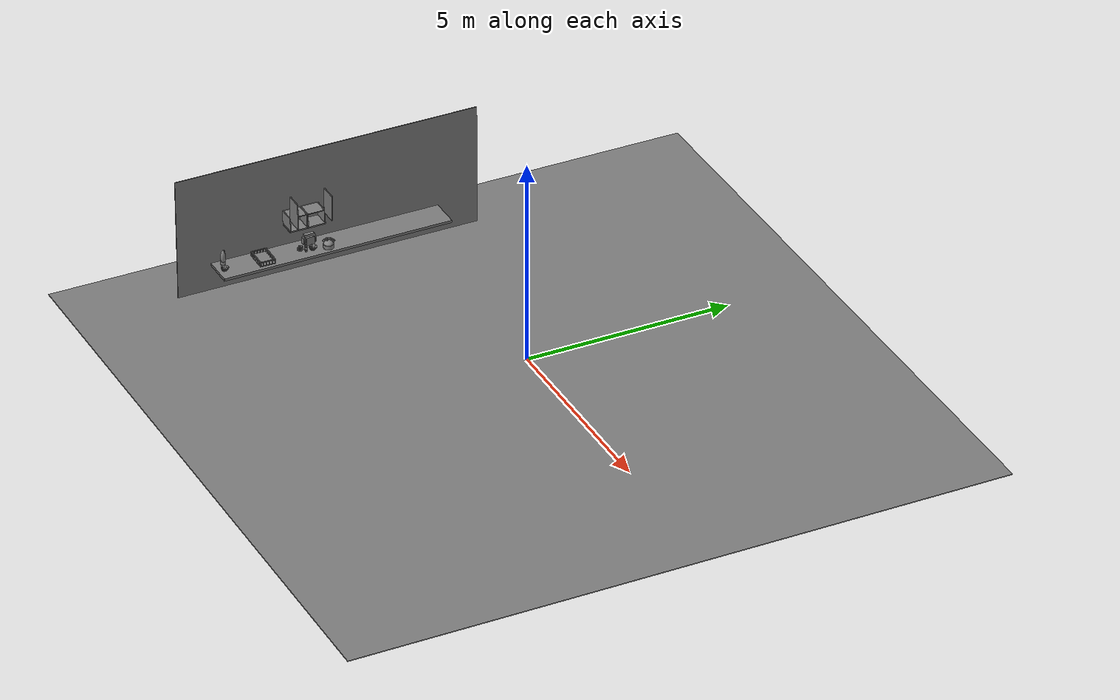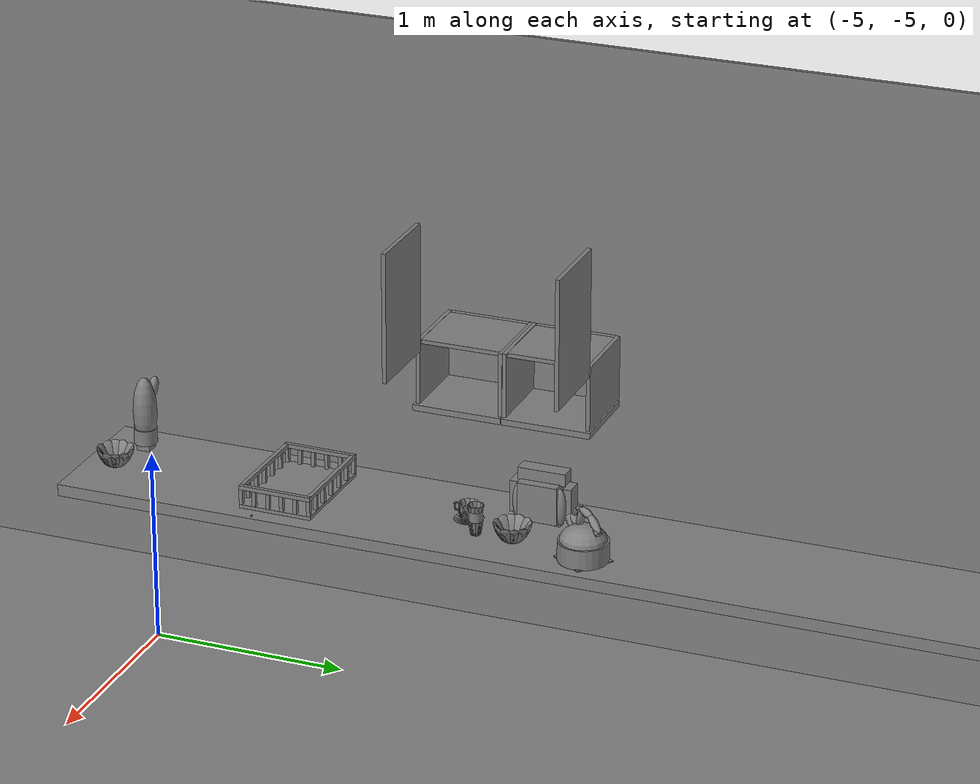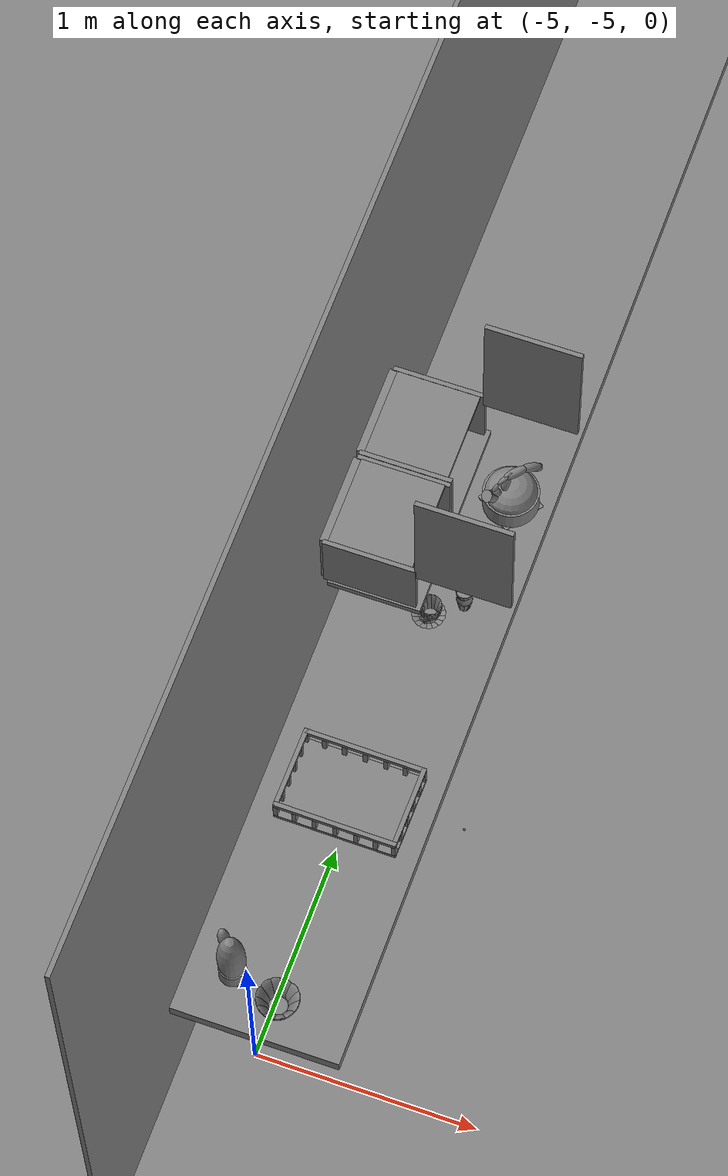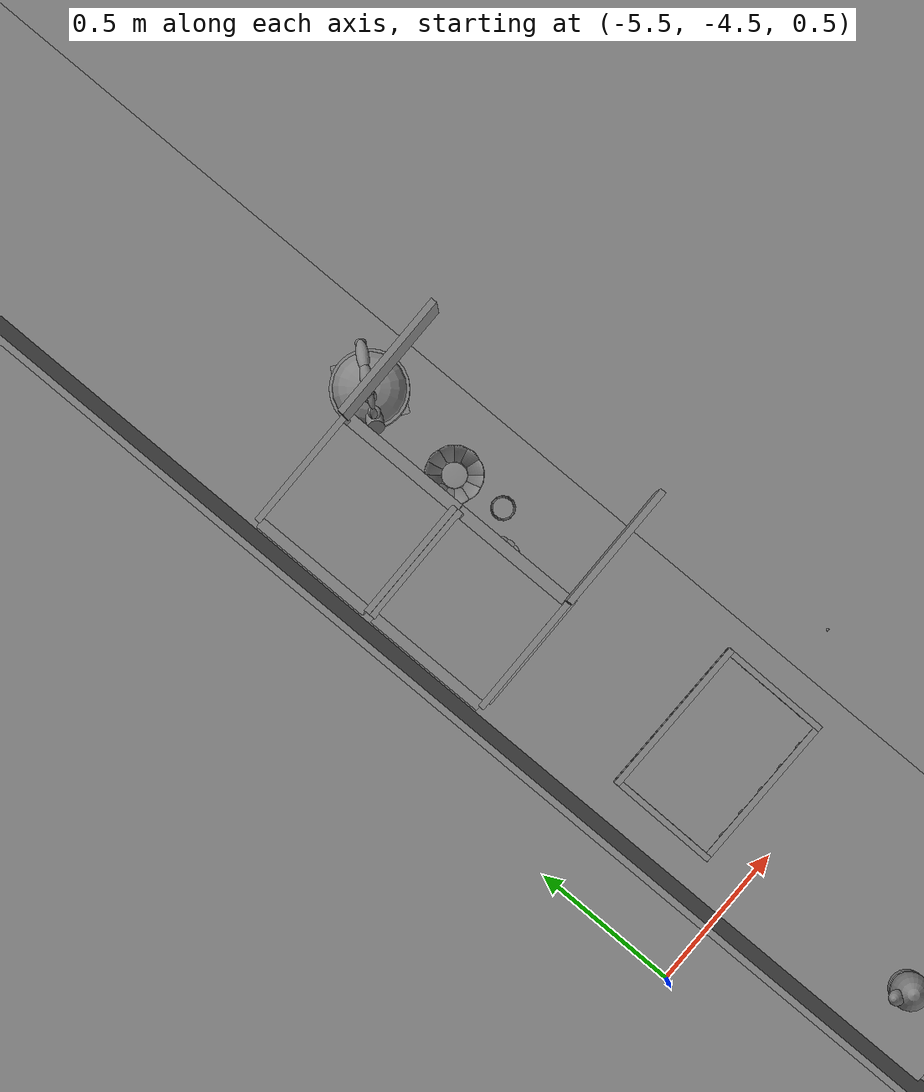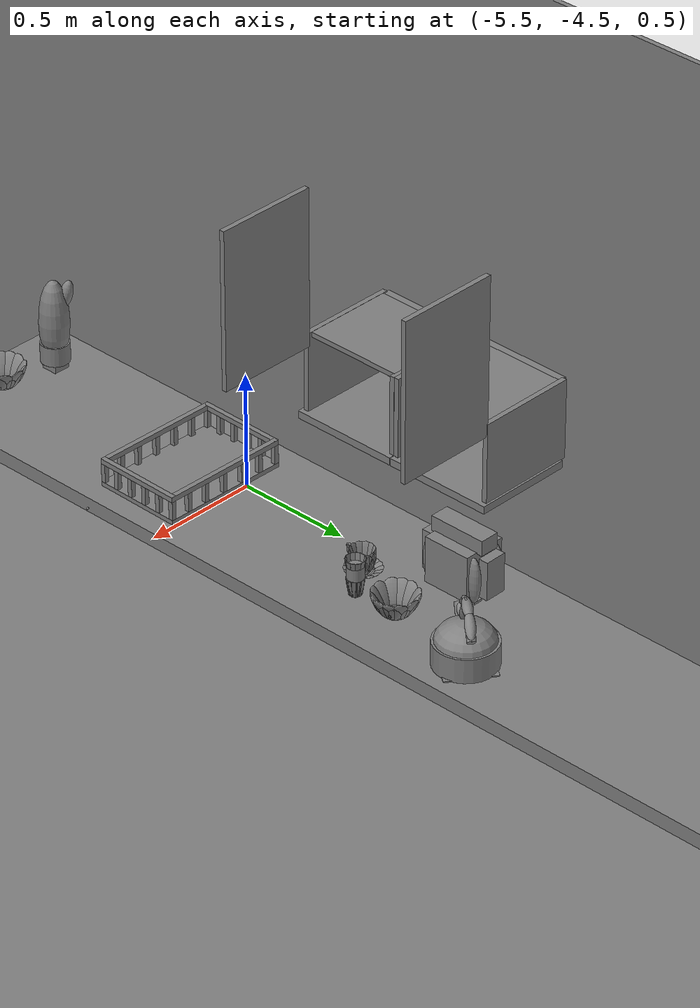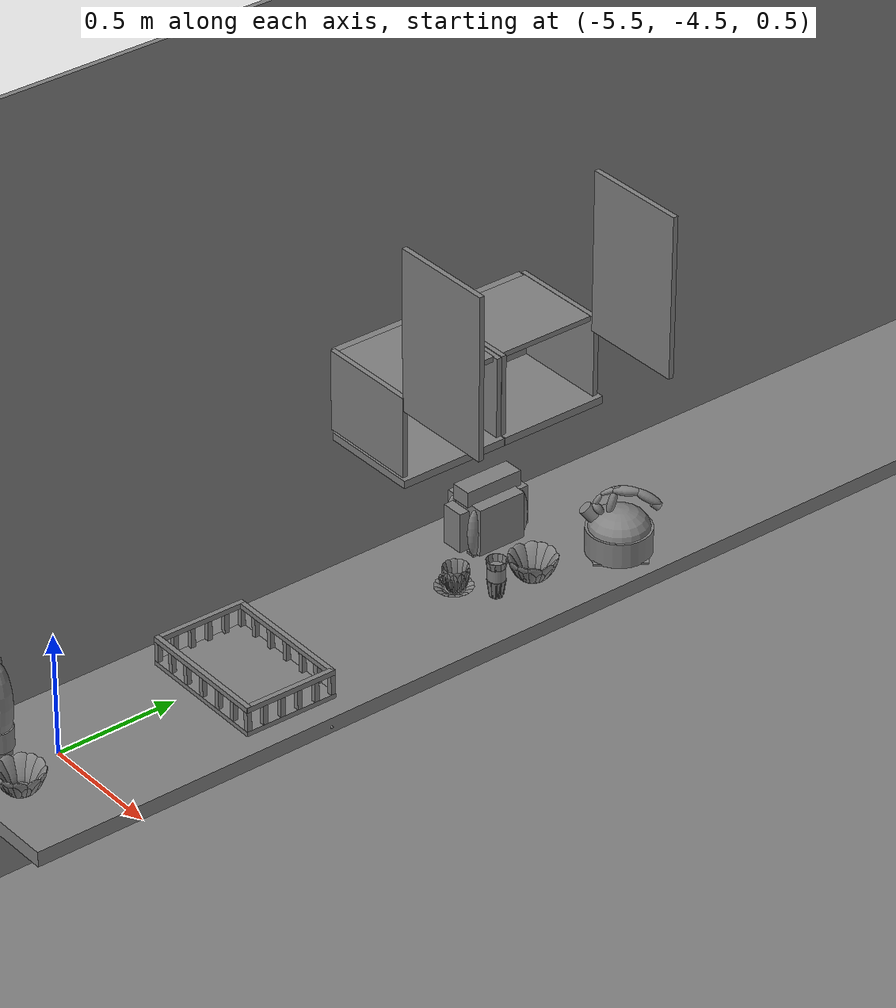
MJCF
<mujoco>
    <option gravity="0.000000000 0.000000000 -9.810000420" timestep="0.0049999999" integrator="implicitfast" density="9.8000002" viscosity="1.8000001e-05" noslip_iterations="10" iterations="100" sdf_iterations="50">
        <flag multiccd="disable"/>
    </option>
    <size memory="1000M"/>
    <compiler coordinate="local"/>
    <worldbody>
        <light cutoff="30" pos="0 1 1" dir="0 -1 -2"/>
        <light cutoff="30" pos="0 -1 1" dir="0 1 -2"/>
        <body pos="-4.860558510 -4.149443150 1.004824519" euler="0.000000000 0.000000000 -90.691108704" name="openloong_gripper_2f85_fix_base_usda_Basket_Kitchen_01">
            <geom contype="1" conaffinity="1" density="1000" type="box" material="" rgba="0.500000000 0.500000000 0.500000000 1.000000000" solimp="0.899999976 0.949999988 0.001000000" friction="1.000000000 0.005000000 0.000100000" solref="0.020000000 1.000000000" margin="0" condim="3" group="0" pos="-0.175679564 -0.000001431 0.109079957" quat="0.707107008 0.000000000 0.000000000 0.707106411" size="0.268999994 0.010000000 0.010500000" name="openloong_gripper_2f85_fix_base_usda_geom_F4F01E2F_84D1_4C1B_BF20_CE1596E8DFFA"/>
            <geom contype="1" conaffinity="1" density="1000" type="box" material="" rgba="0.500000000 0.500000000 0.500000000 1.000000000" solimp="0.899999976 0.949999988 0.001000000" friction="1.000000000 0.005000000 0.000100000" solref="0.020000000 1.000000000" margin="0" condim="3" group="0" pos="-0.176020086 0.002992153 0.059861541" quat="0.707107008 0.000000000 0.000000000 0.707106411" size="0.009500000 0.009500000 0.039999999" name="openloong_gripper_2f85_fix_base_usda_geom_9B365156_A2DA_41A5_B99A_001DD75D6681"/>
            <geom contype="1" conaffinity="1" density="1000" type="box" material="" rgba="0.500000000 0.500000000 0.500000000 1.000000000" solimp="0.899999976 0.949999988 0.001000000" friction="1.000000000 0.005000000 0.000100000" solref="0.020000000 1.000000000" margin="0" condim="3" group="0" pos="0.176000595 0.002991199 0.059860706" quat="0.707107008 0.000000000 0.000000000 0.707106411" size="0.009500000 0.009500000 0.039999999" name="openloong_gripper_2f85_fix_base_usda_geom_82972D9E_70EC_425D_BBCC_C6EA35A74000"/>
            <geom contype="1" conaffinity="1" density="1000" type="box" material="" rgba="0.500000000 0.500000000 0.500000000 1.000000000" solimp="0.899999976 0.949999988 0.001000000" friction="1.000000000 0.005000000 0.000100000" solref="0.020000000 1.000000000" margin="0" condim="3" group="0" pos="0.176003456 0.259475708 0.059860110" quat="0.707107008 0.000000000 0.000000000 0.707106411" size="0.009500000 0.009500000 0.039999999" name="openloong_gripper_2f85_fix_base_usda_geom_F7785011_7D69_4431_91D6_D9FA043F83F4"/>
            <geom contype="1" conaffinity="1" density="1000" type="box" material="" rgba="0.500000000 0.500000000 0.500000000 1.000000000" solimp="0.899999976 0.949999988 0.001000000" friction="1.000000000 0.005000000 0.000100000" solref="0.020000000 1.000000000" margin="0" condim="3" group="0" pos="-0.176020026 -0.088695526 0.059861422" quat="0.707107008 0.000000000 0.000000000 0.707106411" size="0.009500000 0.009500000 0.039999999" name="openloong_gripper_2f85_fix_base_usda_geom_CA41360A_F2A0_4721_ABBB_C8580083892F"/>
            <geom contype="1" conaffinity="1" density="1000" type="box" material="" rgba="0.500000000 0.500000000 0.500000000 1.000000000" solimp="0.899999976 0.949999988 0.001000000" friction="1.000000000 0.005000000 0.000100000" solref="0.020000000 1.000000000" margin="0" condim="3" group="0" pos="0.000000119 0.259647846 0.109080195" quat="0.707107008 0.000000000 0.000000000 0.707106411" size="0.010000000 0.185000002 0.010500000" name="openloong_gripper_2f85_fix_base_usda_geom_3F878A5A_397D_47E9_AE4E_9DECC59F67B3"/>
            <geom contype="1" conaffinity="1" density="1000" type="box" material="" rgba="0.500000000 0.500000000 0.500000000 1.000000000" solimp="0.899999976 0.949999988 0.001000000" friction="1.000000000 0.005000000 0.000100000" solref="0.020000000 1.000000000" margin="0" condim="3" group="0" pos="0.176002026 -0.259545326 0.059860349" quat="0.707107008 0.000000000 0.000000000 0.707106411" size="0.009500000 0.009500000 0.039999999" name="openloong_gripper_2f85_fix_base_usda_geom_AF1D8119_BD9A_4661_9D79_AE533BAC3890"/>
            <geom contype="1" conaffinity="1" density="1000" type="box" material="" rgba="0.500000000 0.500000000 0.500000000 1.000000000" solimp="0.899999976 0.949999988 0.001000000" friction="1.000000000 0.005000000 0.000100000" solref="0.020000000 1.000000000" margin="0" condim="3" group="0" pos="0.036305428 -0.259545326 0.059860706" quat="0.707107008 0.000000000 0.000000000 0.707106411" size="0.009500000 0.009500000 0.039999999" name="openloong_gripper_2f85_fix_base_usda_geom_39E47FBE_36AE_4731_AB41_7845B8CA7DE2"/>
            <geom contype="1" conaffinity="1" density="1000" type="box" material="" rgba="0.500000000 0.500000000 0.500000000 1.000000000" solimp="0.899999976 0.949999988 0.001000000" friction="1.000000000 0.005000000 0.000100000" solref="0.020000000 1.000000000" margin="0" condim="3" group="0" pos="0.000000000 -0.259647369 0.109080195" quat="0.707107008 0.000000000 0.000000000 0.707106411" size="0.010000000 0.185000002 0.010500000" name="openloong_gripper_2f85_fix_base_usda_geom_46B597D4_D202_43CF_A64D_FA7AA4FFC4BF"/>
            <geom contype="1" conaffinity="1" density="1000" type="box" material="" rgba="0.500000000 0.500000000 0.500000000 1.000000000" solimp="0.899999976 0.949999988 0.001000000" friction="1.000000000 0.005000000 0.000100000" solref="0.020000000 1.000000000" margin="0" condim="3" group="0" pos="-0.034950733 -0.259545803 0.059860826" quat="0.707107008 0.000000000 0.000000000 0.707106411" size="0.009500000 0.009500000 0.039999999" name="openloong_gripper_2f85_fix_base_usda_geom_27B383D3_2BF4_4936_91FE_4ACD8698FD67"/>
            <geom contype="1" conaffinity="1" density="1000" type="box" material="" rgba="0.500000000 0.500000000 0.500000000 1.000000000" solimp="0.899999976 0.949999988 0.001000000" friction="1.000000000 0.005000000 0.000100000" solref="0.020000000 1.000000000" margin="0" condim="3" group="0" pos="0.108178139 0.259475946 0.059860229" quat="0.707107008 0.000000000 0.000000000 0.707106411" size="0.009500000 0.009500000 0.039999999" name="openloong_gripper_2f85_fix_base_usda_geom_CB5C32E7_2E0D_4ADC_A463_B2118C1B71B2"/>
            <geom contype="1" conaffinity="1" density="1000" type="box" material="" rgba="0.500000000 0.500000000 0.500000000 1.000000000" solimp="0.899999976 0.949999988 0.001000000" friction="1.000000000 0.005000000 0.000100000" solref="0.020000000 1.000000000" margin="0" condim="3" group="0" pos="-0.106845737 0.259475231 0.059860826" quat="0.707107008 0.000000000 0.000000000 0.707106411" size="0.009500000 0.009500000 0.039999999" name="openloong_gripper_2f85_fix_base_usda_geom_E7EE58DB_8D99_4494_AC42_9207CF4DAC05"/>
            <geom contype="1" conaffinity="1" density="1000" type="box" material="" rgba="0.500000000 0.500000000 0.500000000 1.000000000" solimp="0.899999976 0.949999988 0.001000000" friction="1.000000000 0.005000000 0.000100000" solref="0.020000000 1.000000000" margin="0" condim="3" group="0" pos="-0.176020563 0.179506302 0.059861779" quat="0.707107008 0.000000000 0.000000000 0.707106411" size="0.009500000 0.009500000 0.039999999" name="openloong_gripper_2f85_fix_base_usda_geom_09ABFB7B_2D3D_4D8D_B9B7_C6B4339C3665"/>
            <geom contype="1" conaffinity="1" density="1000" type="box" material="" rgba="0.500000000 0.500000000 0.500000000 1.000000000" solimp="0.899999976 0.949999988 0.001000000" friction="1.000000000 0.005000000 0.000100000" solref="0.020000000 1.000000000" margin="0" condim="3" group="0" pos="-0.034949183 0.259475946 0.059860587" quat="0.707107008 0.000000000 0.000000000 0.707106411" size="0.009500000 0.009500000 0.039999999" name="openloong_gripper_2f85_fix_base_usda_geom_D06C2B6D_E8F7_4F4F_8E09_97CB6AE85722"/>
            <geom contype="1" conaffinity="1" density="1000" type="box" material="" rgba="0.500000000 0.500000000 0.500000000 1.000000000" solimp="0.899999976 0.949999988 0.001000000" friction="1.000000000 0.005000000 0.000100000" solref="0.020000000 1.000000000" margin="0" condim="3" group="0" pos="0.175792217 -0.000001907 0.109079838" quat="0.707107008 0.000000000 0.000000000 0.707106411" size="0.268999994 0.010000000 0.010500000" name="openloong_gripper_2f85_fix_base_usda_geom_8E6ADEFF_9DD1_42C6_8A8A_3E0022D38DE1"/>
            <geom contype="1" conaffinity="1" density="1000" type="box" material="" rgba="0.500000000 0.500000000 0.500000000 1.000000000" solimp="0.899999976 0.949999988 0.001000000" friction="1.000000000 0.005000000 0.000100000" solref="0.020000000 1.000000000" margin="0" condim="3" group="0" pos="-0.000015259 0.000000000 0.010668159" quat="0.707107008 0.000000000 0.000000000 0.707106411" size="0.268999994 0.186000004 0.010500000" name="openloong_gripper_2f85_fix_base_usda_geom_EBE6A359_B2DC_419D_B15D_4EF0BAA5E1A9"/>
            <geom contype="1" conaffinity="1" density="1000" type="box" material="" rgba="0.500000000 0.500000000 0.500000000 1.000000000" solimp="0.899999976 0.949999988 0.001000000" friction="1.000000000 0.005000000 0.000100000" solref="0.020000000 1.000000000" margin="0" condim="3" group="0" pos="-0.176020086 0.094225407 0.059861660" quat="0.707107008 0.000000000 0.000000000 0.707106411" size="0.009500000 0.009500000 0.039999999" name="openloong_gripper_2f85_fix_base_usda_geom_DB7968D5_14D2_4D80_AEF5_FF5878BE108E"/>
            <geom contype="1" conaffinity="1" density="1000" type="box" material="" rgba="0.500000000 0.500000000 0.500000000 1.000000000" solimp="0.899999976 0.949999988 0.001000000" friction="1.000000000 0.005000000 0.000100000" solref="0.020000000 1.000000000" margin="0" condim="3" group="0" pos="0.108177185 -0.259544849 0.059860468" quat="0.707107008 0.000000000 0.000000000 0.707106411" size="0.009500000 0.009500000 0.039999999" name="openloong_gripper_2f85_fix_base_usda_geom_B26FD240_F6A5_4D1B_B835_AEAB35E8B90E"/>
            <geom contype="1" conaffinity="1" density="1000" type="box" material="" rgba="0.500000000 0.500000000 0.500000000 1.000000000" solimp="0.899999976 0.949999988 0.001000000" friction="1.000000000 0.005000000 0.000100000" solref="0.020000000 1.000000000" margin="0" condim="3" group="0" pos="-0.176019967 -0.177031994 0.059861302" quat="0.707107008 0.000000000 0.000000000 0.707106411" size="0.009500000 0.009500000 0.039999999" name="openloong_gripper_2f85_fix_base_usda_geom_ED0D5941_BD61_46C1_A7A3_814D5E9CAD60"/>
            <geom contype="1" conaffinity="1" density="1000" type="box" material="" rgba="0.500000000 0.500000000 0.500000000 1.000000000" solimp="0.899999976 0.949999988 0.001000000" friction="1.000000000 0.005000000 0.000100000" solref="0.020000000 1.000000000" margin="0" condim="3" group="0" pos="-0.176020026 -0.259545326 0.059861183" quat="0.707107008 0.000000000 0.000000000 0.707106411" size="0.009500000 0.009500000 0.039999999" name="openloong_gripper_2f85_fix_base_usda_geom_CEEE8501_11C6_4EE4_91B2_0231EC32B04A"/>
            <geom contype="1" conaffinity="1" density="1000" type="box" material="" rgba="0.500000000 0.500000000 0.500000000 1.000000000" solimp="0.899999976 0.949999988 0.001000000" friction="1.000000000 0.005000000 0.000100000" solref="0.020000000 1.000000000" margin="0" condim="3" group="0" pos="-0.106846333 -0.259546280 0.059861064" quat="0.707107008 0.000000000 0.000000000 0.707106411" size="0.009500000 0.009500000 0.039999999" name="openloong_gripper_2f85_fix_base_usda_geom_C59FBE0B_C28C_437A_84E4_890AA8CF1326"/>
            <geom contype="1" conaffinity="1" density="1000" type="box" material="" rgba="0.500000000 0.500000000 0.500000000 1.000000000" solimp="0.899999976 0.949999988 0.001000000" friction="1.000000000 0.005000000 0.000100000" solref="0.020000000 1.000000000" margin="0" condim="3" group="0" pos="0.176000595 0.094224453 0.059860826" quat="0.707107008 0.000000000 0.000000000 0.707106411" size="0.009500000 0.009500000 0.039999999" name="openloong_gripper_2f85_fix_base_usda_geom_7A060902_0D83_47BC_B726_C419AD77614F"/>
            <geom contype="1" conaffinity="1" density="1000" type="box" material="" rgba="0.500000000 0.500000000 0.500000000 1.000000000" solimp="0.899999976 0.949999988 0.001000000" friction="1.000000000 0.005000000 0.000100000" solref="0.020000000 1.000000000" margin="0" condim="3" group="0" pos="0.176001072 -0.088696480 0.059860587" quat="0.707107008 0.000000000 0.000000000 0.707106411" size="0.009500000 0.009500000 0.039999999" name="openloong_gripper_2f85_fix_base_usda_geom_248EE543_B824_4652_9111_973749E3A3CB"/>
            <geom contype="1" conaffinity="1" density="1000" type="box" material="" rgba="0.500000000 0.500000000 0.500000000 1.000000000" solimp="0.899999976 0.949999988 0.001000000" friction="1.000000000 0.005000000 0.000100000" solref="0.020000000 1.000000000" margin="0" condim="3" group="0" pos="0.036307096 0.259476185 0.059860468" quat="0.707107008 0.000000000 0.000000000 0.707106411" size="0.009500000 0.009500000 0.039999999" name="openloong_gripper_2f85_fix_base_usda_geom_6FD11B3D_27B1_41AB_B78F_505B0D589DDE"/>
            <geom contype="1" conaffinity="1" density="1000" type="box" material="" rgba="0.500000000 0.500000000 0.500000000 1.000000000" solimp="0.899999976 0.949999988 0.001000000" friction="1.000000000 0.005000000 0.000100000" solref="0.020000000 1.000000000" margin="0" condim="3" group="0" pos="0.176001549 -0.177031994 0.059860468" quat="0.707107008 0.000000000 0.000000000 0.707106411" size="0.009500000 0.009500000 0.039999999" name="openloong_gripper_2f85_fix_base_usda_geom_0F89EEE8_5881_406F_B2C3_0B5C414368BC"/>
            <geom contype="1" conaffinity="1" density="1000" type="box" material="" rgba="0.500000000 0.500000000 0.500000000 1.000000000" solimp="0.899999976 0.949999988 0.001000000" friction="1.000000000 0.005000000 0.000100000" solref="0.020000000 1.000000000" margin="0" condim="3" group="0" pos="0.176000118 0.179505348 0.059860945" quat="0.707107008 0.000000000 0.000000000 0.707106411" size="0.009500000 0.009500000 0.039999999" name="openloong_gripper_2f85_fix_base_usda_geom_4629A2A2_489E_472D_B2BF_65556AAC52B6"/>
            <geom contype="1" conaffinity="1" density="1000" type="box" material="" rgba="0.500000000 0.500000000 0.500000000 1.000000000" solimp="0.899999976 0.949999988 0.001000000" friction="1.000000000 0.005000000 0.000100000" solref="0.020000000 1.000000000" margin="0" condim="3" group="0" pos="-0.176020086 0.259474993 0.059860945" quat="0.707107008 0.000000000 0.000000000 0.707106411" size="0.009500000 0.009500000 0.039999999" name="openloong_gripper_2f85_fix_base_usda_geom_6D765DFF_B5BB_4213_86C2_F249314678DC"/>
            <freejoint name="openloong_gripper_2f85_fix_base_usda_Basket_Kitchen_01_joint"/>
        </body>
        <body pos="-4.802892208 -3.488179445 1.876015186" euler="89.999992371 -89.999946594 0.000000000" name="Interactive Objcets_guimen_01">
            <geom contype="1" conaffinity="1" density="1000" type="box" material="" rgba="0.500000000 0.500000000 0.500000000 1.000000000" solimp="0.899999976 0.949999988 0.001000000" friction="1.000000000 0.005000000 0.000100000" solref="0.020000000 1.000000000" margin="0" condim="3" group="0" pos="0.006727934 0.314709902 -0.203009605" quat="1.000000000 0.000000119 -0.000000119 0.000000000" size="0.010000000 0.317999989 0.204999998" name="Interactive Objcets_geom_32A371E5_2B87_463D_A657_40524FD7C18C"/>
            <joint armature="0" stiffness="0" damping="1" axis="0.000000 1.000000 0.000000" type="hinge" name="Interactive Objcets_guimen_01"/>
        </body>
        <body pos="-4.805274963 -2.665403366 1.876015186" euler="89.999877930 89.999969482 0.000000000" name="Interactive Objcets_guimen_02">
            <geom contype="1" conaffinity="1" density="1000" type="box" material="" rgba="0.500000000 0.500000000 0.500000000 1.000000000" solimp="0.899999976 0.949999988 0.001000000" friction="1.000000000 0.005000000 0.000100000" solref="0.020000000 1.000000000" margin="0" condim="3" group="0" pos="0.006727815 0.314709663 0.203009367" quat="0.999999940 0.000000000 0.000000000 0.000000000" size="0.010000000 0.317999989 0.204999998" name="Interactive Objcets_geom_4735120C_F123_4701_9FA5_A380C1C2FC18"/>
            <joint armature="0" stiffness="0" damping="1" axis="0.000000 1.000000 0.000000" type="hinge" name="Interactive Objcets_guimen_02"/>
        </body>
        <body pos="-4.827295780 -3.287638187 1.074643731" euler="0.000000000 0.000000000 89.999992371" name="Interactive Objcets_coffeecup_01">
            <geom contype="1" conaffinity="1" density="1000" type="ellipsoid" material="" rgba="0.500000000 0.500000000 0.500000000 1.000000000" solimp="0.899999976 0.949999988 0.001000000" friction="1.000000000 0.005000000 0.000100000" solref="0.020000000 1.000000000" margin="0" condim="3" group="0" pos="0.035336256 0.000558376 -0.043215394" quat="0.999999881 0.000000000 0.000000000 0.000000000" size="0.029999999 0.029999999 0.001000000" name="Interactive Objcets_geom_81F9AEE1_7F67_42B0_A979_A3A397BA694A"/>
            <geom contype="1" conaffinity="1" density="1000" type="ellipsoid" material="" rgba="0.500000000 0.500000000 0.500000000 1.000000000" solimp="0.899999976 0.949999988 0.001000000" friction="1.000000000 0.005000000 0.000100000" solref="0.020000000 1.000000000" margin="0" condim="3" group="0" pos="0.067416430 -0.018191338 0.002976775" quat="0.961934388 0.024418317 0.091648072 -0.256293803" size="0.005000000 0.029999999 0.048999999" name="Interactive Objcets_geom_D2B96789_E886_445B_B572_A2E812C210BB"/>
            <geom contype="1" conaffinity="1" density="1000" type="ellipsoid" material="" rgba="0.500000000 0.500000000 0.500000000 1.000000000" solimp="0.899999976 0.949999988 0.001000000" friction="1.000000000 0.005000000 0.000100000" solref="0.020000000 1.000000000" margin="0" condim="3" group="0" pos="0.034471050 -0.037125111 0.002976775" quat="0.701517045 0.067293778 0.066836871 -0.706313014" size="0.005000000 0.029999999 0.048999999" name="Interactive Objcets_geom_81835165_5F89_4B45_A05F_676D76F563BE"/>
            <geom contype="1" conaffinity="1" density="1000" type="ellipsoid" material="" rgba="0.500000000 0.500000000 0.500000000 1.000000000" solimp="0.899999976 0.949999988 0.001000000" friction="1.000000000 0.005000000 0.000100000" solref="0.020000000 1.000000000" margin="0" condim="3" group="0" pos="0.035336256 0.000558376 -0.045152068" quat="0.999999881 0.000000000 0.000000000 0.000000000" size="0.029999999 0.029999999 0.001000000" name="Interactive Objcets_geom_497518D0_BC95_46AA_A847_258B2CE5F2F0"/>
            <geom contype="1" conaffinity="1" density="1000" type="ellipsoid" material="" rgba="0.500000000 0.500000000 0.500000000 1.000000000" solimp="0.899999976 0.949999988 0.001000000" friction="1.000000000 0.005000000 0.000100000" solref="0.020000000 1.000000000" margin="0" condim="3" group="0" pos="0.001010895 -0.016271591 0.002976775" quat="0.228377163 0.092315644 0.021758538 -0.968941689" size="0.005000000 0.029999999 0.048999999" name="Interactive Objcets_geom_CA6BFC37_1816_4315_996E_270B0D36235B"/>
            <geom contype="1" conaffinity="1" density="1000" type="capsule" material="" rgba="0.500000000 0.500000000 0.500000000 1.000000000" solimp="0.899999976 0.949999988 0.001000000" friction="1.000000000 0.005000000 0.000100000" solref="0.020000000 1.000000000" margin="0" condim="3" group="0" pos="-0.021276474 0.000000000 0.038509369" quat="0.633189917 0.000000000 0.773996413 0.000000000" size="0.004000000 0.009000000 1.000000000" name="Interactive Objcets_geom_E07BDBDA_FD08_423C_B8C4_AEFC39C790BC"/>
            <geom contype="1" conaffinity="1" density="1000" type="capsule" material="" rgba="0.500000000 0.500000000 0.500000000 1.000000000" solimp="0.899999976 0.949999988 0.001000000" friction="1.000000000 0.005000000 0.000100000" solref="0.020000000 1.000000000" margin="0" condim="3" group="0" pos="-0.018014431 0.000000000 0.001762271" quat="0.707106769 -0.000000004 0.707106709 -0.000000088" size="0.004000000 0.005000000 1.000000000" name="Interactive Objcets_geom_117A8C00_2815_41B2_9845_8B0AF2F23A61"/>
            <geom contype="1" conaffinity="1" density="1000" type="ellipsoid" material="" rgba="0.500000000 0.500000000 0.500000000 1.000000000" solimp="0.899999976 0.949999988 0.001000000" friction="1.000000000 0.005000000 0.000100000" solref="0.020000000 1.000000000" margin="0" condim="3" group="0" pos="0.068445444 0.017385960 0.002976775" quat="0.228377223 -0.092319682 -0.021759447 -0.968941331" size="0.005000000 0.029999999 0.048999999" name="Interactive Objcets_geom_6A561141_6B0A_4887_A63F_F40470A3C7FC"/>
            <geom contype="1" conaffinity="1" density="1000" type="ellipsoid" material="" rgba="0.500000000 0.500000000 0.500000000 1.000000000" solimp="0.899999976 0.949999988 0.001000000" friction="1.000000000 0.005000000 0.000100000" solref="0.020000000 1.000000000" margin="0" condim="3" group="0" pos="0.002039194 0.019308567 0.002976775" quat="0.961933970 -0.024419386 -0.091652036 -0.256293654" size="0.005000000 0.029999999 0.048999999" name="Interactive Objcets_geom_8C52B6D9_6C66_44F7_BD4E_9F1B47A5992A"/>
            <geom contype="1" conaffinity="1" density="1000" type="ellipsoid" material="" rgba="0.500000000 0.500000000 0.500000000 1.000000000" solimp="0.899999976 0.949999988 0.001000000" friction="1.000000000 0.005000000 0.000100000" solref="0.020000000 1.000000000" margin="0" condim="3" group="0" pos="0.034984604 0.038240910 0.002976775" quat="0.701516926 -0.067296736 -0.066839755 -0.706312656" size="0.005000000 0.029999999 0.048999999" name="Interactive Objcets_geom_334CB2D8_67F6_47F6_8529_7490E79EFB4D"/>
            <geom contype="1" conaffinity="1" density="1000" type="ellipsoid" material="" rgba="0.500000000 0.500000000 0.500000000 1.000000000" solimp="0.899999976 0.949999988 0.001000000" friction="1.000000000 0.005000000 0.000100000" solref="0.020000000 1.000000000" margin="0" condim="3" group="0" pos="0.017669693 0.034160614 0.002976775" quat="0.848410904 -0.049618516 -0.080835648 -0.520770907" size="0.005000000 0.029999999 0.048999999" name="Interactive Objcets_geom_6CAEAF8C_0505_4923_A256_BFCE6F366545"/>
            <geom contype="1" conaffinity="1" density="1000" type="ellipsoid" material="" rgba="0.500000000 0.500000000 0.500000000 1.000000000" solimp="0.899999976 0.949999988 0.001000000" friction="1.000000000 0.005000000 0.000100000" solref="0.020000000 1.000000000" margin="0" condim="3" group="0" pos="-0.002956629 0.000558376 0.002976775" quat="0.995491505 0.000000004 -0.094849378 -0.000000089" size="0.005000000 0.029999999 0.048999999" name="Interactive Objcets_geom_B67D251B_EDB9_4B72_901E_CA5E201BA8F7"/>
            <geom contype="1" conaffinity="1" density="1000" type="ellipsoid" material="" rgba="0.500000000 0.500000000 0.500000000 1.000000000" solimp="0.899999976 0.949999988 0.001000000" friction="1.000000000 0.005000000 0.000100000" solref="0.020000000 1.000000000" margin="0" condim="3" group="0" pos="0.051787138 -0.033043861 0.002976775" quat="0.848411202 0.049616337 0.080832161 -0.520771146" size="0.005000000 0.029999999 0.048999999" name="Interactive Objcets_geom_4B334B7D_B29B_4DCC_8C52_52FBEBFC2BE4"/>
            <geom contype="1" conaffinity="1" density="1000" type="capsule" material="" rgba="0.500000000 0.500000000 0.500000000 1.000000000" solimp="0.899999976 0.949999988 0.001000000" friction="1.000000000 0.005000000 0.000100000" solref="0.020000000 1.000000000" margin="0" condim="3" group="0" pos="-0.030251026 0.000000000 0.004966617" quat="0.480583906 -0.000000000 0.876948774 -0.000000126" size="0.004000000 0.005000000 1.000000000" name="Interactive Objcets_geom_3F20821C_7F9A_4F27_AA80_33CF40631EE1"/>
            <geom contype="1" conaffinity="1" density="1000" type="capsule" material="" rgba="0.500000000 0.500000000 0.500000000 1.000000000" solimp="0.899999976 0.949999988 0.001000000" friction="1.000000000 0.005000000 0.000100000" solref="0.020000000 1.000000000" margin="0" condim="3" group="0" pos="-0.036300898 0.000000000 0.021037936" quat="0.044551343 -0.000000000 0.999007046 -0.000000126" size="0.004000000 0.012000000 1.000000000" name="Interactive Objcets_geom_B0EF83FA_66C6_43BE_884F_B827750594BA"/>
            <geom contype="1" conaffinity="1" density="1000" type="capsule" material="" rgba="0.500000000 0.500000000 0.500000000 1.000000000" solimp="0.899999976 0.949999988 0.001000000" friction="1.000000000 0.005000000 0.000100000" solref="0.020000000 1.000000000" margin="0" condim="3" group="0" pos="-0.008219719 0.000000000 -0.000944734" quat="0.364379913 0.000000063 0.931250274 -0.000000063" size="0.004000000 0.003000000 1.000000000" name="Interactive Objcets_geom_DD6A1AAA_1CEF_4BA6_AF54_231C13DBC243"/>
            <geom contype="1" conaffinity="1" density="1000" type="capsule" material="" rgba="0.500000000 0.500000000 0.500000000 1.000000000" solimp="0.899999976 0.949999988 0.001000000" friction="1.000000000 0.005000000 0.000100000" solref="0.020000000 1.000000000" margin="0" condim="3" group="0" pos="-0.033022881 0.000000000 0.037873149" quat="0.874267220 0.000000042 0.485444903 -0.000000084" size="0.004000000 0.004000000 1.000000000" name="Interactive Objcets_geom_31FFAF74_CF60_42B5_B676_14D17DDC0831"/>
            <geom contype="1" conaffinity="1" density="1000" type="ellipsoid" material="" rgba="0.500000000 0.500000000 0.500000000 1.000000000" solimp="0.899999976 0.949999988 0.001000000" friction="1.000000000 0.005000000 0.000100000" solref="0.020000000 1.000000000" margin="0" condim="3" group="0" pos="0.015755907 -0.032001972 0.002976775" quat="0.496025920 0.082232773 0.047258731 -0.863112032" size="0.005000000 0.029999999 0.048999999" name="Interactive Objcets_geom_24B6D10C_D839_4BAC_BFFE_FA83DA2EDF5E"/>
            <geom contype="1" conaffinity="1" density="1000" type="ellipsoid" material="" rgba="0.500000000 0.500000000 0.500000000 1.000000000" solimp="0.899999976 0.949999988 0.001000000" friction="1.000000000 0.005000000 0.000100000" solref="0.020000000 1.000000000" margin="0" condim="3" group="0" pos="0.072411790 0.000558376 0.002976775" quat="0.995491922 -0.000000019 0.094845265 -0.000000089" size="0.005000000 0.029999999 0.048999999" name="Interactive Objcets_geom_75770343_E8D7_4CF1_92D2_8697F73F542A"/>
            <geom contype="1" conaffinity="1" density="1000" type="ellipsoid" material="" rgba="0.500000000 0.500000000 0.500000000 1.000000000" solimp="0.899999976 0.949999988 0.001000000" friction="1.000000000 0.005000000 0.000100000" solref="0.020000000 1.000000000" margin="0" condim="3" group="0" pos="0.053700209 0.033117294 0.002976775" quat="0.496025741 -0.082236379 -0.047260769 -0.863111615" size="0.005000000 0.029999999 0.048999999" name="Interactive Objcets_geom_FB41899D_8582_4EB7_A86B_7E4993FB4FD8"/>
            <freejoint name="Interactive Objcets_coffeecup_01"/>
        </body>
        <body pos="-5.020127296 -2.953741550 1.135127425" euler="89.999946594 0.000000000 0.000000000" name="Interactive Objcets_Bread">
            <geom contype="1" conaffinity="1" density="1000" type="box" material="" rgba="0.500000000 0.500000000 0.500000000 1.000000000" solimp="0.899999976 0.949999988 0.001000000" friction="1.000000000 0.005000000 0.000100000" solref="0.020000000 1.000000000" margin="0" condim="3" group="0" pos="-0.008702755 -0.017670274 -0.135069147" quat="0.707107067 -0.707106471 0.000000021 -0.000000021" size="0.045000002 0.020000000 0.079999998" name="Interactive Objcets_geom_C0D4B59B_BA96_4465_8EEE_429CCD241258"/>
            <geom contype="1" conaffinity="1" density="1000" type="box" material="" rgba="0.500000000 0.500000000 0.500000000 1.000000000" solimp="0.899999976 0.949999988 0.001000000" friction="1.000000000 0.005000000 0.000100000" solref="0.020000000 1.000000000" margin="0" condim="3" group="0" pos="0.033925056 -0.123201847 0.086778767" quat="0.707107067 -0.707106471 0.000000021 -0.000000021" size="0.020000000 0.020000000 0.005000000" name="Interactive Objcets_geom_92C53D1A_C95B_4039_9E4B_5170BE9FD52F"/>
            <geom contype="1" conaffinity="1" density="1000" type="box" material="" rgba="0.500000000 0.500000000 0.500000000 1.000000000" solimp="0.899999976 0.949999988 0.001000000" friction="1.000000000 0.005000000 0.000100000" solref="0.020000000 1.000000000" margin="0" condim="3" group="0" pos="-0.008702755 -0.016588926 0.000174277" quat="0.707107067 -0.707106471 0.000000021 -0.000000021" size="0.090000004 0.100000001 0.094999999" name="Interactive Objcets_geom_930CD07F_05A1_4D9C_8F61_BD6D152A9BE0"/>
            <geom contype="1" conaffinity="1" density="1000" type="ellipsoid" material="" rgba="0.500000000 0.500000000 0.500000000 1.000000000" solimp="0.899999976 0.949999988 0.001000000" friction="1.000000000 0.005000000 0.000100000" solref="0.020000000 1.000000000" margin="0" condim="3" group="0" pos="-0.067312241 -0.026057482 -0.101716787" quat="0.707107067 -0.707106471 0.000000021 -0.000000021" size="0.020000000 0.029999999 0.094999999" name="Interactive Objcets_geom_3F73AACE_121F_439F_840A_6176D8241582"/>
            <geom contype="1" conaffinity="1" density="1000" type="ellipsoid" material="" rgba="0.500000000 0.500000000 0.500000000 1.000000000" solimp="0.899999976 0.949999988 0.001000000" friction="1.000000000 0.005000000 0.000100000" solref="0.020000000 1.000000000" margin="0" condim="3" group="0" pos="0.052222252 -0.026057363 0.101459242" quat="0.707107067 -0.707106471 0.000000021 -0.000000021" size="0.020000000 0.029999999 0.094999999" name="Interactive Objcets_geom_09EDF30E_B1A1_4A98_8172_E01FA153F814"/>
            <geom contype="1" conaffinity="1" density="1000" type="box" material="" rgba="0.500000000 0.500000000 0.500000000 1.000000000" solimp="0.899999976 0.949999988 0.001000000" friction="1.000000000 0.005000000 0.000100000" solref="0.020000000 1.000000000" margin="0" condim="3" group="0" pos="-0.050020695 -0.123201847 0.086778767" quat="0.707107067 -0.707106471 0.000000021 -0.000000021" size="0.020000000 0.020000000 0.005000000" name="Interactive Objcets_geom_3DF3E9E4_2885_4E12_B6A9_7BA941F1D971"/>
            <geom contype="1" conaffinity="1" density="1000" type="box" material="" rgba="0.500000000 0.500000000 0.500000000 1.000000000" solimp="0.899999976 0.949999988 0.001000000" friction="1.000000000 0.005000000 0.000100000" solref="0.020000000 1.000000000" margin="0" condim="3" group="0" pos="0.033925056 -0.123201728 -0.092369899" quat="0.707107067 -0.707106471 0.000000021 -0.000000021" size="0.020000000 0.020000000 0.005000000" name="Interactive Objcets_geom_36B56C2C_51F3_4564_9328_962047037A5F"/>
            <geom contype="1" conaffinity="1" density="1000" type="ellipsoid" material="" rgba="0.500000000 0.500000000 0.500000000 1.000000000" solimp="0.899999976 0.949999988 0.001000000" friction="1.000000000 0.005000000 0.000100000" solref="0.020000000 1.000000000" margin="0" condim="3" group="0" pos="-0.069190502 -0.026057363 0.101458766" quat="0.707107067 -0.707106471 0.000000021 -0.000000021" size="0.020000000 0.029999999 0.094999999" name="Interactive Objcets_geom_FEC7E487_BFD4_4E4E_A6A4_AD1C96C3DB72"/>
            <geom contype="1" conaffinity="1" density="1000" type="box" material="" rgba="0.500000000 0.500000000 0.500000000 1.000000000" solimp="0.899999976 0.949999988 0.001000000" friction="1.000000000 0.005000000 0.000100000" solref="0.020000000 1.000000000" margin="0" condim="3" group="0" pos="-0.008702755 -0.017670155 0.134585604" quat="0.707107067 -0.707106471 0.000000021 -0.000000021" size="0.045000002 0.020000000 0.079999998" name="Interactive Objcets_geom_C68EFC2A_DE10_4214_A82B_517E528180A5"/>
            <geom contype="1" conaffinity="1" density="1000" type="box" material="" rgba="0.500000000 0.500000000 0.500000000 1.000000000" solimp="0.899999976 0.949999988 0.001000000" friction="1.000000000 0.005000000 0.000100000" solref="0.020000000 1.000000000" margin="0" condim="3" group="0" pos="-0.050020695 -0.123201728 -0.092370376" quat="0.707107067 -0.707106471 0.000000021 -0.000000021" size="0.020000000 0.020000000 0.005000000" name="Interactive Objcets_geom_82B7A20B_2160_4855_B73A_28368B989C17"/>
            <geom contype="1" conaffinity="1" density="1000" type="box" material="" rgba="0.500000000 0.500000000 0.500000000 1.000000000" solimp="0.899999976 0.949999988 0.001000000" friction="1.000000000 0.005000000 0.000100000" solref="0.020000000 1.000000000" margin="0" condim="3" group="0" pos="-0.008702755 0.104617000 -0.003706597" quat="0.707107067 -0.707106471 0.000000021 -0.000000021" size="0.039999999 0.119999997 0.030999999" name="Interactive Objcets_geom_490F5395_3A45_4EBE_990A_BB157CB0F0F3"/>
            <geom contype="1" conaffinity="1" density="1000" type="ellipsoid" material="" rgba="0.500000000 0.500000000 0.500000000 1.000000000" solimp="0.899999976 0.949999988 0.001000000" friction="1.000000000 0.005000000 0.000100000" solref="0.020000000 1.000000000" margin="0" condim="3" group="0" pos="0.052222252 -0.026057243 -0.106481344" quat="0.707107067 -0.707106471 0.000000021 -0.000000021" size="0.020000000 0.029999999 0.094999999" name="Interactive Objcets_geom_2197EEDB_6481_491C_BF09_59C3F598FAC6"/>
            <freejoint name="Interactive Objcets_Bread"/>
        </body>
        <body pos="-4.821335316 -5.105734825 1.007418752" euler="0.000000000 0.000000000 89.999946594" name="Interactive Objcets_bow_04">
            <geom contype="1" conaffinity="1" density="1000" type="ellipsoid" material="" rgba="0.500000000 0.500000000 0.500000000 1.000000000" solimp="0.899999976 0.949999988 0.001000000" friction="1.000000000 0.005000000 0.000100000" solref="0.020000000 1.000000000" margin="0" condim="3" group="0" pos="0.052321672 -0.040297985 0.044118762" quat="0.919264674 0.076882720 0.225593746 -0.313287675" size="0.010000000 0.039999999 0.052000001" name="Interactive Objcets_geom_5DDA95BD_47D9_4CD5_842A_9C79675BE898"/>
            <geom contype="1" conaffinity="1" density="1000" type="ellipsoid" material="" rgba="0.500000000 0.500000000 0.500000000 1.000000000" solimp="0.899999976 0.949999988 0.001000000" friction="1.000000000 0.005000000 0.000100000" solref="0.020000000 1.000000000" margin="0" condim="3" group="0" pos="0.059080124 0.029511929 0.044118762" quat="0.223252952 -0.231952190 -0.054787360 -0.945174456" size="0.010000000 0.039999999 0.052000001" name="Interactive Objcets_geom_24392F96_7745_47F4_AF45_C867E2EF7A1D"/>
            <geom contype="1" conaffinity="1" density="1000" type="ellipsoid" material="" rgba="0.500000000 0.500000000 0.500000000 1.000000000" solimp="0.899999976 0.949999988 0.001000000" friction="1.000000000 0.005000000 0.000100000" solref="0.020000000 1.000000000" margin="0" condim="3" group="0" pos="0.000082970 0.000000000 0.003118873" quat="1.000000000 0.000000000 0.000000000 0.000000000" size="0.039999999 0.039999999 0.002000000" name="Interactive Objcets_geom_E88A36FE_58E8_467B_8DB6_5C733E7DA663"/>
            <geom contype="1" conaffinity="1" density="1000" type="ellipsoid" material="" rgba="0.500000000 0.500000000 0.500000000 1.000000000" solimp="0.899999976 0.949999988 0.001000000" friction="1.000000000 0.005000000 0.000100000" solref="0.020000000 1.000000000" margin="0" condim="3" group="0" pos="-0.040080309 -0.052354813 0.044118762" quat="0.429593146 0.213749856 0.105425127 -0.871003032" size="0.010000000 0.039999999 0.052000001" name="Interactive Objcets_geom_51762603_CFEF_445B_968D_56A41925D900"/>
            <geom contype="1" conaffinity="1" density="1000" type="ellipsoid" material="" rgba="0.500000000 0.500000000 0.500000000 1.000000000" solimp="0.899999976 0.949999988 0.001000000" friction="1.000000000 0.005000000 0.000100000" solref="0.020000000 1.000000000" margin="0" condim="3" group="0" pos="0.000243664 -0.065983295 0.044118762" quat="0.687598884 0.168314576 0.168741226 -0.685860336" size="0.010000000 0.039999999 0.052000001" name="Interactive Objcets_geom_9BB2CC0D_26B1_4B8F_928C_1B364CFBB0D6"/>
            <geom contype="1" conaffinity="1" density="1000" type="ellipsoid" material="" rgba="0.500000000 0.500000000 0.500000000 1.000000000" solimp="0.899999976 0.949999988 0.001000000" friction="1.000000000 0.005000000 0.000100000" solref="0.020000000 1.000000000" margin="0" condim="3" group="0" pos="-0.065898657 -0.000007629 0.044118762" quat="0.971183062 -0.000000142 -0.238334835 0.000000030" size="0.010000000 0.039999999 0.052000001" name="Interactive Objcets_geom_80FCF4EE_90D9_4511_8644_1D6668A5165E"/>
            <geom contype="1" conaffinity="1" density="1000" type="ellipsoid" material="" rgba="0.500000000 0.500000000 0.500000000 1.000000000" solimp="0.899999976 0.949999988 0.001000000" friction="1.000000000 0.005000000 0.000100000" solref="0.020000000 1.000000000" margin="0" condim="3" group="0" pos="-0.052167892 0.040281773 0.044118762" quat="0.919264615 -0.076883025 -0.225593626 -0.313287735" size="0.010000000 0.039999999 0.052000001" name="Interactive Objcets_geom_58417FE9_69BE_4061_B93E_7E90F2215051"/>
            <geom contype="1" conaffinity="1" density="1000" type="ellipsoid" material="" rgba="0.500000000 0.500000000 0.500000000 1.000000000" solimp="0.899999976 0.949999988 0.001000000" friction="1.000000000 0.005000000 0.000100000" solref="0.020000000 1.000000000" margin="0" condim="3" group="0" pos="-0.029293537 0.059069157 0.044118762" quat="0.825556040 -0.125530839 -0.202596709 -0.511521041" size="0.010000000 0.039999999 0.052000001" name="Interactive Objcets_geom_310187A4_8367_471C_A1A7_D9D584AC0FA2"/>
            <geom contype="1" conaffinity="1" density="1000" type="ellipsoid" material="" rgba="0.500000000 0.500000000 0.500000000 1.000000000" solimp="0.899999976 0.949999988 0.001000000" friction="1.000000000 0.005000000 0.000100000" solref="0.020000000 1.000000000" margin="0" condim="3" group="0" pos="0.000082970 0.000000000 0.000446677" quat="1.000000000 0.000000000 0.000000000 0.000000000" size="0.039999999 0.039999999 0.002000000" name="Interactive Objcets_geom_8E3DFA85_5E45_4A20_A2A1_72E2B6AF2604"/>
            <geom contype="1" conaffinity="1" density="1000" type="ellipsoid" material="" rgba="0.500000000 0.500000000 0.500000000 1.000000000" solimp="0.899999976 0.949999988 0.001000000" friction="1.000000000 0.005000000 0.000100000" solref="0.020000000 1.000000000" margin="0" condim="3" group="0" pos="0.029448032 -0.059085369 0.044118762" quat="0.825555801 0.125530601 0.202597082 -0.511521280" size="0.010000000 0.039999999 0.052000001" name="Interactive Objcets_geom_9E7CF9A8_8DA9_46D3_94B5_472D4CB43E4A"/>
            <geom contype="1" conaffinity="1" density="1000" type="ellipsoid" material="" rgba="0.500000000 0.500000000 0.500000000 1.000000000" solimp="0.899999976 0.949999988 0.001000000" friction="1.000000000 0.005000000 0.000100000" solref="0.020000000 1.000000000" margin="0" condim="3" group="0" pos="0.066051960 -0.000007629 0.044118762" quat="0.971183062 -0.000000156 0.238334835 0.000000030" size="0.010000000 0.039999999 0.052000001" name="Interactive Objcets_geom_0CC48742_0256_4B11_BC28_50C2368BDC46"/>
            <geom contype="1" conaffinity="1" density="1000" type="ellipsoid" material="" rgba="0.500000000 0.500000000 0.500000000 1.000000000" solimp="0.899999976 0.949999988 0.001000000" friction="1.000000000 0.005000000 0.000100000" solref="0.020000000 1.000000000" margin="0" condim="3" group="0" pos="-0.058925867 -0.029528618 0.044118762" quat="0.223252863 0.231952116 0.054787725 -0.945174456" size="0.010000000 0.039999999 0.052000001" name="Interactive Objcets_geom_11250196_58E6_420A_A881_C95A848D29A1"/>
            <geom contype="1" conaffinity="1" density="1000" type="ellipsoid" material="" rgba="0.500000000 0.500000000 0.500000000 1.000000000" solimp="0.899999976 0.949999988 0.001000000" friction="1.000000000 0.005000000 0.000100000" solref="0.020000000 1.000000000" margin="0" condim="3" group="0" pos="0.040234327 0.052339077 0.044118762" quat="0.429593533 -0.213750005 -0.105424747 -0.871002972" size="0.010000000 0.039999999 0.052000001" name="Interactive Objcets_geom_E1BFCF02_25AA_414E_A694_375C8F34CA81"/>
            <geom contype="1" conaffinity="1" density="1000" type="ellipsoid" material="" rgba="0.500000000 0.500000000 0.500000000 1.000000000" solimp="0.899999976 0.949999988 0.001000000" friction="1.000000000 0.005000000 0.000100000" solref="0.020000000 1.000000000" margin="0" condim="3" group="0" pos="-0.000090122 0.065967083 0.044118762" quat="0.687598825 -0.168314755 -0.168741047 -0.685860395" size="0.010000000 0.039999999 0.052000001" name="Interactive Objcets_geom_8AA268A9_8836_4381_BA74_57D73B2A5B1F"/>
            <freejoint name="Interactive Objcets_bow_04"/>
        </body>
        <body pos="-4.685121059 -2.618872881 1.139834642" euler="-89.999885559 -75.046211243 -179.999633789" name="Interactive Objcets_shuihu">
            <geom contype="1" conaffinity="1" density="1000" type="ellipsoid" material="" rgba="0.500000000 0.500000000 0.500000000 1.000000000" solimp="0.899999976 0.949999988 0.001000000" friction="1.000000000 0.005000000 0.000100000" solref="0.020000000 1.000000000" margin="0" condim="3" group="0" pos="0.076839805 0.041928887 0.028444767" quat="0.777403057 0.260122687 0.543099582 -0.181723833" size="0.020000000 0.029999999 0.015000000" name="Interactive Objcets_geom_53A59C04_8F9F_494E_8868_CA1ED2F3612A"/>
            <geom contype="1" conaffinity="1" density="1000" type="cylinder" material="" rgba="0.500000000 0.500000000 0.500000000 1.000000000" solimp="0.899999976 0.949999988 0.001000000" friction="1.000000000 0.005000000 0.000100000" solref="0.020000000 1.000000000" margin="0" condim="3" group="0" pos="0.006719470 -0.083229184 -0.000185013" quat="0.579664290 -0.579662681 0.404957741 0.404956520" size="0.123000003 0.050000001 1.000000000" name="Interactive Objcets_geom_8460FBE5_12E5_4DBD_803C_E58A704C4E4B"/>
            <geom contype="1" conaffinity="1" density="1000" type="cylinder" material="" rgba="0.500000000 0.500000000 0.500000000 1.000000000" solimp="0.899999976 0.949999988 0.001000000" friction="1.000000000 0.005000000 0.000100000" solref="0.020000000 1.000000000" margin="0" condim="3" group="0" pos="0.097564876 0.019223809 0.042538166" quat="0.757945418 -0.330064029 0.507527351 0.242883876" size="0.027000001 0.032499999 1.000000000" name="Interactive Objcets_geom_66190BD1_D160_486D_90E6_A14F67D943C3"/>
            <geom contype="1" conaffinity="1" density="1000" type="ellipsoid" material="" rgba="0.500000000 0.500000000 0.500000000 1.000000000" solimp="0.899999976 0.949999988 0.001000000" friction="1.000000000 0.005000000 0.000100000" solref="0.020000000 1.000000000" margin="0" condim="3" group="0" pos="0.006307602 -0.038442492 -0.000561237" quat="0.579664290 -0.579662681 0.404957741 0.404956520" size="0.115000002 0.115000002 0.079999998" name="Interactive Objcets_geom_86974387_4993_4738_A5AB_52D74673EC32"/>
            <geom contype="1" conaffinity="1" density="1000" type="ellipsoid" material="" rgba="0.500000000 0.500000000 0.500000000 1.000000000" solimp="0.899999976 0.949999988 0.001000000" friction="1.000000000 0.005000000 0.000100000" solref="0.020000000 1.000000000" margin="0" condim="3" group="0" pos="0.079775751 0.074323297 0.032407284" quat="0.807211578 -0.212389767 0.536951303 0.122406662" size="0.011000000 0.029999999 0.010000000" name="Interactive Objcets_geom_B443859F_983C_4D0B_8B01_FED9623D8B4D"/>
            <geom contype="1" conaffinity="1" density="1000" type="cylinder" material="" rgba="0.500000000 0.500000000 0.500000000 1.000000000" solimp="0.899999976 0.949999988 0.001000000" friction="1.000000000 0.005000000 0.000100000" solref="0.020000000 1.000000000" margin="0" condim="3" group="0" pos="-0.109747589 0.061178923 -0.054180622" quat="0.791120291 -0.252390862 0.522301614 0.193980843" size="0.017000001 0.015000000 1.000000000" name="Interactive Objcets_geom_DF35FC01_5AC0_43C9_8986_B2FF43626528"/>
            <geom contype="1" conaffinity="1" density="1000" type="box" material="" rgba="0.500000000 0.500000000 0.500000000 1.000000000" solimp="0.899999976 0.949999988 0.001000000" friction="1.000000000 0.005000000 0.000100000" solref="0.020000000 1.000000000" margin="0" condim="3" group="0" pos="0.006720424 -0.132364750 -0.000183582" quat="0.579664230 -0.579662681 0.404957652 0.404956520" size="0.100000001 0.100000001 0.005000000" name="Interactive Objcets_geom_E6346171_8DF7_4BB5_989E_C6E5ABA84FCF"/>
            <geom contype="1" conaffinity="1" density="1000" type="ellipsoid" material="" rgba="0.500000000 0.500000000 0.500000000 1.000000000" solimp="0.899999976 0.949999988 0.001000000" friction="1.000000000 0.005000000 0.000100000" solref="0.020000000 1.000000000" margin="0" condim="3" group="0" pos="-0.012925148 0.115441918 -0.008463383" quat="0.573223114 -0.617213011 0.363985062 0.397464871" size="0.020000000 0.059999999 0.017999999" name="Interactive Objcets_geom_0F1AD988_F43B_49FF_BD4E_563ABC13A1A4"/>
            <geom contype="1" conaffinity="1" density="1000" type="ellipsoid" material="" rgba="0.500000000 0.500000000 0.500000000 1.000000000" solimp="0.899999976 0.949999988 0.001000000" friction="1.000000000 0.005000000 0.000100000" solref="0.020000000 1.000000000" margin="0" condim="3" group="0" pos="0.036164403 0.116219044 0.012343884" quat="0.691036344 -0.468154669 0.465933800 0.293608427" size="0.011000000 0.039999999 0.010000000" name="Interactive Objcets_geom_18D634CB_B3F1_4552_8F75_B306AD4C8B2A"/>
            <geom contype="1" conaffinity="1" density="1000" type="ellipsoid" material="" rgba="0.500000000 0.500000000 0.500000000 1.000000000" solimp="0.899999976 0.949999988 0.001000000" friction="1.000000000 0.005000000 0.000100000" solref="0.020000000 1.000000000" margin="0" condim="3" group="0" pos="-0.081469536 0.090929627 -0.040654182" quat="0.423473954 -0.728255510 0.250199795 0.477193654" size="0.020000000 0.059999999 0.017999999" name="Interactive Objcets_geom_9449D7E0_EE85_440A_A8F7_681BEA03A68B"/>
            <geom contype="1" conaffinity="1" density="1000" type="ellipsoid" material="" rgba="0.500000000 0.500000000 0.500000000 1.000000000" solimp="0.899999976 0.949999988 0.001000000" friction="1.000000000 0.005000000 0.000100000" solref="0.020000000 1.000000000" margin="0" condim="3" group="0" pos="0.031587839 0.066336274 0.011863232" quat="0.813834965 -0.098448642 0.568551302 0.068776846" size="0.020000000 0.059999999 0.015000000" name="Interactive Objcets_geom_85135B0F_D2F9_4AB8_9203_C733A25AD9BA"/>
            <freejoint name="Interactive Objcets_shuihu"/>
        </body>
        <body pos="-4.835184574 -3.254794121 1.033557892" euler="0.000000000 0.000000000 0.000000000" name="Interactive Objcets_cupplate_01">
            <geom contype="1" conaffinity="1" density="1000" type="ellipsoid" material="" rgba="0.500000000 0.500000000 0.500000000 1.000000000" solimp="0.899999976 0.949999988 0.001000000" friction="1.000000000 0.005000000 0.000100000" solref="0.020000000 1.000000000" margin="0" condim="3" group="0" pos="0.022432804 0.052464008 0.000154614" quat="0.455865860 -0.467545629 -0.308059722 -0.691871881" size="0.002000000 0.020000000 0.017000001" name="Interactive Objcets_geom_E3441AAF_6099_443B_806A_119D95D57DF3"/>
            <geom contype="1" conaffinity="1" density="1000" type="ellipsoid" material="" rgba="0.500000000 0.500000000 0.500000000 1.000000000" solimp="0.899999976 0.949999988 0.001000000" friction="1.000000000 0.005000000 0.000100000" solref="0.020000000 1.000000000" margin="0" condim="3" group="0" pos="-0.052522659 0.022613287 0.000154614" quat="0.811438143 -0.113215551 -0.548344791 -0.167535841" size="0.002000000 0.020000000 0.017000001" name="Interactive Objcets_geom_8E975508_E720_4C73_BFE7_1AE3C9D4882E"/>
            <geom contype="1" conaffinity="1" density="1000" type="ellipsoid" material="" rgba="0.500000000 0.500000000 0.500000000 1.000000000" solimp="0.899999976 0.949999988 0.001000000" friction="1.000000000 0.005000000 0.000100000" solref="0.020000000 1.000000000" margin="0" condim="3" group="0" pos="0.052457333 0.022318602 0.000154614" quat="0.165263638 -0.548659503 -0.111679509 -0.811904132" size="0.002000000 0.020000000 0.017000001" name="Interactive Objcets_geom_E01E5ED8_2F63_42C2_B963_C50CEB1EBDCE"/>
            <geom contype="1" conaffinity="1" density="1000" type="ellipsoid" material="" rgba="0.500000000 0.500000000 0.500000000 1.000000000" solimp="0.899999976 0.949999988 0.001000000" friction="1.000000000 0.005000000 0.000100000" solref="0.020000000 1.000000000" margin="0" condim="3" group="0" pos="0.057000160 0.000000477 0.000000000" quat="0.828553081 0.000000000 0.559910476 0.000000000" size="0.002000000 0.020000000 0.017000001" name="Interactive Objcets_geom_C4DE4E2B_3A44_4C74_8AA5_0B401A8D0593"/>
            <geom contype="1" conaffinity="1" density="1000" type="ellipsoid" material="" rgba="0.500000000 0.500000000 0.500000000 1.000000000" solimp="0.899999976 0.949999988 0.001000000" friction="1.000000000 0.005000000 0.000100000" solref="0.020000000 1.000000000" margin="0" condim="3" group="0" pos="-0.000003815 -0.057095528 0.000000000" quat="0.586347640 0.395597160 0.396235406 -0.585402966" size="0.002000000 0.020000000 0.017000001" name="Interactive Objcets_geom_BCC8DD27_873D_4736_89C1_DFC12530A55A"/>
            <geom contype="1" conaffinity="1" density="1000" type="ellipsoid" material="" rgba="0.500000000 0.500000000 0.500000000 1.000000000" solimp="0.899999976 0.949999988 0.001000000" friction="1.000000000 0.005000000 0.000100000" solref="0.020000000 1.000000000" margin="0" condim="3" group="0" pos="-0.041719437 -0.039082766 0.000000000" quat="0.304989874 0.520597219 0.206102297 -0.770377457" size="0.002000000 0.020000000 0.017000001" name="Interactive Objcets_geom_42CE087C_C9C7_4416_A6C5_B098ACEF0938"/>
            <geom contype="1" conaffinity="1" density="1000" type="ellipsoid" material="" rgba="0.500000000 0.500000000 0.500000000 1.000000000" solimp="0.899999976 0.949999988 0.001000000" friction="1.000000000 0.005000000 0.000100000" solref="0.020000000 1.000000000" margin="0" condim="3" group="0" pos="0.041527748 0.039082766 0.000154614" quat="0.304989874 -0.520597219 -0.206102297 -0.770377457" size="0.002000000 0.020000000 0.017000001" name="Interactive Objcets_geom_504D6D23_E067_4806_8083_B0A243107F88"/>
            <geom contype="1" conaffinity="1" density="1000" type="ellipsoid" material="" rgba="0.500000000 0.500000000 0.500000000 1.000000000" solimp="0.899999976 0.949999988 0.001000000" friction="1.000000000 0.005000000 0.000100000" solref="0.020000000 1.000000000" margin="0" condim="3" group="0" pos="-0.057191849 0.000000477 0.000154614" quat="0.828553081 0.000000000 -0.559910476 0.000000000" size="0.002000000 0.020000000 0.017000001" name="Interactive Objcets_geom_3A4C21FB_329E_4D64_AABB_889405A600A2"/>
            <geom contype="1" conaffinity="1" density="1000" type="ellipsoid" material="" rgba="0.500000000 0.500000000 0.500000000 1.000000000" solimp="0.899999976 0.949999988 0.001000000" friction="1.000000000 0.005000000 0.000100000" solref="0.020000000 1.000000000" margin="0" condim="3" group="0" pos="0.000000000 0.000000000 -0.007192612" quat="1.000000000 0.000000000 0.000000000 0.000000000" size="0.039999999 0.039999999 0.001000000" name="Interactive Objcets_geom_8A4E465E_A3CC_40C8_8C8B_C16579B10971"/>
            <geom contype="1" conaffinity="1" density="1000" type="ellipsoid" material="" rgba="0.500000000 0.500000000 0.500000000 1.000000000" solimp="0.899999976 0.949999988 0.001000000" friction="1.000000000 0.005000000 0.000100000" solref="0.020000000 1.000000000" margin="0" condim="3" group="0" pos="0.022139072 -0.052588940 0.000000119" quat="0.690592766 0.309367865 0.466681093 -0.457801163" size="0.002000000 0.020000000 0.017000001" name="Interactive Objcets_geom_A8C469F2_D5E4_4C12_ABF2_58E6AC803D4E"/>
            <geom contype="1" conaffinity="1" density="1000" type="ellipsoid" material="" rgba="0.500000000 0.500000000 0.500000000 1.000000000" solimp="0.899999976 0.949999988 0.001000000" friction="1.000000000 0.005000000 0.000100000" solref="0.020000000 1.000000000" margin="0" condim="3" group="0" pos="-0.052649021 -0.022319317 0.000000119" quat="0.165263638 0.548659503 0.111679509 -0.811904132" size="0.002000000 0.020000000 0.017000001" name="Interactive Objcets_geom_061D0558_CE82_4AC0_A898_7EBB4FF6F696"/>
            <geom contype="1" conaffinity="1" density="1000" type="ellipsoid" material="" rgba="0.500000000 0.500000000 0.500000000 1.000000000" solimp="0.899999976 0.949999988 0.001000000" friction="1.000000000 0.005000000 0.000100000" solref="0.020000000 1.000000000" margin="0" condim="3" group="0" pos="0.052331448 -0.022612572 0.000000000" quat="0.811438143 0.113215551 0.548344791 -0.167535841" size="0.002000000 0.020000000 0.017000001" name="Interactive Objcets_geom_17F00DF9_EEA2_4A17_8ADB_BE6A387946BC"/>
            <geom contype="1" conaffinity="1" density="1000" type="ellipsoid" material="" rgba="0.500000000 0.500000000 0.500000000 1.000000000" solimp="0.899999976 0.949999988 0.001000000" friction="1.000000000 0.005000000 0.000100000" solref="0.020000000 1.000000000" margin="0" condim="3" group="0" pos="-0.000187874 0.057096481 0.000154614" quat="0.586347640 -0.395597160 -0.396235406 -0.585402966" size="0.002000000 0.020000000 0.017000001" name="Interactive Objcets_geom_F5E9F08A_A1EF_46D1_8CC2_8A8C0CEC116C"/>
            <geom contype="1" conaffinity="1" density="1000" type="ellipsoid" material="" rgba="0.500000000 0.500000000 0.500000000 1.000000000" solimp="0.899999976 0.949999988 0.001000000" friction="1.000000000 0.005000000 0.000100000" solref="0.020000000 1.000000000" margin="0" condim="3" group="0" pos="-0.039110661 0.041686535 0.000154614" quat="0.760133922 -0.222795680 -0.513674736 -0.329691947" size="0.002000000 0.020000000 0.017000001" name="Interactive Objcets_geom_CF6CBCBF_5DC2_4571_B344_EA1A22FE2531"/>
            <geom contype="1" conaffinity="1" density="1000" type="ellipsoid" material="" rgba="0.500000000 0.500000000 0.500000000 1.000000000" solimp="0.899999976 0.949999988 0.001000000" friction="1.000000000 0.005000000 0.000100000" solref="0.020000000 1.000000000" margin="0" condim="3" group="0" pos="-0.022624493 -0.052463770 0.000000000" quat="0.455865860 0.467545629 0.308059722 -0.691871881" size="0.002000000 0.020000000 0.017000001" name="Interactive Objcets_geom_B1A4A1FA_93AC_4AC9_A165_881604ED6D88"/>
            <geom contype="1" conaffinity="1" density="1000" type="ellipsoid" material="" rgba="0.500000000 0.500000000 0.500000000 1.000000000" solimp="0.899999976 0.949999988 0.001000000" friction="1.000000000 0.005000000 0.000100000" solref="0.020000000 1.000000000" margin="0" condim="3" group="0" pos="0.000000000 0.000000000 -0.006308794" quat="1.000000000 0.000000000 0.000000000 0.000000000" size="0.035000000 0.035000000 0.001000000" name="Interactive Objcets_geom_D16D17FE_8968_496E_8D1B_26659D32BFE5"/>
            <geom contype="1" conaffinity="1" density="1000" type="ellipsoid" material="" rgba="0.500000000 0.500000000 0.500000000 1.000000000" solimp="0.899999976 0.949999988 0.001000000" friction="1.000000000 0.005000000 0.000100000" solref="0.020000000 1.000000000" margin="0" condim="3" group="0" pos="-0.022329807 0.052588463 0.000154614" quat="0.690592766 -0.309367865 -0.466681093 -0.457801163" size="0.002000000 0.020000000 0.017000001" name="Interactive Objcets_geom_5EA549CD_D952_421C_AACE_7E4280909F51"/>
            <geom contype="1" conaffinity="1" density="1000" type="ellipsoid" material="" rgba="0.500000000 0.500000000 0.500000000 1.000000000" solimp="0.899999976 0.949999988 0.001000000" friction="1.000000000 0.005000000 0.000100000" solref="0.020000000 1.000000000" margin="0" condim="3" group="0" pos="0.038919926 -0.041685820 0.000000000" quat="0.760133922 0.222795680 0.513674736 -0.329691947" size="0.002000000 0.020000000 0.017000001" name="Interactive Objcets_geom_E46EC892_0F2E_4C32_AF2C_581EA0BF63A0"/>
            <freejoint name="Interactive Objcets_cupplate_01"/>
        </body>
        <body pos="-4.721817970 -2.990536690 1.027358174" euler="0.000000000 0.000000000 89.999946594" name="Interactive Objcets_bow_02">
            <geom contype="1" conaffinity="1" density="1000" type="ellipsoid" material="" rgba="0.500000000 0.500000000 0.500000000 1.000000000" solimp="0.899999976 0.949999988 0.001000000" friction="1.000000000 0.005000000 0.000100000" solref="0.020000000 1.000000000" margin="0" condim="3" group="0" pos="0.052321676 -0.040297508 0.044118762" quat="0.919264674 0.076882742 0.225593731 -0.313287675" size="0.010000000 0.039999999 0.052000001" name="Interactive Objcets_geom_691F0326_6D7F_4E17_978B_B87D4AC6A145"/>
            <geom contype="1" conaffinity="1" density="1000" type="ellipsoid" material="" rgba="0.500000000 0.500000000 0.500000000 1.000000000" solimp="0.899999976 0.949999988 0.001000000" friction="1.000000000 0.005000000 0.000100000" solref="0.020000000 1.000000000" margin="0" condim="3" group="0" pos="0.040234569 0.052338600 0.044118762" quat="0.429593176 -0.213750035 -0.105424814 -0.871002913" size="0.010000000 0.039999999 0.052000001" name="Interactive Objcets_geom_D58DBD18_E331_4D98_94DB_CE629C30D6AC"/>
            <geom contype="1" conaffinity="1" density="1000" type="ellipsoid" material="" rgba="0.500000000 0.500000000 0.500000000 1.000000000" solimp="0.899999976 0.949999988 0.001000000" friction="1.000000000 0.005000000 0.000100000" solref="0.020000000 1.000000000" margin="0" condim="3" group="0" pos="0.029448029 -0.059084892 0.044118762" quat="0.825555801 0.125530601 0.202597082 -0.511521280" size="0.010000000 0.039999999 0.052000001" name="Interactive Objcets_geom_0EA41F0C_F80C_4BEB_9B60_8DB098CDC484"/>
            <geom contype="1" conaffinity="1" density="1000" type="ellipsoid" material="" rgba="0.500000000 0.500000000 0.500000000 1.000000000" solimp="0.899999976 0.949999988 0.001000000" friction="1.000000000 0.005000000 0.000100000" solref="0.020000000 1.000000000" margin="0" condim="3" group="0" pos="-0.058925860 -0.029528141 0.044118762" quat="0.223252773 0.231952101 0.054787740 -0.945174515" size="0.010000000 0.039999999 0.052000001" name="Interactive Objcets_geom_CA35C358_C632_4FE1_AA85_05A087B2F761"/>
            <geom contype="1" conaffinity="1" density="1000" type="ellipsoid" material="" rgba="0.500000000 0.500000000 0.500000000 1.000000000" solimp="0.899999976 0.949999988 0.001000000" friction="1.000000000 0.005000000 0.000100000" solref="0.020000000 1.000000000" margin="0" condim="3" group="0" pos="-0.040080305 -0.052354336 0.044118762" quat="0.429593205 0.213749886 0.105425082 -0.871003032" size="0.010000000 0.039999999 0.052000001" name="Interactive Objcets_geom_47BC2CBC_F8A1_4FDA_8141_11155F4A15D6"/>
            <geom contype="1" conaffinity="1" density="1000" type="ellipsoid" material="" rgba="0.500000000 0.500000000 0.500000000 1.000000000" solimp="0.899999976 0.949999988 0.001000000" friction="1.000000000 0.005000000 0.000100000" solref="0.020000000 1.000000000" margin="0" condim="3" group="0" pos="0.000082973 0.000000000 0.005656481" quat="1.000000000 0.000000000 0.000000000 0.000000000" size="0.039999999 0.039999999 0.002000000" name="Interactive Objcets_geom_666632B4_82C5_4C46_928E_DBB3849F7AD1"/>
            <geom contype="1" conaffinity="1" density="1000" type="ellipsoid" material="" rgba="0.500000000 0.500000000 0.500000000 1.000000000" solimp="0.899999976 0.949999988 0.001000000" friction="1.000000000 0.005000000 0.000100000" solref="0.020000000 1.000000000" margin="0" condim="3" group="0" pos="-0.065898418 -0.000007629 0.044118762" quat="0.971183062 -0.000000142 -0.238334835 0.000000030" size="0.010000000 0.039999999 0.052000001" name="Interactive Objcets_geom_E023ECBD_B15B_4671_87E8_5F92591D22E7"/>
            <geom contype="1" conaffinity="1" density="1000" type="ellipsoid" material="" rgba="0.500000000 0.500000000 0.500000000 1.000000000" solimp="0.899999976 0.949999988 0.001000000" friction="1.000000000 0.005000000 0.000100000" solref="0.020000000 1.000000000" margin="0" condim="3" group="0" pos="-0.000090118 0.065967560 0.044118762" quat="0.687598705 -0.168314859 -0.168741152 -0.685860336" size="0.010000000 0.039999999 0.052000001" name="Interactive Objcets_geom_A6175149_6140_4C97_9418_5F9CB310017C"/>
            <geom contype="1" conaffinity="1" density="1000" type="ellipsoid" material="" rgba="0.500000000 0.500000000 0.500000000 1.000000000" solimp="0.899999976 0.949999988 0.001000000" friction="1.000000000 0.005000000 0.000100000" solref="0.020000000 1.000000000" margin="0" condim="3" group="0" pos="-0.052167647 0.040282249 0.044118762" quat="0.919264615 -0.076883025 -0.225593641 -0.313287735" size="0.010000000 0.039999999 0.052000001" name="Interactive Objcets_geom_6E357FE0_6AF7_4946_9CEF_A85F1A91A64B"/>
            <geom contype="1" conaffinity="1" density="1000" type="ellipsoid" material="" rgba="0.500000000 0.500000000 0.500000000 1.000000000" solimp="0.899999976 0.949999988 0.001000000" friction="1.000000000 0.005000000 0.000100000" solref="0.020000000 1.000000000" margin="0" condim="3" group="0" pos="0.059080135 0.029512405 0.044118762" quat="0.223252743 -0.231952220 -0.054787420 -0.945174456" size="0.010000000 0.039999999 0.052000001" name="Interactive Objcets_geom_6EA420D6_ADEB_4E0F_BC40_ED73F67D501D"/>
            <geom contype="1" conaffinity="1" density="1000" type="ellipsoid" material="" rgba="0.500000000 0.500000000 0.500000000 1.000000000" solimp="0.899999976 0.949999988 0.001000000" friction="1.000000000 0.005000000 0.000100000" solref="0.020000000 1.000000000" margin="0" condim="3" group="0" pos="0.000243668 -0.065982819 0.044118762" quat="0.687598705 0.168314636 0.168741375 -0.685860336" size="0.010000000 0.039999999 0.052000001" name="Interactive Objcets_geom_4F7E7E41_4D62_48D6_AF9E_63A85324F3C5"/>
            <geom contype="1" conaffinity="1" density="1000" type="ellipsoid" material="" rgba="0.500000000 0.500000000 0.500000000 1.000000000" solimp="0.899999976 0.949999988 0.001000000" friction="1.000000000 0.005000000 0.000100000" solref="0.020000000 1.000000000" margin="0" condim="3" group="0" pos="0.066052437 -0.000007629 0.044118762" quat="0.971183062 -0.000000156 0.238334835 0.000000030" size="0.010000000 0.039999999 0.052000001" name="Interactive Objcets_geom_DD6A6A41_D09E_4FFF_9C04_F4470B4FB400"/>
            <geom contype="1" conaffinity="1" density="1000" type="ellipsoid" material="" rgba="0.500000000 0.500000000 0.500000000 1.000000000" solimp="0.899999976 0.949999988 0.001000000" friction="1.000000000 0.005000000 0.000100000" solref="0.020000000 1.000000000" margin="0" condim="3" group="0" pos="0.000082973 0.000000000 0.000446677" quat="1.000000000 0.000000000 0.000000000 0.000000000" size="0.039999999 0.039999999 0.002000000" name="Interactive Objcets_geom_45E8C47F_204F_4C3D_A944_4C0ACA358780"/>
            <geom contype="1" conaffinity="1" density="1000" type="ellipsoid" material="" rgba="0.500000000 0.500000000 0.500000000 1.000000000" solimp="0.899999976 0.949999988 0.001000000" friction="1.000000000 0.005000000 0.000100000" solref="0.020000000 1.000000000" margin="0" condim="3" group="0" pos="-0.029293532 0.059069633 0.044118762" quat="0.825555801 -0.125530809 -0.202596903 -0.511521280" size="0.010000000 0.039999999 0.052000001" name="Interactive Objcets_geom_B62D6EFC_FDF1_4DBC_BD24_E12976C5EA82"/>
            <freejoint name="Interactive Objcets_bow_02"/>
        </body>
        <body pos="-5.046103477 -5.051773071 1.001502514" euler="0.000000000 0.000000000 0.000000000" name="Interactive Objcets_huapen">
            <geom contype="1" conaffinity="1" density="1000" type="ellipsoid" material="" rgba="0.500000000 0.500000000 0.500000000 1.000000000" solimp="0.899999976 0.949999988 0.001000000" friction="1.000000000 0.005000000 0.000100000" solref="0.020000000 1.000000000" margin="0" condim="3" group="0" pos="0.008062840 0.004346371 0.205056787" quat="1.000000000 0.000000000 0.000000000 0.000000000" size="0.059999999 0.059999999 0.180000007" name="Interactive Objcets_huapen_hua_FCF196CC_4400_47E3_BFBB_29AB81E5602D"/>
            <geom contype="1" conaffinity="1" density="1000" type="ellipsoid" material="" rgba="0.500000000 0.500000000 0.500000000 1.000000000" solimp="0.899999976 0.949999988 0.001000000" friction="1.000000000 0.005000000 0.000100000" solref="0.020000000 1.000000000" margin="0" condim="3" group="0" pos="-0.029900074 0.033599377 0.321917295" quat="0.992658079 -0.083605267 -0.087364964 0.002748166" size="0.025000000 0.025000000 0.059999999" name="Interactive Objcets_huapen_hua_98379EE4_0D88_4F6E_A1A1_85AF9FED5C85"/>
            <geom contype="1" conaffinity="1" density="1000" type="box" material="" rgba="0.500000000 0.500000000 0.500000000 1.000000000" solimp="0.899999976 0.949999988 0.001000000" friction="1.000000000 0.005000000 0.000100000" solref="0.020000000 1.000000000" margin="0" condim="3" group="0" pos="0.008062840 0.003952503 0.020566106" quat="1.000000000 0.000000000 0.000000000 0.000000000" size="0.035000000 0.035000000 0.020000000" name="Interactive Objcets_huapen_hua_742AA831_A428_4B10_8220_E00780CEABDE"/>
            <geom contype="1" conaffinity="1" density="1000" type="cylinder" material="" rgba="0.500000000 0.500000000 0.500000000 1.000000000" solimp="0.899999976 0.949999988 0.001000000" friction="1.000000000 0.005000000 0.000100000" solref="0.020000000 1.000000000" margin="0" condim="3" group="0" pos="0.008062840 0.003952026 0.080107450" quat="1.000000000 0.000000000 0.000000000 0.000000000" size="0.057999998 0.039999999 1.000000000" name="Interactive Objcets_huapen_hua_4C085196_AFDC_4306_B16D_570256633383"/>
            <freejoint name="Interactive Objcets_huapen"/>
        </body>
        <body pos="-4.705342293 -3.169416904 1.103703976" euler="0.000000000 0.000000000 0.000000000" name="Interactive Objcets_cup_02">
            <geom contype="1" conaffinity="1" density="1000" type="box" material="" rgba="0.500000000 0.500000000 0.500000000 1.000000000" solimp="0.899999976 0.949999988 0.001000000" friction="1.000000000 0.005000000 0.000100000" solref="0.020000000 1.000000000" margin="0" condim="3" group="0" pos="0.022285938 0.016949892 -0.037281752" quat="0.893179297 -0.070051625 0.034732576 -0.442851186" size="0.010000000 0.001000000 0.035000000" name="Interactive Objcets_geom_CFF6B824_DA94_473B_AACA_19248F8E0872"/>
            <geom contype="1" conaffinity="1" density="1000" type="box" material="" rgba="0.500000000 0.500000000 0.500000000 1.000000000" solimp="0.899999976 0.949999988 0.001000000" friction="1.000000000 0.005000000 0.000100000" solref="0.020000000 1.000000000" margin="0" condim="3" group="0" pos="0.034549713 0.000000000 0.062637210" quat="0.704941988 -0.055288255 0.055288251 -0.704942048" size="0.010000000 0.001000000 0.015000000" name="Interactive Objcets_geom_CAC257A0_3C08_474A_83FE_24207E075E20"/>
            <geom contype="1" conaffinity="1" density="1000" type="box" material="" rgba="0.500000000 0.500000000 0.500000000 1.000000000" solimp="0.899999976 0.949999988 0.001000000" friction="1.000000000 0.005000000 0.000100000" solref="0.020000000 1.000000000" margin="0" condim="3" group="0" pos="0.029378891 -0.018181801 0.062637210" quat="0.870895982 0.068302706 0.038053915 0.485208035" size="0.010000000 0.001000000 0.015000000" name="Interactive Objcets_geom_C344E478_34D2_41BC_AE82_C40DFFB417AC"/>
            <geom contype="1" conaffinity="1" density="1000" type="box" material="" rgba="0.500000000 0.500000000 0.500000000 1.000000000" solimp="0.899999976 0.949999988 0.001000000" friction="1.000000000 0.005000000 0.000100000" solref="0.020000000 1.000000000" margin="0" condim="3" group="0" pos="0.000000000 -0.034549713 0.062637210" quat="0.996938646 0.078187965 0.000000000 0.000000000" size="0.010000000 0.001000000 0.015000000" name="Interactive Objcets_geom_93FCEA15_9DE3_45AF_B6A0_7C2BCEA99A9C"/>
            <geom contype="1" conaffinity="1" density="1000" type="cylinder" material="" rgba="0.500000000 0.500000000 0.500000000 1.000000000" solimp="0.899999976 0.949999988 0.001000000" friction="1.000000000 0.005000000 0.000100000" solref="0.020000000 1.000000000" margin="0" condim="3" group="0" pos="0.000000000 0.000000000 0.022491097" quat="1.000000000 0.000000030 0.000000000 0.000000000" size="0.033000000 0.025000000 1.000000000" name="Interactive Objcets_geom_64F01B92_744F_4CB0_B51D_BEF2513B7C2F"/>
            <geom contype="1" conaffinity="1" density="1000" type="box" material="" rgba="0.500000000 0.500000000 0.500000000 1.000000000" solimp="0.899999976 0.949999988 0.001000000" friction="1.000000000 0.005000000 0.000100000" solref="0.020000000 1.000000000" margin="0" condim="3" group="0" pos="0.000000000 0.034549713 0.062637210" quat="0.996938646 -0.078187965 0.000000000 0.000000000" size="0.010000000 0.001000000 0.015000000" name="Interactive Objcets_geom_AB36A0C7_14E7_4C9E_94B2_AD330C6762AB"/>
            <geom contype="1" conaffinity="1" density="1000" type="box" material="" rgba="0.500000000 0.500000000 0.500000000 1.000000000" solimp="0.899999976 0.949999988 0.001000000" friction="1.000000000 0.005000000 0.000100000" solref="0.020000000 1.000000000" margin="0" condim="3" group="0" pos="0.011943817 0.025323629 -0.037281752" quat="0.972834349 -0.076298930 0.017089661 -0.217898533" size="0.010000000 0.001000000 0.035000000" name="Interactive Objcets_geom_9B880905_3356_4D2A_81F0_76D4277807E7"/>
            <geom contype="1" conaffinity="1" density="1000" type="box" material="" rgba="0.500000000 0.500000000 0.500000000 1.000000000" solimp="0.899999976 0.949999988 0.001000000" friction="1.000000000 0.005000000 0.000100000" solref="0.020000000 1.000000000" margin="0" condim="3" group="0" pos="0.025214195 -0.011892319 -0.037281752" quat="0.841975451 0.066034243 0.041866414 0.533820212" size="0.010000000 0.001000000 0.035000000" name="Interactive Objcets_geom_1CDEDFDF_3869_4EAB_A557_6C33116516D6"/>
            <geom contype="1" conaffinity="1" density="1000" type="box" material="" rgba="0.500000000 0.500000000 0.500000000 1.000000000" solimp="0.899999976 0.949999988 0.001000000" friction="1.000000000 0.005000000 0.000100000" solref="0.020000000 1.000000000" margin="0" condim="3" group="0" pos="-0.027999878 0.000000000 -0.037281752" quat="0.704941988 0.055288255 -0.055288251 -0.704942048" size="0.010000000 0.001000000 0.035000000" name="Interactive Objcets_geom_BEFB13B8_D2B9_490F_803E_5C4D191B77FB"/>
            <geom contype="1" conaffinity="1" density="1000" type="box" material="" rgba="0.500000000 0.500000000 0.500000000 1.000000000" solimp="0.899999976 0.949999988 0.001000000" friction="1.000000000 0.005000000 0.000100000" solref="0.020000000 1.000000000" margin="0" condim="3" group="0" pos="0.017436981 -0.029826880 0.062637210" quat="0.962265730 0.075468659 0.020441191 0.260636479" size="0.010000000 0.001000000 0.015000000" name="Interactive Objcets_geom_69FE12AA_D8CE_427A_874A_9D8DFE3A22D7"/>
            <geom contype="1" conaffinity="1" density="1000" type="box" material="" rgba="0.500000000 0.500000000 0.500000000 1.000000000" solimp="0.899999976 0.949999988 0.001000000" friction="1.000000000 0.005000000 0.000100000" solref="0.020000000 1.000000000" margin="0" condim="3" group="0" pos="0.029827118 0.017437220 0.062637210" quat="0.864722252 -0.067819774 0.038910985 -0.496126890" size="0.010000000 0.001000000 0.015000000" name="Interactive Objcets_geom_56D73746_2AC8_4279_85A2_75042DD752DD"/>
            <geom contype="1" conaffinity="1" density="1000" type="box" material="" rgba="0.500000000 0.500000000 0.500000000 1.000000000" solimp="0.899999976 0.949999988 0.001000000" friction="1.000000000 0.005000000 0.000100000" solref="0.020000000 1.000000000" margin="0" condim="3" group="0" pos="0.000000000 0.027877331 -0.037281752" quat="0.996938646 -0.078187965 0.000000000 0.000000000" size="0.010000000 0.001000000 0.035000000" name="Interactive Objcets_geom_370BC341_1E8C_4EB1_A1C2_FF40A704711E"/>
            <geom contype="1" conaffinity="1" density="1000" type="box" material="" rgba="0.500000000 0.500000000 0.500000000 1.000000000" solimp="0.899999976 0.949999988 0.001000000" friction="1.000000000 0.005000000 0.000100000" solref="0.020000000 1.000000000" margin="0" condim="3" group="0" pos="-0.025214195 0.011891127 -0.037281752" quat="0.841975451 -0.066034243 -0.041866414 0.533820212" size="0.010000000 0.001000000 0.035000000" name="Interactive Objcets_geom_8B76CDD0_33C8_48B3_BB40_00F6C14761CE"/>
            <geom contype="1" conaffinity="1" density="1000" type="box" material="" rgba="0.500000000 0.500000000 0.500000000 1.000000000" solimp="0.899999976 0.949999988 0.001000000" friction="1.000000000 0.005000000 0.000100000" solref="0.020000000 1.000000000" margin="0" condim="3" group="0" pos="-0.022286415 -0.016949654 -0.037281752" quat="0.893179297 0.070051625 -0.034732576 -0.442851186" size="0.010000000 0.001000000 0.035000000" name="Interactive Objcets_geom_41A27AB4_43BB_4451_AEC1_3B2CE10098AA"/>
            <geom contype="1" conaffinity="1" density="1000" type="box" material="" rgba="0.500000000 0.500000000 0.500000000 1.000000000" solimp="0.899999976 0.949999988 0.001000000" friction="1.000000000 0.005000000 0.000100000" solref="0.020000000 1.000000000" margin="0" condim="3" group="0" pos="-0.016875744 0.022189617 -0.037281752" quat="0.944716334 -0.074092269 -0.024973858 0.318430305" size="0.010000000 0.001000000 0.035000000" name="Interactive Objcets_geom_042D8F52_9E3F_4218_95A9_5D9D1208F4F8"/>
            <geom contype="1" conaffinity="1" density="1000" type="box" material="" rgba="0.500000000 0.500000000 0.500000000 1.000000000" solimp="0.899999976 0.949999988 0.001000000" friction="1.000000000 0.005000000 0.000100000" solref="0.020000000 1.000000000" margin="0" condim="3" group="0" pos="0.018182278 0.029379368 0.062637210" quat="0.958910167 -0.075206861 0.021389510 -0.272722572" size="0.010000000 0.001000000 0.015000000" name="Interactive Objcets_geom_3D72BE4A_7D45_49F8_B541_0A3E469D22EF"/>
            <geom contype="1" conaffinity="1" density="1000" type="box" material="" rgba="0.500000000 0.500000000 0.500000000 1.000000000" solimp="0.899999976 0.949999988 0.001000000" friction="1.000000000 0.005000000 0.000100000" solref="0.020000000 1.000000000" margin="0" condim="3" group="0" pos="0.000000000 0.000000000 -0.075536966" quat="1.000000000 0.000000000 0.000000000 0.000000000" size="0.015000000 0.015000000 0.002000000" name="Interactive Objcets_geom_35638F90_1569_4A27_A391_BA2C37C00255"/>
            <geom contype="1" conaffinity="1" density="1000" type="box" material="" rgba="0.500000000 0.500000000 0.500000000 1.000000000" solimp="0.899999976 0.949999988 0.001000000" friction="1.000000000 0.005000000 0.000100000" solref="0.020000000 1.000000000" margin="0" condim="3" group="0" pos="-0.018181324 -0.029377937 0.062637210" quat="0.958910167 0.075206861 -0.021389510 -0.272722572" size="0.010000000 0.001000000 0.015000000" name="Interactive Objcets_geom_294A9115_6B5F_49C9_925C_7EE66A4E175A"/>
            <geom contype="1" conaffinity="1" density="1000" type="box" material="" rgba="0.500000000 0.500000000 0.500000000 1.000000000" solimp="0.899999976 0.949999988 0.001000000" friction="1.000000000 0.005000000 0.000100000" solref="0.020000000 1.000000000" margin="0" condim="3" group="0" pos="0.027999878 0.000000000 -0.037281752" quat="0.704941988 -0.055288255 0.055288251 -0.704942048" size="0.010000000 0.001000000 0.035000000" name="Interactive Objcets_geom_0FD4A1D0_A316_45FA_9900_B227213A863C"/>
            <geom contype="1" conaffinity="1" density="1000" type="box" material="" rgba="0.500000000 0.500000000 0.500000000 1.000000000" solimp="0.899999976 0.949999988 0.001000000" friction="1.000000000 0.005000000 0.000100000" solref="0.020000000 1.000000000" margin="0" condim="3" group="0" pos="0.016875744 -0.022189379 -0.037281752" quat="0.944716334 0.074092269 0.024973858 0.318430305" size="0.010000000 0.001000000 0.035000000" name="Interactive Objcets_geom_51205955_5BD4_4558_A770_907B873F5063"/>
            <geom contype="1" conaffinity="1" density="1000" type="box" material="" rgba="0.500000000 0.500000000 0.500000000 1.000000000" solimp="0.899999976 0.949999988 0.001000000" friction="1.000000000 0.005000000 0.000100000" solref="0.020000000 1.000000000" margin="0" condim="3" group="0" pos="-0.029377937 0.018182278 0.062637210" quat="0.870895982 -0.068302706 -0.038053915 0.485208035" size="0.010000000 0.001000000 0.015000000" name="Interactive Objcets_geom_1071DC00_9377_4F08_BC72_2FE04B2072C7"/>
            <geom contype="1" conaffinity="1" density="1000" type="box" material="" rgba="0.500000000 0.500000000 0.500000000 1.000000000" solimp="0.899999976 0.949999988 0.001000000" friction="1.000000000 0.005000000 0.000100000" solref="0.020000000 1.000000000" margin="0" condim="3" group="0" pos="-0.017436504 0.029826880 0.062637210" quat="0.962265730 -0.075468659 -0.020441191 0.260636479" size="0.010000000 0.001000000 0.015000000" name="Interactive Objcets_geom_BD88BBC5_4F0D_466E_BD08_6CE0C5285497"/>
            <geom contype="1" conaffinity="1" density="1000" type="box" material="" rgba="0.500000000 0.500000000 0.500000000 1.000000000" solimp="0.899999976 0.949999988 0.001000000" friction="1.000000000 0.005000000 0.000100000" solref="0.020000000 1.000000000" margin="0" condim="3" group="0" pos="-0.034549713 0.000000000 0.062637210" quat="0.704941988 0.055288255 -0.055288251 -0.704942048" size="0.010000000 0.001000000 0.015000000" name="Interactive Objcets_geom_1DBDFE09_57CE_4046_9458_F337988524F7"/>
            <geom contype="1" conaffinity="1" density="1000" type="box" material="" rgba="0.500000000 0.500000000 0.500000000 1.000000000" solimp="0.899999976 0.949999988 0.001000000" friction="1.000000000 0.005000000 0.000100000" solref="0.020000000 1.000000000" margin="0" condim="3" group="0" pos="-0.029826641 -0.017436504 0.062637210" quat="0.864722252 0.067819774 -0.038910985 -0.496126890" size="0.010000000 0.001000000 0.015000000" name="Interactive Objcets_geom_D30A6DFE_44F0_4BB6_82BA_B6180859D349"/>
            <geom contype="1" conaffinity="1" density="1000" type="box" material="" rgba="0.500000000 0.500000000 0.500000000 1.000000000" solimp="0.899999976 0.949999988 0.001000000" friction="1.000000000 0.005000000 0.000100000" solref="0.020000000 1.000000000" margin="0" condim="3" group="0" pos="0.000000000 -0.027877331 -0.037281752" quat="0.996938646 0.078187965 0.000000000 0.000000000" size="0.010000000 0.001000000 0.035000000" name="Interactive Objcets_geom_F7A37B6C_02DB_4E4D_AB81_ABCE9BBB0723"/>
            <freejoint name="Interactive Objcets_cup_02"/>
        </body>
        <body pos="0.000000000 0.000000000 0.000000000" euler="0.000000000 0.000000000 0.000000000" name="Static Objcets_Static Objcets">
            <geom contype="1" conaffinity="1" density="1000" type="box" material="" rgba="0.500000000 0.500000000 0.500000000 1.000000000" solimp="0.899999976 0.949999988 0.001000000" friction="1.000000000 0.005000000 0.000100000" solref="0.020000000 1.000000000" margin="0" condim="3" group="0" pos="-5.189302921 -3.293644905 1.760152459" quat="0.707107067 0.707106471 0.000000000 0.000000000" size="0.025000000 0.159999996 0.200000003" name="Static Objcets_geom_84F2B266_D898_4F1B_9580_6FFD9457E1E7"/>
            <geom contype="1" conaffinity="1" density="1000" type="box" material="" rgba="0.500000000 0.500000000 0.500000000 1.000000000" solimp="0.899999976 0.949999988 0.001000000" friction="1.000000000 0.005000000 0.000100000" solref="0.020000000 1.000000000" margin="0" condim="3" group="0" pos="-4.999745846 -3.497932911 1.764780521" quat="0.707107067 0.707106471 0.000000000 0.000000000" size="0.200000003 0.159999996 0.010000000" name="Static Objcets_geom_21100226_62A2_4EC3_88FB_269060287038"/>
            <geom contype="1" conaffinity="1" density="1000" type="box" material="" rgba="0.500000000 0.500000000 0.500000000 1.000000000" solimp="0.899999976 0.949999988 0.001000000" friction="1.000000000 0.005000000 0.000100000" solref="0.020000000 1.000000000" margin="0" condim="3" group="0" pos="-4.979488373 -3.297635794 1.591412544" quat="0.707106829 0.707106709 0.000000000 0.000000000" size="0.200000003 0.015000000 0.219999999" name="Static Objcets_geom_42FDD6B5_EA66_489D_9647_02D2671CEBEE"/>
            <geom contype="1" conaffinity="1" density="1000" type="box" material="" rgba="0.500000000 0.500000000 0.500000000 1.000000000" solimp="0.899999976 0.949999988 0.001000000" friction="1.000000000 0.005000000 0.000100000" solref="0.020000000 1.000000000" margin="0" condim="3" group="0" pos="-4.999745846 -3.087441683 1.763863802" quat="0.707107067 0.707106471 0.000000000 0.000000000" size="0.200000003 0.159999996 0.010000000" name="Static Objcets_geom_E9C52042_5F9F_4C65_930C_7E765ADC5846"/>
            <geom contype="1" conaffinity="1" density="1000" type="box" material="" rgba="0.500000000 0.500000000 0.500000000 1.000000000" solimp="0.899999976 0.949999988 0.001000000" friction="1.000000000 0.005000000 0.000100000" solref="0.020000000 1.000000000" margin="0" condim="3" group="0" pos="-5.000125408 -3.294431210 1.913951039" quat="0.707107067 0.707106471 0.000000000 0.000000000" size="0.180000007 0.010000000 0.200000003" name="Static Objcets_geom_54EB7B06_E59B_4529_B53F_A6D646EE9ECC"/>
            <geom contype="1" conaffinity="1" density="1000" type="box" material="" rgba="0.500000000 0.500000000 0.500000000 1.000000000" solimp="0.899999976 0.949999988 0.001000000" friction="1.000000000 0.005000000 0.000100000" solref="0.020000000 1.000000000" margin="0" condim="3" group="0" pos="-4.873187065 -2.461376429 0.977675021" quat="0.707107067 0.707106471 0.000000000 0.000000000" size="0.370000005 0.029999999 2.799999952" name="Static Objcets_geom_5624667D_9F30_4EC0_8CD0_4BA6DD13EBC5"/>
            <geom contype="1" conaffinity="1" density="1000" type="box" material="" rgba="0.500000000 0.500000000 0.500000000 1.000000000" solimp="0.899999976 0.949999988 0.001000000" friction="1.000000000 0.005000000 0.000100000" solref="0.020000000 1.000000000" margin="0" condim="3" group="0" pos="-5.244853973 -2.375543594 1.820221663" quat="0.707107008 0.707106531 0.000000000 0.000000000" size="0.010000000 1.500000000 3.700000048" name="Static Objcets_geom_3071E241_7E34_4512_BC70_F52DBAFA6A03"/>
            <geom contype="1" conaffinity="1" density="1000" type="box" material="" rgba="0.500000000 0.500000000 0.500000000 1.000000000" solimp="0.899999976 0.949999988 0.001000000" friction="1.000000000 0.005000000 0.000100000" solref="0.020000000 1.000000000" margin="0" condim="3" group="0" pos="-0.720102787 0.222944975 -1.102830648" quat="0.000000954 1.000000000 0.000000000 0.000000000" size="8.000000000 8.000000000 0.010000000" name="Static Objcets_geom_5F957293_068F_4E63_873F_C9F057A4D275"/>
            <geom contype="1" conaffinity="1" density="1000" type="box" material="" rgba="0.500000000 0.500000000 0.500000000 1.000000000" solimp="0.899999976 0.949999988 0.001000000" friction="1.000000000 0.005000000 0.000100000" solref="0.020000000 1.000000000" margin="0" condim="3" group="0" pos="-4.999745846 -2.653569937 1.764779806" quat="0.707107067 0.707106471 0.000000000 0.000000000" size="0.200000003 0.159999996 0.010000000" name="Static Objcets_geom_584EDD2E_AE4F_4679_B80B_EC0A35A04E50"/>
            <geom contype="1" conaffinity="1" density="1000" type="box" material="" rgba="0.500000000 0.500000000 0.500000000 1.000000000" solimp="0.899999976 0.949999988 0.001000000" friction="1.000000000 0.005000000 0.000100000" solref="0.020000000 1.000000000" margin="0" condim="3" group="0" pos="-5.000125408 -2.861802340 1.913950682" quat="0.707107067 0.707106471 0.000000000 0.000000000" size="0.180000007 0.010000000 0.200000003" name="Static Objcets_geom_77E1190E_D635_443E_A255_FAA326ED98A5"/>
            <geom contype="1" conaffinity="1" density="1000" type="box" material="" rgba="0.500000000 0.500000000 0.500000000 1.000000000" solimp="0.899999976 0.949999988 0.001000000" friction="1.000000000 0.005000000 0.000100000" solref="0.020000000 1.000000000" margin="0" condim="3" group="0" pos="-5.189302921 -2.861564636 1.760152102" quat="0.707107067 0.707106471 0.000000000 0.000000000" size="0.025000000 0.159999996 0.200000003" name="Static Objcets_geom_257A812C_5AFE_42CB_888F_1C7CAACFF753"/>
            <geom contype="1" conaffinity="1" density="1000" type="box" material="" rgba="0.500000000 0.500000000 0.500000000 1.000000000" solimp="0.899999976 0.949999988 0.001000000" friction="1.000000000 0.005000000 0.000100000" solref="0.020000000 1.000000000" margin="0" condim="3" group="0" pos="-4.979488373 -2.855390549 1.591412187" quat="0.707106709 0.707106769 0.000000000 0.000000000" size="0.200000003 0.015000000 0.219999999" name="Static Objcets_geom_E3102F8D_E1C6_4AA4_A3C5_8937D488FF7E"/>
            <geom contype="1" conaffinity="1" density="1000" type="box" material="" rgba="0.500000000 0.500000000 0.500000000 1.000000000" solimp="0.899999976 0.949999988 0.001000000" friction="1.000000000 0.005000000 0.000100000" solref="0.020000000 1.000000000" margin="0" condim="3" group="0" pos="-4.999745846 -3.066934109 1.765979409" quat="0.707107067 0.707106471 0.000000000 0.000000000" size="0.200000003 0.159999996 0.010000000" name="Static Objcets_geom_DBB38A58_2E4C_42F6_BBD0_FB9C745FAC54"/>
        </body>
        <body pos="-4.356668472 -4.161190033 -0.097664952" euler="0.000000000 0.000000000 180.000000000" mocap="true" name="openloong_gripper_2f85_fix_base_usda_leftHandMocap"/>
        <body pos="-4.356668472 -4.161190033 -0.097664952" euler="0.000000000 0.000000000 180.000000000" mocap="true" name="openloong_gripper_2f85_fix_base_usda_rightHandMocap"/>
        <body pos="-4.356668472 -4.161190033 1.102335095" euler="0.000000000 0.000000000 180.000000000" name="openloong_gripper_2f85_fix_base_usda_base_link">
            <geom contype="1" conaffinity="1" density="1000" type="mesh" material="" rgba="0.783999979 0.783999979 0.783999979 1.000000000" solimp="0.899999976 0.949999988 0.001000000" friction="1.000000000 0.005000000 0.000100000" solref="0.020000000 1.000000000" margin="0" condim="3" group="3" mesh="base_link" pos="0.000000000 0.000000000 0.000000000" quat="1.000000000 0.000000000 0.000000000 0.000000000" size="1.000000000 1.000000000 1.000000000" name="openloong_gripper_2f85_fix_base_usda__geom_7_51A776C8_4056_4BB1_9FBF_C6A27658277C"/>
            <site size="0.005000000 0.005000000 0.005000000" rgba="0.500000000 0.500000000 0.500000000 1.000000000" pos="0.000000000 0.000000000 0.000000000" quat="1.000000000 0.000000000 0.000000000 0.000000000" group="0" type="sphere" name="openloong_gripper_2f85_fix_base_usda_imu"/>
            <inertial mass="22.447001" pos="-0.005664100 -0.001336700 0.238289997" diaginertia="0.374352545 0.277180195 0.220617250" quat="0.999247074 0.035235517 -0.015086859 0.006023135"/>
            <body pos="0.000000000 0.000000000 0.300000072" euler="0.000000000 0.000000000 0.000000000" name="openloong_gripper_2f85_fix_base_usda_dummy_body">
                <geom contype="1" conaffinity="1" density="1000" type="sphere" material="" rgba="0.783999979 0.783999979 0.783999979 1.000000000" solimp="0.899999976 0.949999988 0.001000000" friction="1.000000000 0.005000000 0.000100000" solref="0.020000000 1.000000000" margin="0" condim="3" group="3" pos="0.000000000 0.000000000 0.000000000" quat="1.000000000 0.000000000 0.000000000 0.000000000" size="0.010000000 0.000000000 0.000000000" name="openloong_gripper_2f85_fix_base_usda__geom_8_CA83F755_9AAB_4D6B_A732_24D7DA5BD132"/>
                <joint armature="0.0099999998" stiffness="0" damping="0.1" axis="0.000000 0.000000 1.000000" type="hinge" name="openloong_gripper_2f85_fix_base_usda_dummy_joint"/>
                <site size="0.010000000 0.005000000 0.005000000" rgba="0.500000000 0.500000000 0.500000000 1.000000000" pos="0.000000000 0.000000000 0.000000000" quat="1.000000000 0.000000000 0.000000000 0.000000000" group="3" type="sphere" name="openloong_gripper_2f85_fix_base_usda_dummy_site"/>
            </body>
            <body pos="0.009000063 0.000000000 0.406399965" euler="0.000000000 0.000000000 0.000000000" name="openloong_gripper_2f85_fix_base_usda_Link_head_yaw">
                <geom contype="1" conaffinity="1" density="1000" type="mesh" material="" rgba="0.783999979 0.783999979 0.783999979 1.000000000" solimp="0.899999976 0.949999988 0.001000000" friction="1.000000000 0.005000000 0.000100000" solref="0.020000000 1.000000000" margin="0" condim="3" group="3" mesh="Link_head_yaw" pos="0.000000000 0.000000000 0.000000000" quat="1.000000000 0.000000000 0.000000000 0.000000000" size="1.000000000 1.000000000 1.000000000" name="openloong_gripper_2f85_fix_base_usda__geom_10_2345B109_44B8_4B11_8602_A4E2F9F6BE1A"/>
                <inertial mass="0.84249002" pos="0.000000000 -0.002081400 0.044801001" diaginertia="0.000700588 0.000629000 0.000553812" quat="0.706933022 -0.015675601 0.015677100 0.706933022"/>
                <body pos="0.000000000 -0.034600019 0.048499942" euler="0.000000000 0.000000000 0.000000000" name="openloong_gripper_2f85_fix_base_usda_Link_head_pitch">
                    <geom contype="1" conaffinity="1" density="1000" type="mesh" material="" rgba="0.783999979 0.783999979 0.783999979 1.000000000" solimp="0.899999976 0.949999988 0.001000000" friction="1.000000000 0.005000000 0.000100000" solref="0.020000000 1.000000000" margin="0" condim="3" group="3" mesh="Link_head_pitch" pos="0.000000000 0.000000000 0.000000000" quat="1.000000000 0.000000000 0.000000000 0.000000000" size="1.000000000 1.000000000 1.000000000" name="openloong_gripper_2f85_fix_base_usda__geom_12_68EBE1B5_7BA0_4ED4_A689_DBF8FF45A3B3"/>
                    <inertial mass="1.3943" pos="0.020569000 0.033004001 0.125000000" diaginertia="0.006381400 0.006289940 0.004481460" quat="0.973390222 0.008406822 0.228157058 0.019624906"/>
                    <body pos="0.000000000 0.029999971 0.000000000" euler="0.000000000 0.000000000 0.000000000" name="openloong_gripper_2f85_fix_base_usda_neck_center_body">
                        <site size="0.010000000 0.005000000 0.005000000" rgba="0.500000000 0.500000000 0.500000000 1.000000000" pos="0.000000000 0.000000000 0.000000000" quat="1.000000000 0.000000000 0.000000000 0.000000000" group="3" type="sphere" name="openloong_gripper_2f85_fix_base_usda_neck_center_site"/>
                        <body pos="0.019999981 0.000000000 0.149999976" euler="-0.000002229 39.998176575 -90.000205994" name="openloong_gripper_2f85_fix_base_usda_camera_head">
                            <site size="0.010000000 0.005000000 0.005000000" rgba="0.500000000 0.500000000 0.500000000 1.000000000" pos="0.000000000 0.000000000 0.000000000" quat="1.000000000 0.000000000 0.000000000 0.000000000" group="3" type="sphere" name="openloong_gripper_2f85_fix_base_usda_camera_head_site"/>
                        </body>
                    </body>
                </body>
            </body>
            <body pos="0.003999949 -0.161599994 0.392199993" euler="0.000000000 0.000000000 0.000000000" name="openloong_gripper_2f85_fix_base_usda_Link_arm_r_01">
                <geom contype="1" conaffinity="1" density="1000" type="mesh" material="" rgba="0.783999979 0.783999979 0.783999979 1.000000000" solimp="0.899999976 0.949999988 0.001000000" friction="1.000000000 0.005000000 0.000100000" solref="0.020000000 1.000000000" margin="0" condim="3" group="3" mesh="Link_arm_r_01" pos="0.000000000 0.000000000 0.000000000" quat="1.000000000 0.000000000 0.000000000 0.000000000" size="1.000000000 1.000000000 1.000000000" name="openloong_gripper_2f85_fix_base_usda__geom_14_798EFEB8_3D0C_48D7_A1DD_333C323CB172"/>
                <joint armature="0.0099999998" stiffness="0" damping="1" axis="0.000000 -1.000000 0.000000" limited="true" range="-170.000015259 170.000015259" type="hinge" name="openloong_gripper_2f85_fix_base_usda_J_arm_r_01"/>
                <inertial mass="0.75641" pos="0.004494600 -0.038293999 -0.000001874" diaginertia="0.000842990 0.000803050 0.000587120" quat="-0.000163502 0.707098067 0.000812463 0.707115054"/>
                <body pos="-0.042000055 -0.041000009 0.000000000" euler="0.000000000 0.000000000 0.000000000" name="openloong_gripper_2f85_fix_base_usda_Link_arm_r_02">
                    <geom contype="1" conaffinity="1" density="1000" type="mesh" material="" rgba="0.783999979 0.783999979 0.783999979 1.000000000" solimp="0.899999976 0.949999988 0.001000000" friction="1.000000000 0.005000000 0.000100000" solref="0.020000000 1.000000000" margin="0" condim="3" group="3" mesh="Link_arm_r_02" pos="0.000000000 0.000000000 0.000000000" quat="1.000000000 0.000000000 0.000000000 0.000000000" size="1.000000000 1.000000000 1.000000000" name="openloong_gripper_2f85_fix_base_usda__geom_16_6475F559_A6CB_498D_A652_DEFDE605680E"/>
                    <joint armature="0.0099999998" stiffness="0" damping="1" axis="-1.000000 0.000000 0.000000" limited="true" range="-105.000244141 105.000244141" type="hinge" name="openloong_gripper_2f85_fix_base_usda_J_arm_r_02"/>
                    <inertial mass="0.98500001" pos="0.041999999 -0.067430697 0.000000000" diaginertia="0.002262690 0.001730990 0.001154020" quat="0.500000000 0.500000000 -0.500000000 0.500000000"/>
                    <body pos="0.042000055 -0.122600019 0.000000000" euler="0.000000000 0.000000000 0.000000000" name="openloong_gripper_2f85_fix_base_usda_Link_arm_r_03">
                        <geom contype="1" conaffinity="1" density="1000" type="mesh" material="" rgba="0.783999979 0.783999979 0.783999979 1.000000000" solimp="0.899999976 0.949999988 0.001000000" friction="1.000000000 0.005000000 0.000100000" solref="0.020000000 1.000000000" margin="0" condim="3" group="3" mesh="Link_arm_r_03" pos="0.000000000 0.000000000 0.000000000" quat="1.000000000 0.000000000 0.000000000 0.000000000" size="1.000000000 1.000000000 1.000000000" name="openloong_gripper_2f85_fix_base_usda__geom_18_7F3EA27B_0521_4962_9886_BFDE345866D7"/>
                        <joint armature="0.0099999998" stiffness="0" damping="1" axis="0.000000 -1.000000 0.000000" limited="true" range="-170.000015259 170.000015259" type="hinge" name="openloong_gripper_2f85_fix_base_usda_J_arm_r_03"/>
                        <inertial mass="0.95899999" pos="-0.001413580 -0.164663002 0.020757901" diaginertia="0.002101340 0.002064590 0.000754802" quat="0.560480952 0.454391927 -0.443732947 0.531497955"/>
                        <body pos="0.035300016 -0.177399993 0.024000049" euler="0.000000000 0.000000000 0.000000000" name="openloong_gripper_2f85_fix_base_usda_Link_arm_r_04">
                            <geom contype="1" conaffinity="1" density="1000" type="mesh" material="" rgba="0.783999979 0.783999979 0.783999979 1.000000000" solimp="0.899999976 0.949999988 0.001000000" friction="1.000000000 0.005000000 0.000100000" solref="0.020000000 1.000000000" margin="0" condim="3" group="3" mesh="Link_arm_r_04" pos="0.000000000 0.000000000 0.000000000" quat="1.000000000 0.000000000 0.000000000 0.000000000" size="1.000000000 1.000000000 1.000000000" name="openloong_gripper_2f85_fix_base_usda__geom_20_B5583B18_C00A_4267_A03C_0542D5CEB3F1"/>
                            <joint armature="0.0099999998" stiffness="0" damping="1" axis="-1.000000 0.000000 0.000000" limited="true" range="0.000000000 170.000015259" type="hinge" name="openloong_gripper_2f85_fix_base_usda_J_arm_r_04"/>
                            <inertial mass="0.60000002" pos="-0.038727000 -0.060766999 -0.021003000" diaginertia="0.001092610 0.000712422 0.000645102" quat="0.327701002 0.632602990 -0.467366993 0.523443997"/>
                            <body pos="-0.035300016 -0.103500009 -0.024000049" euler="0.000000000 0.000000000 0.000000000" name="openloong_gripper_2f85_fix_base_usda_Link_arm_r_05">
                                <geom contype="1" conaffinity="1" density="1000" type="mesh" material="" rgba="0.783999979 0.783999979 0.783999979 1.000000000" solimp="0.899999976 0.949999988 0.001000000" friction="1.000000000 0.005000000 0.000100000" solref="0.020000000 1.000000000" margin="0" condim="3" group="3" mesh="Link_arm_r_05" pos="0.000000000 0.000000000 0.000000000" quat="1.000000000 0.000000000 0.000000000 0.000000000" size="1.000000000 1.000000000 1.000000000" name="openloong_gripper_2f85_fix_base_usda__geom_22_77E0334D_947F_4A56_B641_C860B3CAB820"/>
                                <joint armature="0.0099999998" stiffness="0" damping="1" axis="0.000000 -1.000000 0.000000" limited="true" range="-170.000015259 170.000015259" type="hinge" name="openloong_gripper_2f85_fix_base_usda_J_arm_r_05"/>
                                <inertial mass="0.68976003" pos="0.000032712 -0.068658002 -0.000111780" diaginertia="0.002522510 0.002411100 0.000448695" quat="0.707660973 0.706543028 -0.002603360 0.002470550"/>
                                <body pos="-0.026499987 -0.196500003 0.000000000" euler="0.000000000 0.000000000 0.000000000" name="openloong_gripper_2f85_fix_base_usda_Link_arm_r_06">
                                    <geom contype="1" conaffinity="1" density="1000" type="mesh" material="" rgba="0.783999979 0.783999979 0.783999979 1.000000000" solimp="0.899999976 0.949999988 0.001000000" friction="1.000000000 0.005000000 0.000100000" solref="0.020000000 1.000000000" margin="0" condim="3" group="3" mesh="Link_arm_r_06" pos="0.000000000 0.000000000 0.000000000" quat="1.000000000 0.000000000 0.000000000 0.000000000" size="1.000000000 1.000000000 1.000000000" name="openloong_gripper_2f85_fix_base_usda__geom_24_B705DE0D_1177_468E_9E39_286780706AD5"/>
                                    <joint armature="0.0099999998" stiffness="0" damping="1" axis="1.000000 0.000000 0.000000" limited="true" range="-105.000244141 105.000244141" type="hinge" name="openloong_gripper_2f85_fix_base_usda_J_arm_r_06"/>
                                    <inertial mass="0.28" pos="0.026078001 -0.000000896 0.001663700" diaginertia="0.000156930 0.000145601 0.000104979" quat="0.707080841 0.001851080 0.001883810 0.707127810"/>
                                    <body pos="0.026499987 0.000000000 0.031800032" euler="0.000000000 0.000000000 0.000000000" name="openloong_gripper_2f85_fix_base_usda_Link_arm_r_07">
                                        <geom contype="1" conaffinity="1" density="1000" type="mesh" material="" rgba="0.783999979 0.783999979 0.783999979 1.000000000" solimp="0.899999976 0.949999988 0.001000000" friction="1.000000000 0.005000000 0.000100000" solref="0.020000000 1.000000000" margin="0" condim="3" group="3" mesh="Link_arm_r_07" pos="0.000000000 0.000000000 0.000000000" quat="1.000000000 0.000000000 0.000000000 0.000000000" size="1.000000000 1.000000000 1.000000000" name="openloong_gripper_2f85_fix_base_usda__geom_26_948879F2_6A6D_4E6E_A362_B1B9F5A6ADE1"/>
                                        <joint armature="0.0099999998" stiffness="0" damping="1" axis="0.000000 0.000000 1.000000" limited="true" range="-60.000133514 60.000133514" type="hinge" name="openloong_gripper_2f85_fix_base_usda_J_arm_r_07"/>
                                        <inertial mass="0.61353999" pos="-0.007859000 -0.158170000 -0.027736001" diaginertia="0.003037610 0.002570910 0.000729379" quat="0.427542925 0.443532884 -0.553093910 0.560867906"/>
                                        <body pos="0.000000000 0.000000000 -0.149999976" euler="150.000350952 0.000000000 0.000000000" name="openloong_gripper_2f85_fix_base_usda_camera_wrist_r">
                                            <site size="0.010000000 0.005000000 0.005000000" rgba="0.500000000 0.500000000 0.500000000 1.000000000" pos="0.000000000 0.000000000 0.000000000" quat="1.000000000 0.000000000 0.000000000 0.000000000" group="3" type="sphere" name="openloong_gripper_2f85_fix_base_usda_camera_wrist_r_site"/>
                                        </body>
                                        <body pos="0.000000000 -0.219999999 -0.032999992" euler="0.000000000 0.000000000 179.999969482" name="openloong_gripper_2f85_fix_base_usda_ee_center_body_r">
                                            <site size="0.010000000 0.005000000 0.005000000" rgba="0.500000000 0.500000000 0.500000000 1.000000000" pos="0.000000000 0.000000000 0.000000000" quat="1.000000000 0.000000000 0.000000000 0.000000000" group="3" type="sphere" name="openloong_gripper_2f85_fix_base_usda_ee_center_site_r"/>
                                        </body>
                                        <body pos="0.000000000 -0.065999985 -0.031000018" euler="89.999984741 0.000000000 180.000000000" name="openloong_gripper_2f85_fix_base_usda_zbr_base_link">
                                            <geom contype="1" conaffinity="1" density="1000" type="mesh" material="" rgba="0.783999979 0.783999979 0.783999979 1.000000000" solimp="0.899999976 0.949999988 0.001000000" friction="1.000000000 0.005000000 0.000100000" solref="0.020000000 1.000000000" margin="0" condim="3" group="3" mesh="base" pos="0.000000238 0.000000000 0.000000000" quat="1.000000000 0.000000000 0.000000000 0.000000000" size="1.000000238 1.000000238 1.000000238" name="openloong_gripper_2f85_fix_base_usda__geom_30_0AC61017_1524_4285_872D_0F8B70AC4ABA"/>
                                            <inertial mass="0.77744102" pos="0.000000000 -0.000027039 0.035467502" diaginertia="0.000260285 0.000225381 0.000152708" quat="0.999998808 -0.001528488 0.000000000 0.000000000"/>
                                            <body pos="-0.030600794 0.004750014 0.065704525" euler="-89.999977112 0.000000000 0.000000000" name="openloong_gripper_2f85_fix_base_usda_r_left_driver">
                                                <geom contype="1" conaffinity="1" density="1000" type="mesh" material="" rgba="0.783999979 0.783999979 0.783999979 1.000000000" solimp="0.899999976 0.949999988 0.001000000" friction="1.000000000 0.005000000 0.000100000" solref="0.020000000 1.000000000" margin="0" condim="3" group="3" mesh="driver" pos="0.030601032 0.054904506 -0.004699946" quat="0.707106709 0.707106590 0.000000000 0.000000000" size="1.000000238 1.000000238 1.000000238" name="openloong_gripper_2f85_fix_base_usda__geom_32_4E89E529_5692_4352_B417_9675394601F4"/>
                                                <joint armature="0.0049999999" stiffness="0" damping="0.1" axis="0.000000 0.000000 1.000000" limited="true" range="0.000000000 51.566200256" type="hinge" name="openloong_gripper_2f85_fix_base_usda_r_left_driver_joint"/>
                                                <inertial mass="0.0089956298" pos="0.000000000 0.017754700 0.001073140" diaginertia="0.000001724 0.000001609 0.000000322" quat="0.681301236 0.732003212 0.000000000 0.000000000"/>
                                                <body pos="-0.031425007 0.004532234 -0.010199907" euler="0.000000000 0.000000000 180.000000000" name="openloong_gripper_2f85_fix_base_usda_r_left_coupler">
                                                    <geom contype="1" conaffinity="1" density="1000" type="mesh" material="" rgba="0.783999979 0.783999979 0.783999979 1.000000000" solimp="0.899999976 0.949999988 0.001000000" friction="1.000000000 0.005000000 0.000100000" solref="0.020000000 1.000000000" margin="0" condim="3" group="3" mesh="coupler" pos="-0.062026039 -0.050372269 0.005499841" quat="0.707106709 -0.707106590 0.000000000 0.000000000" size="1.000000238 1.000000238 1.000000238" name="openloong_gripper_2f85_fix_base_usda__geom_34_2ECAD166_17B5_4376_B7F8_1CAF130C1A0D"/>
                                                    <inertial mass="0.0140974" pos="0.000000000 0.003012090 0.023217499" diaginertia="0.000004162 0.000003522 0.000000888" quat="0.705635548 -0.045590367 0.045590367 0.705635548"/>
                                                </body>
                                            </body>
                                            <body pos="-0.012699845 -0.011999848 0.072220027" euler="-89.999977112 0.000000000 0.000000000" name="openloong_gripper_2f85_fix_base_usda_r_left_spring_link">
                                                <geom contype="1" conaffinity="1" density="1000" type="mesh" material="" rgba="0.783999979 0.783999979 0.783999979 1.000000000" solimp="0.899999976 0.949999988 0.001000000" friction="1.000000000 0.005000000 0.000100000" solref="0.020000000 1.000000000" margin="0" condim="3" group="3" mesh="spring_link" pos="0.012700084 0.061420009 0.012049797" quat="0.707106709 0.707106590 0.000000000 0.000000000" size="1.000000238 1.000000238 1.000000238" name="openloong_gripper_2f85_fix_base_usda__geom_36_AEAE1073_EBCB_4E14_891B_9BEA18361628"/>
                                                <joint armature="0.001" stiffness="0.050000001" damping="0.00125" axis="0.000000 0.000000 1.000000" limited="true" range="-17.000000000 51.566200256" type="hinge" name="openloong_gripper_2f85_fix_base_usda_r_left_spring_link_joint"/>
                                                <inertial mass="0.0221642" pos="-0.000000009 0.018162400 0.021265799" diaginertia="0.000008969 0.000006717 0.000002639" quat="0.663403213 -0.244737089 0.244737089 0.663403213"/>
                                                <body pos="-0.038208015 -0.042500284 0.002949954" euler="180.000000000 0.000000000 -0.002179886" name="openloong_gripper_2f85_fix_base_usda_r_left_follower">
                                                    <geom contype="1" conaffinity="1" density="1000" type="mesh" material="" rgba="0.783999979 0.783999979 0.783999979 1.000000000" solimp="0.899999976 0.949999988 0.001000000" friction="1.000000000 0.005000000 0.000100000" solref="0.020000000 1.000000000" margin="0" condim="3" group="3" mesh="tongue" pos="0.050908100 -0.103919990 -0.009099843" quat="0.707106709 -0.707106590 0.000000000 -0.000000000" size="1.000000238 1.000000238 1.000000238" name="openloong_gripper_2f85_fix_base_usda__geom_40_A85124F7_9BED_4B95_BD59_A3B68DED725C"/>
                                                    <geom contype="1" conaffinity="1" density="1000" type="mesh" material="" rgba="0.783999979 0.783999979 0.783999979 1.000000000" solimp="0.899999976 0.949999988 0.001000000" friction="1.000000000 0.005000000 0.000100000" solref="0.020000000 1.000000000" margin="0" condim="3" group="3" mesh="follower" pos="0.050908100 -0.103919990 -0.009099843" quat="0.707106709 -0.707106590 0.000000000 -0.000000000" size="1.000000238 1.000000238 1.000000238" name="openloong_gripper_2f85_fix_base_usda__geom_39_106391C5_CC2B_4700_A117_43E09DC3B637"/>
                                                    <joint armature="0.001" stiffness="0" damping="0.1" axis="0.000000 0.000000 1.000000" limited="true" range="-49.999961853 51.566200256" type="hinge" name="openloong_gripper_2f85_fix_base_usda_r_left_follower"/>
                                                    <inertial mass="0.0125222" pos="0.000000000 -0.011046000 0.012478600" diaginertia="0.000002674 0.000002456 0.000000602" quat="0.986436546 0.164143041 0.000000000 0.000000000"/>
                                                    <body pos="-0.037789591 -0.103915967 -0.009099843" euler="-89.999961853 0.000000000 -0.000000000" name="openloong_gripper_2f85_fix_base_usda_r_left_pad">
                                                        <geom contype="1" conaffinity="1" density="1000" type="box" material="" rgba="0.550000012 0.550000012 0.550000012 1.000000000" solimp="0.949999988 0.990000010 0.001000000" friction="0.699999988 0.005000000 0.000100000" solref="0.020000000 1.000000000" margin="0" condim="3" group="3" mass="1e-06" pos="0.043258440 0.000000000 0.120000005" quat="0.999999821 0.000000000 0.000000000 0.000000000" size="0.002000001 0.011000003 0.009375002" name="openloong_gripper_2f85_fix_base_usda_r_left_pad1_B4E4FECC_3C17_4575_8DAB_4417AA57F337"/>
                                                        <geom contype="1" conaffinity="1" density="1000" type="box" material="" rgba="0.449999988 0.449999988 0.449999988 1.000000000" solimp="0.949999988 0.990000010 0.001000000" friction="0.600000024 0.005000000 0.000100000" solref="0.020000000 1.000000000" margin="0" condim="3" group="3" mass="1e-06" pos="0.043258201 0.000000000 0.138750002" quat="0.999999821 0.000000000 0.000000000 0.000000000" size="0.002000001 0.011000003 0.009375002" name="openloong_gripper_2f85_fix_base_usda_r_left_pad2_B7BD7883_4A85_4A8A_8202_CA4AB11868DF"/>
                                                    </body>
                                                </body>
                                            </body>
                                            <body pos="0.030601032 -0.004749895 0.065704525" euler="89.999984741 0.000000000 180.000000000" name="openloong_gripper_2f85_fix_base_usda_r_right_driver">
                                                <geom contype="1" conaffinity="1" density="1000" type="mesh" material="" rgba="0.783999979 0.783999979 0.783999979 1.000000000" solimp="0.899999976 0.949999988 0.001000000" friction="1.000000000 0.005000000 0.000100000" solref="0.020000000 1.000000000" margin="0" condim="3" group="3" mesh="driver" pos="0.030601032 0.054904506 -0.004699946" quat="0.707106829 0.707106709 0.000000000 0.000000000" size="1.000000238 1.000000238 1.000000238" name="openloong_gripper_2f85_fix_base_usda__geom_42_A62E9A74_D504_4234_B800_639625F29924"/>
                                                <joint armature="0.0049999999" stiffness="0" damping="0.1" axis="0.000000 0.000000 1.000000" limited="true" range="0.000000000 51.566200256" type="hinge" name="openloong_gripper_2f85_fix_base_usda_r_right_driver_joint"/>
                                                <inertial mass="0.0089956298" pos="0.000000000 0.017754700 0.001073140" diaginertia="0.000001724 0.000001609 0.000000322" quat="0.681301236 0.732003212 0.000000000 0.000000000"/>
                                                <body pos="-0.031425007 0.004532234 -0.010200026" euler="0.000000000 0.000000000 180.000000000" name="openloong_gripper_2f85_fix_base_usda_r_right_coupler">
                                                    <geom contype="1" conaffinity="1" density="1000" type="mesh" material="" rgba="0.783999979 0.783999979 0.783999979 1.000000000" solimp="0.899999976 0.949999988 0.001000000" friction="1.000000000 0.005000000 0.000100000" solref="0.020000000 1.000000000" margin="0" condim="3" group="3" mesh="coupler" pos="-0.062026039 -0.050372299 0.005499960" quat="0.707106829 -0.707106709 0.000000000 0.000000000" size="1.000000238 1.000000238 1.000000238" name="openloong_gripper_2f85_fix_base_usda__geom_44_2E0C67C6_E81C_4D1F_893D_FAF6D2852BE3"/>
                                                    <inertial mass="0.0140974" pos="0.000000000 0.003012090 0.023217499" diaginertia="0.000004162 0.000003522 0.000000888" quat="0.705635548 -0.045590367 0.045590367 0.705635548"/>
                                                </body>
                                            </body>
                                            <body pos="0.012700084 0.012000087 0.072220027" euler="89.999984741 0.000000000 180.000000000" name="openloong_gripper_2f85_fix_base_usda_r_right_spring_link">
                                                <geom contype="1" conaffinity="1" density="1000" type="mesh" material="" rgba="0.783999979 0.783999979 0.783999979 1.000000000" solimp="0.899999976 0.949999988 0.001000000" friction="1.000000000 0.005000000 0.000100000" solref="0.020000000 1.000000000" margin="0" condim="3" group="3" mesh="spring_link" pos="0.012700084 0.061420009 0.012050035" quat="0.707106829 0.707106709 0.000000000 0.000000000" size="1.000000238 1.000000238 1.000000238" name="openloong_gripper_2f85_fix_base_usda__geom_46_8EE52C29_CC8C_4C9C_940E_DA7059C1756C"/>
                                                <joint armature="0.001" stiffness="0.050000001" damping="0.00125" axis="0.000000 0.000000 1.000000" limited="true" range="-17.000000000 51.566200256" type="hinge" name="openloong_gripper_2f85_fix_base_usda_r_right_spring_link_joint"/>
                                                <inertial mass="0.0221642" pos="-0.000000009 0.018162400 0.021265799" diaginertia="0.000008969 0.000006717 0.000002639" quat="0.663403213 -0.244737089 0.244737089 0.663403213"/>
                                                <body pos="-0.038208015 -0.042500298 0.002949954" euler="180.000000000 0.000000000 0.000000000" name="openloong_gripper_2f85_fix_base_usda_r_right_follower">
                                                    <geom contype="1" conaffinity="1" density="1000" type="mesh" material="" rgba="0.783999979 0.783999979 0.783999979 1.000000000" solimp="0.899999976 0.949999988 0.001000000" friction="1.000000000 0.005000000 0.000100000" solref="0.020000000 1.000000000" margin="0" condim="3" group="3" mesh="follower" pos="0.050907861 -0.103920005 -0.009099962" quat="0.707106829 -0.707106709 0.000000000 0.000000000" size="1.000000238 1.000000238 1.000000238" name="openloong_gripper_2f85_fix_base_usda__geom_50_4AF6A887_0AD3_43B2_9DE2_185B7F4AF60B"/>
                                                    <geom contype="1" conaffinity="1" density="1000" type="mesh" material="" rgba="0.783999979 0.783999979 0.783999979 1.000000000" solimp="0.899999976 0.949999988 0.001000000" friction="1.000000000 0.005000000 0.000100000" solref="0.020000000 1.000000000" margin="0" condim="3" group="3" mesh="tongue" pos="0.050907861 -0.103920005 -0.009099962" quat="0.707106829 -0.707106709 0.000000000 0.000000000" size="1.000000238 1.000000238 1.000000238" name="openloong_gripper_2f85_fix_base_usda__geom_49_361F30C9_86EA_4FC9_ACCE_4696BE4D4281"/>
                                                    <joint armature="0.001" stiffness="0" damping="0.1" axis="0.000000 0.000000 1.000000" limited="true" range="-49.999961853 51.566200256" type="hinge" name="openloong_gripper_2f85_fix_base_usda_r_right_follower_joint"/>
                                                    <inertial mass="0.0125222" pos="0.000000000 -0.011046000 0.012478600" diaginertia="0.000002674 0.000002456 0.000000602" quat="0.986436546 0.164143041 0.000000000 0.000000000"/>
                                                    <body pos="-0.037789829 -0.103916012 -0.009099962" euler="-89.999984741 0.000000000 0.000000000" name="openloong_gripper_2f85_fix_base_usda_r_right_pad">
                                                        <geom contype="1" conaffinity="1" density="1000" type="box" material="" rgba="0.550000012 0.550000012 0.550000012 1.000000000" solimp="0.949999988 0.990000010 0.001000000" friction="0.699999988 0.005000000 0.000100000" solref="0.020000000 1.000000000" margin="0" condim="3" group="3" mass="1e-06" pos="0.043257963 0.000000000 0.119999975" quat="1.000000000 0.000000000 0.000000000 0.000000000" size="0.002000001 0.011000003 0.009375002" name="openloong_gripper_2f85_fix_base_usda_r_right_pad1_CBF703D3_4DF2_421F_BC44_55DC13A0052C"/>
                                                        <geom contype="1" conaffinity="1" density="1000" type="box" material="" rgba="0.449999988 0.449999988 0.449999988 1.000000000" solimp="0.949999988 0.990000010 0.001000000" friction="0.600000024 0.005000000 0.000100000" solref="0.020000000 1.000000000" margin="0" condim="3" group="3" mass="1e-06" pos="0.043257963 0.000000000 0.138750046" quat="1.000000000 0.000000000 0.000000000 0.000000000" size="0.002000001 0.011000003 0.009375002" name="openloong_gripper_2f85_fix_base_usda_r_right_pad2_43D2A171_3068_4223_809A_674FD625840B"/>
                                                    </body>
                                                </body>
                                            </body>
                                        </body>
                                    </body>
                                </body>
                            </body>
                        </body>
                    </body>
                </body>
            </body>
            <body pos="0.003999949 0.161599994 0.392199993" euler="0.000000000 0.000000000 0.000000000" name="openloong_gripper_2f85_fix_base_usda_Link_arm_l_01">
                <geom contype="1" conaffinity="1" density="1000" type="mesh" material="" rgba="0.783999979 0.783999979 0.783999979 1.000000000" solimp="0.899999976 0.949999988 0.001000000" friction="1.000000000 0.005000000 0.000100000" solref="0.020000000 1.000000000" margin="0" condim="3" group="3" mesh="Link_arm_l_01" pos="0.000000000 0.000000000 0.000000000" quat="1.000000000 0.000000000 0.000000000 0.000000000" size="1.000000000 1.000000000 1.000000000" name="openloong_gripper_2f85_fix_base_usda__geom_52_87B1F9B6_9824_4162_B158_DF731AFED9BF"/>
                <joint armature="0.0099999998" stiffness="0" damping="1" axis="0.000000 1.000000 0.000000" limited="true" range="-170.000015259 170.000015259" type="hinge" name="openloong_gripper_2f85_fix_base_usda_J_arm_l_01"/>
                <inertial mass="0.75640601" pos="-0.004494650 0.038294200 -0.000001874" diaginertia="0.000842986 0.000803053 0.000587115" quat="-0.000812496 0.707115054 0.000163424 0.707098067"/>
                <body pos="0.042000055 0.041000009 0.000000000" euler="0.000000000 0.000000000 0.000000000" name="openloong_gripper_2f85_fix_base_usda_Link_arm_l_02">
                    <geom contype="1" conaffinity="1" density="1000" type="mesh" material="" rgba="0.783999979 0.783999979 0.783999979 1.000000000" solimp="0.899999976 0.949999988 0.001000000" friction="1.000000000 0.005000000 0.000100000" solref="0.020000000 1.000000000" margin="0" condim="3" group="3" mesh="Link_arm_l_02" pos="0.000000000 0.000000000 0.000000000" quat="1.000000000 0.000000000 0.000000000 0.000000000" size="1.000000000 1.000000000 1.000000000" name="openloong_gripper_2f85_fix_base_usda__geom_54_555FF53D_0B65_4C6F_8434_B6C33579CCA7"/>
                    <joint armature="0.0099999998" stiffness="0" damping="1" axis="-1.000000 0.000000 0.000000" limited="true" range="-105.000244141 105.000244141" type="hinge" name="openloong_gripper_2f85_fix_base_usda_J_arm_l_02"/>
                    <inertial mass="0.98500001" pos="-0.041999999 0.067430697 0.000000000" diaginertia="0.002262690 0.001730990 0.001154020" quat="0.500000000 0.500000000 -0.500000000 0.500000000"/>
                    <body pos="-0.042000055 0.122599959 0.000000000" euler="0.000000000 0.000000000 0.000000000" name="openloong_gripper_2f85_fix_base_usda_Link_arm_l_03">
                        <geom contype="1" conaffinity="1" density="1000" type="mesh" material="" rgba="0.783999979 0.783999979 0.783999979 1.000000000" solimp="0.899999976 0.949999988 0.001000000" friction="1.000000000 0.005000000 0.000100000" solref="0.020000000 1.000000000" margin="0" condim="3" group="3" mesh="Link_arm_l_03" pos="0.000000000 0.000000000 0.000000000" quat="1.000000000 0.000000000 0.000000000 0.000000000" size="1.000000000 1.000000000 1.000000000" name="openloong_gripper_2f85_fix_base_usda__geom_56_9FA2C8C2_B026_4248_871C_86C319359B21"/>
                        <joint armature="0.0099999998" stiffness="0" damping="1" axis="0.000000 1.000000 0.000000" limited="true" range="-170.000015259 170.000015259" type="hinge" name="openloong_gripper_2f85_fix_base_usda_J_arm_l_03"/>
                        <inertial mass="0.95899999" pos="0.001413580 0.164663002 0.020757901" diaginertia="0.002101340 0.002064590 0.000754802" quat="0.443732947 0.531497955 -0.560480952 0.454391927"/>
                        <body pos="-0.035300016 0.177399993 0.024000049" euler="0.000000000 0.000000000 0.000000000" name="openloong_gripper_2f85_fix_base_usda_Link_arm_l_04">
                            <geom contype="1" conaffinity="1" density="1000" type="mesh" material="" rgba="0.783999979 0.783999979 0.783999979 1.000000000" solimp="0.899999976 0.949999988 0.001000000" friction="1.000000000 0.005000000 0.000100000" solref="0.020000000 1.000000000" margin="0" condim="3" group="3" mesh="Link_arm_l_04" pos="0.000000000 0.000000000 0.000000000" quat="1.000000000 0.000000000 0.000000000 0.000000000" size="1.000000000 1.000000000 1.000000000" name="openloong_gripper_2f85_fix_base_usda__geom_58_B9AD8BFF_D0A8_463F_B1DA_4C87A776E2C0"/>
                            <joint armature="0.0099999998" stiffness="0" damping="1" axis="1.000000 0.000000 0.000000" limited="true" range="0.000000000 170.000015259" type="hinge" name="openloong_gripper_2f85_fix_base_usda_J_arm_l_04"/>
                            <inertial mass="0.60000002" pos="0.038727000 0.060767200 -0.021003200" diaginertia="0.001092570 0.000712419 0.000645098" quat="0.467370987 0.523440003 -0.327692002 0.632607996"/>
                            <body pos="0.035300016 0.103500009 -0.024000049" euler="0.000000000 0.000000000 0.000000000" name="openloong_gripper_2f85_fix_base_usda_Link_arm_l_05">
                                <geom contype="1" conaffinity="1" density="1000" type="mesh" material="" rgba="0.783999979 0.783999979 0.783999979 1.000000000" solimp="0.899999976 0.949999988 0.001000000" friction="1.000000000 0.005000000 0.000100000" solref="0.020000000 1.000000000" margin="0" condim="3" group="3" mesh="Link_arm_l_05" pos="0.000000000 0.000000000 0.000000000" quat="1.000000000 0.000000000 0.000000000 0.000000000" size="1.000000000 1.000000000 1.000000000" name="openloong_gripper_2f85_fix_base_usda__geom_60_F7C60D52_935D_4D68_BBCB_717FB858A222"/>
                                <joint armature="0.0099999998" stiffness="0" damping="1" axis="0.000000 1.000000 0.000000" limited="true" range="-170.000015259 170.000015259" type="hinge" name="openloong_gripper_2f85_fix_base_usda_J_arm_l_05"/>
                                <inertial mass="0.68976003" pos="-0.000032712 0.068658002 -0.000111780" diaginertia="0.002522510 0.002411100 0.000448695" quat="0.706543028 0.707660973 0.002470550 -0.002603360"/>
                                <body pos="0.026499987 0.196499944 0.000000000" euler="0.000000000 0.000000000 0.000000000" name="openloong_gripper_2f85_fix_base_usda_Link_arm_l_06">
                                    <geom contype="1" conaffinity="1" density="1000" type="mesh" material="" rgba="0.783999979 0.783999979 0.783999979 1.000000000" solimp="0.899999976 0.949999988 0.001000000" friction="1.000000000 0.005000000 0.000100000" solref="0.020000000 1.000000000" margin="0" condim="3" group="3" mesh="Link_arm_l_06" pos="0.000000000 0.000000000 0.000000000" quat="1.000000000 0.000000000 0.000000000 0.000000000" size="1.000000000 1.000000000 1.000000000" name="openloong_gripper_2f85_fix_base_usda__geom_62_B4190BD9_70DA_4E81_A094_45FE0BBEF3D4"/>
                                    <joint armature="0.0099999998" stiffness="0" damping="1" axis="-1.000000 0.000000 0.000000" limited="true" range="-105.000244141 105.000244141" type="hinge" name="openloong_gripper_2f85_fix_base_usda_J_arm_l_06"/>
                                    <inertial mass="0.28" pos="-0.026077701 0.000000896 0.001663730" diaginertia="0.000156927 0.000145598 0.000104981" quat="0.707080841 -0.001851280 -0.001884020 0.707127810"/>
                                    <body pos="-0.026499987 0.000000000 0.031800032" euler="0.000000000 0.000000000 0.000000000" name="openloong_gripper_2f85_fix_base_usda_Link_arm_l_07">
                                        <geom contype="1" conaffinity="1" density="1000" type="mesh" material="" rgba="0.783999979 0.783999979 0.783999979 1.000000000" solimp="0.899999976 0.949999988 0.001000000" friction="1.000000000 0.005000000 0.000100000" solref="0.020000000 1.000000000" margin="0" condim="3" group="3" mesh="Link_arm_l_07" pos="0.000000000 0.000000000 0.000000000" quat="1.000000000 0.000000000 0.000000000 0.000000000" size="1.000000000 1.000000000 1.000000000" name="openloong_gripper_2f85_fix_base_usda__geom_64_433708E0_7D6C_4295_9CBA_43EB111C4562"/>
                                        <joint armature="0.0099999998" stiffness="0" damping="1" axis="0.000000 0.000000 1.000000" limited="true" range="-60.000133514 60.000133514" type="hinge" name="openloong_gripper_2f85_fix_base_usda_J_arm_l_07"/>
                                        <inertial mass="0.61353999" pos="-0.007787200 0.157049999 -0.027733000" diaginertia="0.003037200 0.002570420 0.000729374" quat="0.443562120 0.427539080 -0.560871124 0.553070128"/>
                                        <body pos="0.000000000 0.000000000 -0.149999976" euler="-150.000350952 -0.000000000 -179.999572754" name="openloong_gripper_2f85_fix_base_usda_camera_wrist_l">
                                            <site size="0.010000000 0.005000000 0.005000000" rgba="0.500000000 0.500000000 0.500000000 1.000000000" pos="0.000000000 0.000000000 0.000000000" quat="1.000000000 0.000000000 0.000000000 0.000000000" group="3" type="sphere" name="openloong_gripper_2f85_fix_base_usda_camera_wrist_l_site"/>
                                        </body>
                                        <body pos="0.000000000 0.220000029 -0.032999992" euler="0.000000000 0.000000000 0.000000000" name="openloong_gripper_2f85_fix_base_usda_ee_center_body">
                                            <site size="0.010000000 0.005000000 0.005000000" rgba="0.500000000 0.500000000 0.500000000 1.000000000" pos="0.000000000 0.000000000 0.000000000" quat="1.000000000 0.000000000 0.000000000 0.000000000" group="3" type="sphere" name="openloong_gripper_2f85_fix_base_usda_ee_center_site"/>
                                        </body>
                                        <body pos="0.000000000 0.065999985 -0.031000018" euler="-90.000007629 0.000000000 0.000000000" name="openloong_gripper_2f85_fix_base_usda_zbll_base_link">
                                            <geom contype="1" conaffinity="1" density="1000" type="mesh" material="" rgba="0.783999979 0.783999979 0.783999979 1.000000000" solimp="0.899999976 0.949999988 0.001000000" friction="1.000000000 0.005000000 0.000100000" solref="0.020000000 1.000000000" margin="0" condim="3" group="3" mesh="base" pos="0.000000000 0.000000000 0.000000000" quat="1.000000000 0.000000000 0.000000000 0.000000000" size="1.000000000 1.000000000 1.000000000" name="openloong_gripper_2f85_fix_base_usda__geom_68_43D43DD8_29B5_41E5_8DB7_BF395FA9CB36"/>
                                            <inertial mass="0.77744102" pos="0.000000000 -0.000027039 0.035467502" diaginertia="0.000260285 0.000225381 0.000152708" quat="0.999998808 -0.001528488 0.000000000 0.000000000"/>
                                            <body pos="-0.030601025 0.004750252 0.065704346" euler="-89.999992371 0.000000000 0.000000000" name="openloong_gripper_2f85_fix_base_usda_l_left_driver">
                                                <geom contype="1" conaffinity="1" density="1000" type="mesh" material="" rgba="0.783999979 0.783999979 0.783999979 1.000000000" solimp="0.899999976 0.949999988 0.001000000" friction="1.000000000 0.005000000 0.000100000" solref="0.020000000 1.000000000" margin="0" condim="3" group="3" mesh="driver" pos="0.030601025 0.054904461 -0.004699945" quat="0.707106829 0.707106709 0.000000000 0.000000000" size="1.000000000 1.000000000 1.000000000" name="openloong_gripper_2f85_fix_base_usda__geom_70_769EFC41_9E8B_4513_88B9_A0FEF0080BD0"/>
                                                <joint armature="0.0049999999" stiffness="0" damping="0.1" axis="0.000000 0.000000 1.000000" limited="true" range="0.000000000 51.566200256" type="hinge" name="openloong_gripper_2f85_fix_base_usda_l_left_driver_joint"/>
                                                <inertial mass="0.0089956298" pos="0.000000000 0.017754700 0.001073140" diaginertia="0.000001724 0.000001609 0.000000322" quat="0.681301236 0.732003212 0.000000000 0.000000000"/>
                                                <body pos="-0.031424999 0.004532337 -0.010200024" euler="0.000000000 0.000000000 180.000000000" name="openloong_gripper_2f85_fix_base_usda_l_left_coupler">
                                                    <geom contype="1" conaffinity="1" density="1000" type="mesh" material="" rgba="0.783999979 0.783999979 0.783999979 1.000000000" solimp="0.899999976 0.949999988 0.001000000" friction="1.000000000 0.005000000 0.000100000" solref="0.020000000 1.000000000" margin="0" condim="3" group="3" mesh="coupler" pos="-0.062026024 -0.050372362 0.005499959" quat="0.707106829 -0.707106709 0.000000000 0.000000000" size="1.000000000 1.000000000 1.000000000" name="openloong_gripper_2f85_fix_base_usda__geom_72_0BB31E0A_71EE_4697_9C69_236B929E55E5"/>
                                                    <inertial mass="0.0140974" pos="0.000000000 0.003012090 0.023217499" diaginertia="0.000004162 0.000003522 0.000000888" quat="0.705635548 -0.045590367 0.045590367 0.705635548"/>
                                                </body>
                                            </body>
                                            <body pos="-0.012700081 -0.011999846 0.072219849" euler="-89.999992371 0.000000000 0.000000000" name="openloong_gripper_2f85_fix_base_usda_l_left_spring_link">
                                                <geom contype="1" conaffinity="1" density="1000" type="mesh" material="" rgba="0.783999979 0.783999979 0.783999979 1.000000000" solimp="0.899999976 0.949999988 0.001000000" friction="1.000000000 0.005000000 0.000100000" solref="0.020000000 1.000000000" margin="0" condim="3" group="3" mesh="spring_link" pos="0.012700081 0.061419964 0.012050033" quat="0.707106829 0.707106709 0.000000000 0.000000000" size="1.000000000 1.000000000 1.000000000" name="openloong_gripper_2f85_fix_base_usda__geom_74_3232F6D2_0817_4385_8489_C2666FB87513"/>
                                                <joint armature="0.001" stiffness="0.050000001" damping="0.00125" axis="0.000000 0.000000 1.000000" limited="true" range="-17.000000000 51.566200256" type="hinge" name="openloong_gripper_2f85_fix_base_usda_l_left_spring_link_joint"/>
                                                <inertial mass="0.0221642" pos="-0.000000009 0.018162400 0.021265799" diaginertia="0.000008969 0.000006717 0.000002639" quat="0.663403213 -0.244737089 0.244737089 0.663403213"/>
                                                <body pos="-0.038208008 -0.042500257 0.002949953" euler="180.000000000 0.000000000 -0.002179887" name="openloong_gripper_2f85_fix_base_usda_l_left_follower">
                                                    <geom contype="1" conaffinity="1" density="1000" type="mesh" material="" rgba="0.783999979 0.783999979 0.783999979 1.000000000" solimp="0.899999976 0.949999988 0.001000000" friction="1.000000000 0.005000000 0.000100000" solref="0.020000000 1.000000000" margin="0" condim="3" group="3" mesh="follower" pos="0.050907850 -0.103919983 -0.009099960" quat="0.707106829 -0.707106709 0.000000000 -0.000000000" size="1.000000000 1.000000000 1.000000000" name="openloong_gripper_2f85_fix_base_usda__geom_77_2830A5AD_F03A_468F_A533_F82E6E69F540"/>
                                                    <geom contype="1" conaffinity="1" density="1000" type="mesh" material="" rgba="0.783999979 0.783999979 0.783999979 1.000000000" solimp="0.899999976 0.949999988 0.001000000" friction="1.000000000 0.005000000 0.000100000" solref="0.020000000 1.000000000" margin="0" condim="3" group="3" mesh="tongue" pos="0.050907850 -0.103919983 -0.009099960" quat="0.707106829 -0.707106709 0.000000000 -0.000000000" size="1.000000000 1.000000000 1.000000000" name="openloong_gripper_2f85_fix_base_usda__geom_78_46E7F4FF_BADD_4681_AC56_73D129F91288"/>
                                                    <joint armature="0.001" stiffness="0" damping="0.1" axis="0.000000 0.000000 1.000000" limited="true" range="-49.999961853 51.566200256" type="hinge" name="openloong_gripper_2f85_fix_base_usda_l_left_follower"/>
                                                    <inertial mass="0.0125222" pos="0.000000000 -0.011046000 0.012478600" diaginertia="0.000002674 0.000002456 0.000000602" quat="0.986436546 0.164143041 0.000000000 0.000000000"/>
                                                    <body pos="-0.037789822 -0.103915930 -0.009099960" euler="-89.999984741 0.000000000 -0.000000000" name="openloong_gripper_2f85_fix_base_usda_l_left_pad">
                                                        <geom contype="1" conaffinity="1" density="1000" type="box" material="" rgba="0.449999988 0.449999988 0.449999988 1.000000000" solimp="0.949999988 0.990000010 0.001000000" friction="0.600000024 0.005000000 0.000100000" solref="0.020000000 1.000000000" margin="0" condim="3" group="3" mass="1e-06" pos="0.043257713 0.000000000 0.138749838" quat="1.000000000 0.000000000 0.000000000 0.000000000" size="0.002000000 0.011000000 0.009375000" name="openloong_gripper_2f85_fix_base_usda_l_left_pad2_8E14EB7A_65EB_4BA7_B20F_7CE76009A2B5"/>
                                                        <geom contype="1" conaffinity="1" density="1000" type="box" material="" rgba="0.550000012 0.550000012 0.550000012 1.000000000" solimp="0.949999988 0.990000010 0.001000000" friction="0.699999988 0.005000000 0.000100000" solref="0.020000000 1.000000000" margin="0" condim="3" group="3" mass="1e-06" pos="0.043257713 0.000000000 0.119999647" quat="1.000000000 0.000000000 0.000000000 0.000000000" size="0.002000000 0.011000000 0.009375000" name="openloong_gripper_2f85_fix_base_usda_l_left_pad1_F6FE36E1_1EF1_4F2F_B146_5028AAAFB056"/>
                                                    </body>
                                                </body>
                                            </body>
                                            <body pos="0.030601025 -0.004749775 0.065704346" euler="89.999992371 0.000000000 180.000000000" name="openloong_gripper_2f85_fix_base_usda_l_right_driver">
                                                <geom contype="1" conaffinity="1" density="1000" type="mesh" material="" rgba="0.783999979 0.783999979 0.783999979 1.000000000" solimp="0.899999976 0.949999988 0.001000000" friction="1.000000000 0.005000000 0.000100000" solref="0.020000000 1.000000000" margin="0" condim="3" group="3" mesh="driver" pos="0.030601025 0.054904222 -0.004699945" quat="0.707106829 0.707106709 0.000000000 0.000000000" size="1.000000000 1.000000000 1.000000000" name="openloong_gripper_2f85_fix_base_usda__geom_80_563E2F67_3A9C_4FB5_999A_32DE4BE5B9E2"/>
                                                <joint armature="0.0049999999" stiffness="0" damping="0.1" axis="0.000000 0.000000 1.000000" limited="true" range="0.000000000 51.566200256" type="hinge" name="openloong_gripper_2f85_fix_base_usda_l_right_driver_joint"/>
                                                <inertial mass="0.0089956298" pos="0.000000000 0.017754700 0.001073140" diaginertia="0.000001724 0.000001609 0.000000322" quat="0.681301236 0.732003212 0.000000000 0.000000000"/>
                                                <body pos="-0.031424999 0.004532099 -0.010200024" euler="0.000000000 0.000000000 180.000000000" name="openloong_gripper_2f85_fix_base_usda_l_right_coupler">
                                                    <geom contype="1" conaffinity="1" density="1000" type="mesh" material="" rgba="0.783999979 0.783999979 0.783999979 1.000000000" solimp="0.899999976 0.949999988 0.001000000" friction="1.000000000 0.005000000 0.000100000" solref="0.020000000 1.000000000" margin="0" condim="3" group="3" mesh="coupler" pos="-0.062026024 -0.050372362 0.005499959" quat="0.707106829 -0.707106709 0.000000000 0.000000000" size="1.000000000 1.000000000 1.000000000" name="openloong_gripper_2f85_fix_base_usda__geom_82_14D87FF3_26F3_4757_82FA_3B1AD754E7A4"/>
                                                    <inertial mass="0.0140974" pos="0.000000000 0.003012090 0.023217499" diaginertia="0.000004162 0.000003522 0.000000888" quat="0.705635548 -0.045590367 0.045590367 0.705635548"/>
                                                </body>
                                            </body>
                                            <body pos="0.012700081 0.012000322 0.072219849" euler="89.999992371 0.000000000 180.000000000" name="openloong_gripper_2f85_fix_base_usda_l_right_spring_link">
                                                <geom contype="1" conaffinity="1" density="1000" type="mesh" material="" rgba="0.783999979 0.783999979 0.783999979 1.000000000" solimp="0.899999976 0.949999988 0.001000000" friction="1.000000000 0.005000000 0.000100000" solref="0.020000000 1.000000000" margin="0" condim="3" group="3" mesh="spring_link" pos="0.012700081 0.061419964 0.012050033" quat="0.707106829 0.707106709 0.000000000 0.000000000" size="1.000000000 1.000000000 1.000000000" name="openloong_gripper_2f85_fix_base_usda__geom_84_1659F6E5_B67E_467B_85E1_8F2D21C110C8"/>
                                                <joint armature="0.001" stiffness="0.050000001" damping="0.00125" axis="0.000000 0.000000 1.000000" limited="true" range="-17.000000000 51.566200256" type="hinge" name="openloong_gripper_2f85_fix_base_usda_l_right_spring_link_joint"/>
                                                <inertial mass="0.0221642" pos="-0.000000009 0.018162400 0.021265799" diaginertia="0.000008969 0.000006717 0.000002639" quat="0.663403213 -0.244737089 0.244737089 0.663403213"/>
                                                <body pos="-0.038208008 -0.042500257 0.002949953" euler="180.000000000 0.000000000 0.000000000" name="openloong_gripper_2f85_fix_base_usda_l_right_follower">
                                                    <geom contype="1" conaffinity="1" density="1000" type="mesh" material="" rgba="0.783999979 0.783999979 0.783999979 1.000000000" solimp="0.899999976 0.949999988 0.001000000" friction="1.000000000 0.005000000 0.000100000" solref="0.020000000 1.000000000" margin="0" condim="3" group="3" mesh="follower" pos="0.050907850 -0.103919983 -0.009100080" quat="0.707106829 -0.707106709 0.000000000 0.000000000" size="1.000000000 1.000000000 1.000000000" name="openloong_gripper_2f85_fix_base_usda__geom_88_114BA727_62DC_45ED_A356_D318E534C0FD"/>
                                                    <geom contype="1" conaffinity="1" density="1000" type="mesh" material="" rgba="0.783999979 0.783999979 0.783999979 1.000000000" solimp="0.899999976 0.949999988 0.001000000" friction="1.000000000 0.005000000 0.000100000" solref="0.020000000 1.000000000" margin="0" condim="3" group="3" mesh="tongue" pos="0.050907850 -0.103919983 -0.009100080" quat="0.707106829 -0.707106709 0.000000000 0.000000000" size="1.000000000 1.000000000 1.000000000" name="openloong_gripper_2f85_fix_base_usda__geom_87_A6F735F0_579E_452D_8F13_D23698CFFCB3"/>
                                                    <joint armature="0.001" stiffness="0" damping="0.1" axis="0.000000 0.000000 1.000000" limited="true" range="-49.999961853 51.566200256" type="hinge" name="openloong_gripper_2f85_fix_base_usda_l_right_follower_joint"/>
                                                    <inertial mass="0.0125222" pos="0.000000000 -0.011046000 0.012478600" diaginertia="0.000002674 0.000002456 0.000000602" quat="0.986436546 0.164143041 0.000000000 0.000000000"/>
                                                    <body pos="-0.037789583 -0.103915930 -0.009100080" euler="-89.999984741 0.000000000 0.000000000" name="openloong_gripper_2f85_fix_base_usda_l_right_pad">
                                                        <geom contype="1" conaffinity="1" density="1000" type="box" material="" rgba="0.449999988 0.449999988 0.449999988 1.000000000" solimp="0.949999988 0.990000010 0.001000000" friction="0.600000024 0.005000000 0.000100000" solref="0.020000000 1.000000000" margin="0" condim="3" group="3" mass="1e-06" pos="0.043258190 0.000000000 0.138750076" quat="1.000000000 0.000000000 0.000000000 0.000000000" size="0.002000000 0.011000000 0.009375000" name="openloong_gripper_2f85_fix_base_usda_l_right_pad2_A2089F2D_3246_4E99_9BA7_AC85C4668FF9"/>
                                                        <geom contype="1" conaffinity="1" density="1000" type="box" material="" rgba="0.550000012 0.550000012 0.550000012 1.000000000" solimp="0.949999988 0.990000010 0.001000000" friction="0.699999988 0.005000000 0.000100000" solref="0.020000000 1.000000000" margin="0" condim="3" group="3" mass="1e-06" pos="0.043258190 0.000000000 0.119999886" quat="1.000000000 0.000000000 0.000000000 0.000000000" size="0.002000000 0.011000000 0.009375000" name="openloong_gripper_2f85_fix_base_usda_l_right_pad1_0921D60E_6378_4260_A40C_0060C0E2377E"/>
                                                    </body>
                                                </body>
                                            </body>
                                        </body>
                                    </body>
                                </body>
                            </body>
                        </body>
                    </body>
                </body>
            </body>
            <body pos="0.000000000 -0.065250039 0.000000000" euler="0.000000000 0.000000000 0.000000000" name="openloong_gripper_2f85_fix_base_usda_Link_waist_pitch">
                <geom contype="1" conaffinity="1" density="1000" type="mesh" material="" rgba="0.783999979 0.783999979 0.783999979 1.000000000" solimp="0.899999976 0.949999988 0.001000000" friction="1.000000000 0.005000000 0.000100000" solref="0.020000000 1.000000000" margin="0" condim="3" group="3" mesh="Link_waist_pitch" pos="0.000000000 0.000000000 0.000000000" quat="1.000000000 0.000000000 0.000000000 0.000000000" size="1.000000000 1.000000000 1.000000000" name="openloong_gripper_2f85_fix_base_usda__geom_90_8D55426E_A81C_40E8_86E6_383DE8DF3C1D"/>
                <inertial mass="2.6963999" pos="-0.000734960 0.049924999 -0.000029695" diaginertia="0.006190620 0.005201250 0.004737120" quat="0.524125040 0.474713057 -0.522095084 0.476820052"/>
                <body pos="-0.063999891 0.065500021 0.000000000" euler="0.000000000 0.000000000 0.000000000" name="openloong_gripper_2f85_fix_base_usda_Link_waist_roll">
                    <geom contype="1" conaffinity="1" density="1000" type="mesh" material="" rgba="0.783999979 0.783999979 0.783999979 1.000000000" solimp="0.899999976 0.949999988 0.001000000" friction="1.000000000 0.005000000 0.000100000" solref="0.020000000 1.000000000" margin="0" condim="3" group="3" mesh="Link_waist_roll" pos="0.000000000 0.000000000 0.000000000" quat="1.000000000 0.000000000 0.000000000 0.000000000" size="1.000000000 1.000000000 1.000000000" name="openloong_gripper_2f85_fix_base_usda__geom_92_4211DD96_CBE1_4501_B36C_CD0A0717A8BC"/>
                    <inertial mass="2.9806001" pos="-0.003742400 -0.001000000 -0.016856000" diaginertia="0.018825000 0.017314700 0.005873970" quat="0.576995134 0.408750087 0.408750087 0.576995134"/>
                    <body pos="0.067500114 0.000000000 -0.098000050" euler="0.000000000 0.000000000 0.000000000" name="openloong_gripper_2f85_fix_base_usda_Link_waist_yaw">
                        <geom contype="1" conaffinity="1" density="1000" type="mesh" material="" rgba="0.783999979 0.783999979 0.783999979 1.000000000" solimp="0.899999976 0.949999988 0.001000000" friction="1.000000000 0.005000000 0.000100000" solref="0.020000000 1.000000000" margin="0" condim="3" group="3" mesh="Link_waist_yaw" pos="0.000000000 0.000000000 0.000000000" quat="1.000000000 0.000000000 0.000000000 0.000000000" size="1.000000000 1.000000000 1.000000000" name="openloong_gripper_2f85_fix_base_usda__geom_94_C284C23B_5755_4F50_974A_53184A4C6AC0"/>
                        <inertial mass="7.3587999" pos="-0.096171997 -0.001000000 -0.057836000" diaginertia="0.109522998 0.089752100 0.032765999" quat="0.571972013 0.571972013 -0.415749997 0.415749997"/>
                        <body pos="-0.087500095 -0.120000005 -0.069000006" euler="0.000000000 0.000000000 0.000000000" name="openloong_gripper_2f85_fix_base_usda_Link_hip_r_roll">
                            <geom contype="1" conaffinity="1" density="1000" type="mesh" material="" rgba="0.783999979 0.783999979 0.783999979 1.000000000" solimp="0.899999976 0.949999988 0.001000000" friction="1.000000000 0.005000000 0.000100000" solref="0.020000000 1.000000000" margin="0" condim="3" group="3" mesh="Link_hip_r_roll" pos="0.000000000 0.000000000 0.000000000" quat="1.000000000 0.000000000 0.000000000 0.000000000" size="1.000000000 1.000000000 1.000000000" name="openloong_gripper_2f85_fix_base_usda__geom_96_28B0759E_4748_4312_8F74_C45926BC3428"/>
                            <inertial mass="2.4333999" pos="0.075724997 -0.001061600 0.016590999" diaginertia="0.004506770 0.003996270 0.003606060" quat="0.357336968 0.610613942 0.606069922 0.363510966"/>
                            <body pos="0.082249880 -0.001000047 -0.009999990" euler="0.000000000 0.000000000 0.000000000" name="openloong_gripper_2f85_fix_base_usda_Link_hip_r_yaw">
                                <geom contype="1" conaffinity="1" density="1000" type="mesh" material="" rgba="0.783999979 0.783999979 0.783999979 1.000000000" solimp="0.899999976 0.949999988 0.001000000" friction="1.000000000 0.005000000 0.000100000" solref="0.020000000 1.000000000" margin="0" condim="3" group="3" mesh="Link_hip_r_yaw" pos="0.000000000 0.000000000 0.000000000" quat="1.000000000 0.000000000 0.000000000 0.000000000" size="1.000000000 1.000000000 1.000000000" name="openloong_gripper_2f85_fix_base_usda__geom_98_C40BC529_FC2E_4BE7_915B_28C1E26153E8"/>
                                <inertial mass="3.4303" pos="-0.000000031 -0.007135600 -0.100630000" diaginertia="0.008090100 0.007736500 0.006631600" quat="0.706536055 0.028403703 -0.028403703 0.706536055"/>
                                <body pos="0.000000000 0.036749959 -0.105499983" euler="0.000000000 0.000000000 0.000000000" name="openloong_gripper_2f85_fix_base_usda_Link_hip_r_pitch">
                                    <geom contype="1" conaffinity="1" density="1000" type="mesh" material="" rgba="0.783999979 0.783999979 0.783999979 1.000000000" solimp="0.899999976 0.949999988 0.001000000" friction="1.000000000 0.005000000 0.000100000" solref="0.020000000 1.000000000" margin="0" condim="3" group="3" mesh="Link_hip_r_pitch" pos="0.000000000 0.000000000 0.000000000" quat="1.000000000 0.000000000 0.000000000 0.000000000" size="1.000000000 1.000000000 1.000000000" name="openloong_gripper_2f85_fix_base_usda__geom_100_C94FCC2F_5C36_4327_B9ED_1471A65705A7"/>
                                    <inertial mass="5.2378001" pos="0.001085600 -0.054970000 -0.145349994" diaginertia="0.043490201 0.037812300 0.015138500" quat="0.999495864 -0.015916798 0.013696698 0.023812896"/>
                                    <body pos="0.000000000 -0.011250019 -0.400000006" euler="0.000000000 0.000000000 0.000000000" name="openloong_gripper_2f85_fix_base_usda_Link_knee_r_pitch">
                                        <geom contype="1" conaffinity="1" density="1000" type="mesh" material="" rgba="0.783999979 0.783999979 0.783999979 1.000000000" solimp="0.899999976 0.949999988 0.001000000" friction="1.000000000 0.005000000 0.000100000" solref="0.020000000 1.000000000" margin="0" condim="3" group="3" mesh="Link_knee_r_pitch" pos="0.000000000 0.000000000 0.000000000" quat="1.000000000 0.000000000 0.000000000 0.000000000" size="1.000000000 1.000000000 1.000000000" name="openloong_gripper_2f85_fix_base_usda__geom_102_E06D27D8_EB78_4711_910C_CC797B70A6A7"/>
                                        <inertial mass="2.9775" pos="-0.009642500 0.000002934 -0.136010006" diaginertia="0.024215899 0.023851801 0.002284610" quat="0.782037616 -0.003061678 0.016178992 0.623013675"/>
                                        <body pos="0.000000000 0.000000000 -0.386999995" euler="0.000000000 0.000000000 0.000000000" name="openloong_gripper_2f85_fix_base_usda_Link_ankle_r_pitch">
                                            <geom contype="1" conaffinity="1" density="1000" type="mesh" material="" rgba="0.783999979 0.783999979 0.783999979 1.000000000" solimp="0.899999976 0.949999988 0.001000000" friction="1.000000000 0.005000000 0.000100000" solref="0.020000000 1.000000000" margin="0" condim="3" group="3" mesh="Link_ankle_r_pitch" pos="0.000000000 0.000000000 0.000000000" quat="1.000000000 0.000000000 0.000000000 0.000000000" size="1.000000000 1.000000000 1.000000000" name="openloong_gripper_2f85_fix_base_usda__geom_104_C8A79C0C_8F1A_4A90_A624_7BF1C0416975"/>
                                            <inertial mass="0.10145" pos="-0.000000000 -0.000000127 -0.000000025" diaginertia="0.000027175 0.000026565 0.000006112" quat="0.707106829 0.707106829 0.000000000 0.000000000"/>
                                            <body pos="0.000000000 0.000000000 0.000000000" euler="0.000000000 0.000000000 0.000000000" name="openloong_gripper_2f85_fix_base_usda_Link_ankle_r_roll">
                                                <geom contype="1" conaffinity="1" density="1000" type="box" material="" rgba="1.000000000 0.000000000 0.000000000 0.000000000" solimp="0.899999976 0.949999988 0.001000000" friction="1.000000000 0.005000000 0.000100000" solref="0.020000000 1.000000000" margin="0" condim="3" group="3" pos="0.047504663 0.000082612 -0.026545310" quat="1.000000000 0.000000000 0.000000000 0.000000000" size="0.122500002 0.039999999 0.043499999" name="openloong_gripper_2f85_fix_base_usda__geom_106_BC3D6BD1_D37E_4D6E_9FAB_AB315271585F"/>
                                                <site size="0.123000003 0.041000001 0.044000000" rgba="0.000000000 1.000000000 0.000000000 0.000000000" pos="0.047504615 0.000082667 -0.026545310" quat="1.000000000 0.000000000 0.000000000 0.000000000" group="3" type="box" name="openloong_gripper_2f85_fix_base_usda_rf-tc"/>
                                                <inertial mass="0.75229001" pos="0.041078001 -0.000000089 -0.043908998" diaginertia="0.003659370 0.003646500 0.000416828" quat="0.000000000 0.677034914 0.000000000 0.735950947"/>
                                            </body>
                                        </body>
                                    </body>
                                </body>
                            </body>
                        </body>
                        <body pos="-0.087500095 0.120000005 -0.069000006" euler="0.000000000 0.000000000 0.000000000" name="openloong_gripper_2f85_fix_base_usda_Link_hip_l_roll">
                            <geom contype="1" conaffinity="1" density="1000" type="mesh" material="" rgba="0.783999979 0.783999979 0.783999979 1.000000000" solimp="0.899999976 0.949999988 0.001000000" friction="1.000000000 0.005000000 0.000100000" solref="0.020000000 1.000000000" margin="0" condim="3" group="3" mesh="Link_hip_l_roll" pos="0.000000000 0.000000000 0.000000000" quat="1.000000000 0.000000000 0.000000000 0.000000000" size="1.000000000 1.000000000 1.000000000" name="openloong_gripper_2f85_fix_base_usda__geom_108_29721050_2B83_47D9_AA1E_EE36B4915D1C"/>
                            <inertial mass="2.4333999" pos="0.075724997 -0.000938430 0.016590999" diaginertia="0.004257030 0.003974770 0.003377790" quat="0.411751240 0.573205352 0.583885372 0.401216239"/>
                            <body pos="0.082249880 -0.001000047 -0.009999990" euler="0.000000000 0.000000000 0.000000000" name="openloong_gripper_2f85_fix_base_usda_Link_hip_l_yaw">
                                <geom contype="1" conaffinity="1" density="1000" type="mesh" material="" rgba="0.783999979 0.783999979 0.783999979 1.000000000" solimp="0.899999976 0.949999988 0.001000000" friction="1.000000000 0.005000000 0.000100000" solref="0.020000000 1.000000000" margin="0" condim="3" group="3" mesh="Link_hip_l_yaw" pos="0.000000000 0.000000000 0.000000000" quat="1.000000000 0.000000000 0.000000000 0.000000000" size="1.000000000 1.000000000 1.000000000" name="openloong_gripper_2f85_fix_base_usda__geom_110_C8E2A090_2148_4798_9A77_B86DD62DAF08"/>
                                <inertial mass="3.4303999" pos="-0.000000032 0.007135800 -0.100630000" diaginertia="0.008090100 0.007736500 0.006631500" quat="0.706536174 -0.028401807 0.028401807 0.706536174"/>
                                <body pos="0.000000000 -0.036749959 -0.105499983" euler="0.000000000 0.000000000 0.000000000" name="openloong_gripper_2f85_fix_base_usda_Link_hip_l_pitch">
                                    <geom contype="1" conaffinity="1" density="1000" type="mesh" material="" rgba="0.783999979 0.783999979 0.783999979 1.000000000" solimp="0.899999976 0.949999988 0.001000000" friction="1.000000000 0.005000000 0.000100000" solref="0.020000000 1.000000000" margin="0" condim="3" group="3" mesh="Link_hip_l_pitch" pos="0.000000000 0.000000000 0.000000000" quat="1.000000000 0.000000000 0.000000000 0.000000000" size="1.000000000 1.000000000 1.000000000" name="openloong_gripper_2f85_fix_base_usda__geom_112_474400BB_0C77_4A45_93E3_585C6AE956C9"/>
                                    <inertial mass="5.2378001" pos="0.001085600 0.054970000 -0.145349994" diaginertia="0.043490201 0.037812300 0.015138500" quat="0.999495745 0.015916597 0.013696796 -0.023821594"/>
                                    <body pos="0.000000000 0.011250019 -0.400000006" euler="0.000000000 0.000000000 0.000000000" name="openloong_gripper_2f85_fix_base_usda_Link_knee_l_pitch">
                                        <geom contype="1" conaffinity="1" density="1000" type="mesh" material="" rgba="0.783999979 0.783999979 0.783999979 1.000000000" solimp="0.899999976 0.949999988 0.001000000" friction="1.000000000 0.005000000 0.000100000" solref="0.020000000 1.000000000" margin="0" condim="3" group="3" mesh="Link_knee_l_pitch" pos="0.000000000 0.000000000 0.000000000" quat="1.000000000 0.000000000 0.000000000 0.000000000" size="1.000000000 1.000000000 1.000000000" name="openloong_gripper_2f85_fix_base_usda__geom_114_8637D17E_CB4C_44CA_B45C_328813EFD5E4"/>
                                        <inertial mass="2.9775" pos="-0.009642500 -0.000002868 -0.136010006" diaginertia="0.024214899 0.023850800 0.002284610" quat="0.623014212 0.016178306 -0.003060011 0.782037318"/>
                                        <body pos="0.000000000 0.000000000 -0.386999995" euler="0.000000000 0.000000000 0.000000000" name="openloong_gripper_2f85_fix_base_usda_Link_ankle_l_pitch">
                                            <geom contype="1" conaffinity="1" density="1000" type="mesh" material="" rgba="0.783999979 0.783999979 0.783999979 1.000000000" solimp="0.899999976 0.949999988 0.001000000" friction="1.000000000 0.005000000 0.000100000" solref="0.020000000 1.000000000" margin="0" condim="3" group="3" mesh="Link_ankle_l_pitch" pos="0.000000000 0.000000000 0.000000000" quat="1.000000000 0.000000000 0.000000000 0.000000000" size="1.000000000 1.000000000 1.000000000" name="openloong_gripper_2f85_fix_base_usda__geom_116_698C6AB8_80AA_4F84_BBBD_AF0A9A4B9975"/>
                                            <inertial mass="0.10145" pos="-0.000000000 0.000000127 0.000000067" diaginertia="0.000027175 0.000026565 0.000006112" quat="0.707106829 0.707106829 0.000000000 0.000000000"/>
                                            <body pos="0.000000000 0.000000000 0.000000000" euler="0.000000000 0.000000000 0.000000000" name="openloong_gripper_2f85_fix_base_usda_Link_ankle_l_roll">
                                                <geom contype="1" conaffinity="1" density="1000" type="box" material="" rgba="1.000000000 0.000000000 0.000000000 0.000000000" solimp="0.899999976 0.949999988 0.001000000" friction="1.000000000 0.005000000 0.000100000" solref="0.020000000 1.000000000" margin="0" condim="3" group="3" pos="0.047499895 0.001220822 -0.027223988" quat="1.000000000 0.000000000 0.000000000 0.000000000" size="0.122500002 0.040199999 0.044199999" name="openloong_gripper_2f85_fix_base_usda__geom_118_0015C049_2C92_41E6_8602_44BCC68108D9"/>
                                                <site size="0.123000003 0.041000001 0.045000002" rgba="0.000000000 1.000000000 0.000000000 0.000000000" pos="0.047499999 0.001220864 -0.027223988" quat="1.000000000 0.000000000 0.000000000 0.000000000" group="3" type="box" name="openloong_gripper_2f85_fix_base_usda_lf-tc"/>
                                                <inertial mass="0.75228798" pos="0.041076999 -0.000000029 -0.043908998" diaginertia="0.003659370 0.003646500 0.000416828" quat="0.000000000 0.677034914 0.000000000 0.735950947"/>
                                            </body>
                                        </body>
                                    </body>
                                </body>
                            </body>
                        </body>
                    </body>
                </body>
            </body>
        </body>
    </worldbody>
    <tendon>
        <fixed name="openloong_gripper_2f85_fix_base_usda_l_split">
            <joint joint="openloong_gripper_2f85_fix_base_usda_l_right_driver_joint" coef="0.48500001"/>
            <joint joint="openloong_gripper_2f85_fix_base_usda_l_left_driver_joint" coef="0.48500001"/>
        </fixed>
        <fixed name="openloong_gripper_2f85_fix_base_usda_r_split">
            <joint joint="openloong_gripper_2f85_fix_base_usda_r_right_driver_joint" coef="0.48500001"/>
            <joint joint="openloong_gripper_2f85_fix_base_usda_r_left_driver_joint" coef="0.48500001"/>
        </fixed>
    </tendon>
    <actuator>
        <position ctrllimited="true" ctrlrange="-2.96706 2.96706" forcelimited="true" forcerange="-80 80" joint="openloong_gripper_2f85_fix_base_usda_J_arm_l_01" kp="200" kv="20" name="openloong_gripper_2f85_fix_base_usda_P_arm_l_01"/>
        <position ctrllimited="true" ctrlrange="-1.8326 1.8326" forcelimited="true" forcerange="-80 80" joint="openloong_gripper_2f85_fix_base_usda_J_arm_l_02" kp="200" kv="20" name="openloong_gripper_2f85_fix_base_usda_P_arm_l_02"/>
        <position ctrllimited="true" ctrlrange="-2.96706 2.96706" forcelimited="true" forcerange="-48 48" joint="openloong_gripper_2f85_fix_base_usda_J_arm_l_03" kp="200" kv="20" name="openloong_gripper_2f85_fix_base_usda_P_arm_l_03"/>
        <position ctrllimited="true" ctrlrange="0 2.96706" forcelimited="true" forcerange="-48 48" joint="openloong_gripper_2f85_fix_base_usda_J_arm_l_04" kp="200" kv="20" name="openloong_gripper_2f85_fix_base_usda_P_arm_l_04"/>
        <position ctrllimited="true" ctrlrange="-2.96706 2.96706" forcelimited="true" forcerange="-12.4 12.4" joint="openloong_gripper_2f85_fix_base_usda_J_arm_l_05" kp="200" kv="20" name="openloong_gripper_2f85_fix_base_usda_P_arm_l_05"/>
        <position ctrllimited="true" ctrlrange="-1.8326 1.8326" forcelimited="true" forcerange="-12.4 12.4" joint="openloong_gripper_2f85_fix_base_usda_J_arm_l_06" kp="200" kv="20" name="openloong_gripper_2f85_fix_base_usda_P_arm_l_06"/>
        <position ctrllimited="true" ctrlrange="-1.0472 1.0472" forcelimited="true" forcerange="-12.4 12.4" joint="openloong_gripper_2f85_fix_base_usda_J_arm_l_07" kp="200" kv="20" name="openloong_gripper_2f85_fix_base_usda_P_arm_l_07"/>
        <motor ctrllimited="true" ctrlrange="-80 80" gear="1" joint="openloong_gripper_2f85_fix_base_usda_J_arm_l_01" name="openloong_gripper_2f85_fix_base_usda_M_arm_l_01"/>
        <motor ctrllimited="true" ctrlrange="-80 80" gear="1" joint="openloong_gripper_2f85_fix_base_usda_J_arm_l_02" name="openloong_gripper_2f85_fix_base_usda_M_arm_l_02"/>
        <motor ctrllimited="true" ctrlrange="-48 48" gear="1" joint="openloong_gripper_2f85_fix_base_usda_J_arm_l_03" name="openloong_gripper_2f85_fix_base_usda_M_arm_l_03"/>
        <motor ctrllimited="true" ctrlrange="-48 48" gear="1" joint="openloong_gripper_2f85_fix_base_usda_J_arm_l_04" name="openloong_gripper_2f85_fix_base_usda_M_arm_l_04"/>
        <motor ctrllimited="true" ctrlrange="-12.4 12.4" gear="1" joint="openloong_gripper_2f85_fix_base_usda_J_arm_l_05" name="openloong_gripper_2f85_fix_base_usda_M_arm_l_05"/>
        <motor ctrllimited="true" ctrlrange="-12.4 12.4" gear="1" joint="openloong_gripper_2f85_fix_base_usda_J_arm_l_06" name="openloong_gripper_2f85_fix_base_usda_M_arm_l_06"/>
        <motor ctrllimited="true" ctrlrange="-12.4 12.4" gear="1" joint="openloong_gripper_2f85_fix_base_usda_J_arm_l_07" name="openloong_gripper_2f85_fix_base_usda_M_arm_l_07"/>
        <position ctrllimited="true" ctrlrange="-2.96706 2.96706" forcelimited="true" forcerange="-80 80" joint="openloong_gripper_2f85_fix_base_usda_J_arm_r_01" kp="200" kv="20" name="openloong_gripper_2f85_fix_base_usda_P_arm_r_01"/>
        <position ctrllimited="true" ctrlrange="-1.8326 1.8326" forcelimited="true" forcerange="-80 80" joint="openloong_gripper_2f85_fix_base_usda_J_arm_r_02" kp="200" kv="20" name="openloong_gripper_2f85_fix_base_usda_P_arm_r_02"/>
        <position ctrllimited="true" ctrlrange="-2.96706 2.96706" forcelimited="true" forcerange="-48 48" joint="openloong_gripper_2f85_fix_base_usda_J_arm_r_03" kp="200" kv="20" name="openloong_gripper_2f85_fix_base_usda_P_arm_r_03"/>
        <position ctrllimited="true" ctrlrange="0 2.96706" forcelimited="true" forcerange="-48 48" joint="openloong_gripper_2f85_fix_base_usda_J_arm_r_04" kp="200" kv="20" name="openloong_gripper_2f85_fix_base_usda_P_arm_r_04"/>
        <position ctrllimited="true" ctrlrange="-2.96706 2.96706" forcelimited="true" forcerange="-12.4 12.4" joint="openloong_gripper_2f85_fix_base_usda_J_arm_r_05" kp="200" kv="20" name="openloong_gripper_2f85_fix_base_usda_P_arm_r_05"/>
        <position ctrllimited="true" ctrlrange="-1.8326 1.8326" forcelimited="true" forcerange="-12.4 12.4" joint="openloong_gripper_2f85_fix_base_usda_J_arm_r_06" kp="200" kv="20" name="openloong_gripper_2f85_fix_base_usda_P_arm_r_06"/>
        <position ctrllimited="true" ctrlrange="-1.0472 1.0472" forcelimited="true" forcerange="-12.4 12.4" joint="openloong_gripper_2f85_fix_base_usda_J_arm_r_07" kp="200" kv="20" name="openloong_gripper_2f85_fix_base_usda_P_arm_r_07"/>
        <motor ctrllimited="true" ctrlrange="-80 80" gear="1" joint="openloong_gripper_2f85_fix_base_usda_J_arm_r_01" name="openloong_gripper_2f85_fix_base_usda_M_arm_r_01"/>
        <motor ctrllimited="true" ctrlrange="-80 80" gear="1" joint="openloong_gripper_2f85_fix_base_usda_J_arm_r_02" name="openloong_gripper_2f85_fix_base_usda_M_arm_r_02"/>
        <motor ctrllimited="true" ctrlrange="-48 48" gear="1" joint="openloong_gripper_2f85_fix_base_usda_J_arm_r_03" name="openloong_gripper_2f85_fix_base_usda_M_arm_r_03"/>
        <motor ctrllimited="true" ctrlrange="-48 48" gear="1" joint="openloong_gripper_2f85_fix_base_usda_J_arm_r_04" name="openloong_gripper_2f85_fix_base_usda_M_arm_r_04"/>
        <motor ctrllimited="true" ctrlrange="-12.4 12.4" gear="1" joint="openloong_gripper_2f85_fix_base_usda_J_arm_r_05" name="openloong_gripper_2f85_fix_base_usda_M_arm_r_05"/>
        <motor ctrllimited="true" ctrlrange="-12.4 12.4" gear="1" joint="openloong_gripper_2f85_fix_base_usda_J_arm_r_06" name="openloong_gripper_2f85_fix_base_usda_M_arm_r_06"/>
        <motor ctrllimited="true" ctrlrange="-12.4 12.4" gear="1" joint="openloong_gripper_2f85_fix_base_usda_J_arm_r_07" name="openloong_gripper_2f85_fix_base_usda_M_arm_r_07"/>
        <general biasprm="0 -100 -10" biastype="affine" ctrlrange="0 255" forcerange="-5 5" gainprm="0.3137255 0 0" name="openloong_gripper_2f85_fix_base_usda_l_fingers_actuator" tendon="openloong_gripper_2f85_fix_base_usda_l_split"/>
        <general biasprm="0 -100 -10" biastype="affine" ctrlrange="0 255" forcerange="-5 5" gainprm="0.3137255 0 0" name="openloong_gripper_2f85_fix_base_usda_r_fingers_actuator" tendon="openloong_gripper_2f85_fix_base_usda_r_split"/>
    </actuator>
    <contact>
        <exclude body1="openloong_gripper_2f85_fix_base_usda_base_link" body2="openloong_gripper_2f85_fix_base_usda_Link_waist_pitch"/>
        <exclude body1="openloong_gripper_2f85_fix_base_usda_base_link" body2="openloong_gripper_2f85_fix_base_usda_dummy_body"/>
        <exclude body1="openloong_gripper_2f85_fix_base_usda_base_link" body2="openloong_gripper_2f85_fix_base_usda_Link_waist_roll"/>
        <exclude body1="openloong_gripper_2f85_fix_base_usda_base_link" body2="openloong_gripper_2f85_fix_base_usda_Link_arm_r_01"/>
        <exclude body1="openloong_gripper_2f85_fix_base_usda_base_link" body2="openloong_gripper_2f85_fix_base_usda_Link_head_yaw"/>
        <exclude body1="openloong_gripper_2f85_fix_base_usda_base_link" body2="openloong_gripper_2f85_fix_base_usda_Link_arm_l_01"/>
        <exclude body1="openloong_gripper_2f85_fix_base_usda_base_link" body2="openloong_gripper_2f85_fix_base_usda_Link_head_pitch"/>
        <exclude body1="openloong_gripper_2f85_fix_base_usda_Link_waist_pitch" body2="openloong_gripper_2f85_fix_base_usda_Link_waist_roll"/>
        <exclude body1="openloong_gripper_2f85_fix_base_usda_Link_waist_roll" body2="openloong_gripper_2f85_fix_base_usda_Link_waist_yaw"/>
        <exclude body1="openloong_gripper_2f85_fix_base_usda_Link_waist_yaw" body2="openloong_gripper_2f85_fix_base_usda_Link_hip_r_roll"/>
        <exclude body1="openloong_gripper_2f85_fix_base_usda_Link_waist_yaw" body2="openloong_gripper_2f85_fix_base_usda_Link_hip_l_yaw"/>
        <exclude body1="openloong_gripper_2f85_fix_base_usda_Link_waist_yaw" body2="openloong_gripper_2f85_fix_base_usda_Link_hip_l_pitch"/>
        <exclude body1="openloong_gripper_2f85_fix_base_usda_Link_waist_yaw" body2="openloong_gripper_2f85_fix_base_usda_Link_hip_l_roll"/>
        <exclude body1="openloong_gripper_2f85_fix_base_usda_Link_waist_yaw" body2="openloong_gripper_2f85_fix_base_usda_Link_hip_r_pitch"/>
        <exclude body1="openloong_gripper_2f85_fix_base_usda_Link_waist_yaw" body2="openloong_gripper_2f85_fix_base_usda_Link_hip_r_yaw"/>
        <exclude body1="openloong_gripper_2f85_fix_base_usda_Link_hip_l_roll" body2="openloong_gripper_2f85_fix_base_usda_Link_hip_l_yaw"/>
        <exclude body1="openloong_gripper_2f85_fix_base_usda_Link_hip_l_yaw" body2="openloong_gripper_2f85_fix_base_usda_Link_hip_l_pitch"/>
        <exclude body1="openloong_gripper_2f85_fix_base_usda_Link_hip_l_pitch" body2="openloong_gripper_2f85_fix_base_usda_Link_knee_l_pitch"/>
        <exclude body1="openloong_gripper_2f85_fix_base_usda_Link_knee_l_pitch" body2="openloong_gripper_2f85_fix_base_usda_Link_ankle_l_roll"/>
        <exclude body1="openloong_gripper_2f85_fix_base_usda_Link_knee_l_pitch" body2="openloong_gripper_2f85_fix_base_usda_Link_ankle_l_pitch"/>
        <exclude body1="openloong_gripper_2f85_fix_base_usda_Link_ankle_l_pitch" body2="openloong_gripper_2f85_fix_base_usda_Link_ankle_l_roll"/>
        <exclude body1="openloong_gripper_2f85_fix_base_usda_Link_hip_r_roll" body2="openloong_gripper_2f85_fix_base_usda_Link_hip_r_yaw"/>
        <exclude body1="openloong_gripper_2f85_fix_base_usda_Link_hip_r_yaw" body2="openloong_gripper_2f85_fix_base_usda_Link_hip_r_pitch"/>
        <exclude body1="openloong_gripper_2f85_fix_base_usda_Link_hip_r_pitch" body2="openloong_gripper_2f85_fix_base_usda_Link_knee_r_pitch"/>
        <exclude body1="openloong_gripper_2f85_fix_base_usda_Link_knee_r_pitch" body2="openloong_gripper_2f85_fix_base_usda_Link_ankle_r_roll"/>
        <exclude body1="openloong_gripper_2f85_fix_base_usda_Link_knee_r_pitch" body2="openloong_gripper_2f85_fix_base_usda_Link_ankle_r_pitch"/>
        <exclude body1="openloong_gripper_2f85_fix_base_usda_Link_ankle_r_pitch" body2="openloong_gripper_2f85_fix_base_usda_Link_ankle_r_roll"/>
        <exclude body1="openloong_gripper_2f85_fix_base_usda_Link_arm_r_01" body2="openloong_gripper_2f85_fix_base_usda_Link_arm_r_02"/>
        <exclude body1="openloong_gripper_2f85_fix_base_usda_Link_arm_r_02" body2="openloong_gripper_2f85_fix_base_usda_Link_arm_r_03"/>
        <exclude body1="openloong_gripper_2f85_fix_base_usda_Link_arm_r_03" body2="openloong_gripper_2f85_fix_base_usda_Link_arm_r_04"/>
        <exclude body1="openloong_gripper_2f85_fix_base_usda_Link_arm_r_04" body2="openloong_gripper_2f85_fix_base_usda_Link_arm_r_05"/>
        <exclude body1="openloong_gripper_2f85_fix_base_usda_Link_arm_r_05" body2="openloong_gripper_2f85_fix_base_usda_Link_arm_r_07"/>
        <exclude body1="openloong_gripper_2f85_fix_base_usda_Link_arm_r_05" body2="openloong_gripper_2f85_fix_base_usda_Link_arm_r_06"/>
        <exclude body1="openloong_gripper_2f85_fix_base_usda_Link_arm_r_06" body2="openloong_gripper_2f85_fix_base_usda_Link_arm_r_07"/>
        <exclude body1="openloong_gripper_2f85_fix_base_usda_zbr_base_link" body2="openloong_gripper_2f85_fix_base_usda_r_left_driver"/>
        <exclude body1="openloong_gripper_2f85_fix_base_usda_zbr_base_link" body2="openloong_gripper_2f85_fix_base_usda_r_right_spring_link"/>
        <exclude body1="openloong_gripper_2f85_fix_base_usda_zbr_base_link" body2="openloong_gripper_2f85_fix_base_usda_r_right_driver"/>
        <exclude body1="openloong_gripper_2f85_fix_base_usda_zbr_base_link" body2="openloong_gripper_2f85_fix_base_usda_r_left_spring_link"/>
        <exclude body1="openloong_gripper_2f85_fix_base_usda_r_left_coupler" body2="openloong_gripper_2f85_fix_base_usda_r_left_follower"/>
        <exclude body1="openloong_gripper_2f85_fix_base_usda_r_right_coupler" body2="openloong_gripper_2f85_fix_base_usda_r_right_follower"/>
        <exclude body1="openloong_gripper_2f85_fix_base_usda_Link_head_yaw" body2="openloong_gripper_2f85_fix_base_usda_Link_head_pitch"/>
        <exclude body1="openloong_gripper_2f85_fix_base_usda_Link_arm_l_01" body2="openloong_gripper_2f85_fix_base_usda_Link_arm_l_02"/>
        <exclude body1="openloong_gripper_2f85_fix_base_usda_Link_arm_l_02" body2="openloong_gripper_2f85_fix_base_usda_Link_arm_l_03"/>
        <exclude body1="openloong_gripper_2f85_fix_base_usda_Link_arm_l_03" body2="openloong_gripper_2f85_fix_base_usda_Link_arm_l_04"/>
        <exclude body1="openloong_gripper_2f85_fix_base_usda_Link_arm_l_04" body2="openloong_gripper_2f85_fix_base_usda_Link_arm_l_05"/>
        <exclude body1="openloong_gripper_2f85_fix_base_usda_Link_arm_l_05" body2="openloong_gripper_2f85_fix_base_usda_Link_arm_l_07"/>
        <exclude body1="openloong_gripper_2f85_fix_base_usda_Link_arm_l_05" body2="openloong_gripper_2f85_fix_base_usda_Link_arm_l_06"/>
        <exclude body1="openloong_gripper_2f85_fix_base_usda_Link_arm_l_06" body2="openloong_gripper_2f85_fix_base_usda_Link_arm_l_07"/>
        <exclude body1="openloong_gripper_2f85_fix_base_usda_zbll_base_link" body2="openloong_gripper_2f85_fix_base_usda_l_left_spring_link"/>
        <exclude body1="openloong_gripper_2f85_fix_base_usda_zbll_base_link" body2="openloong_gripper_2f85_fix_base_usda_l_left_driver"/>
        <exclude body1="openloong_gripper_2f85_fix_base_usda_zbll_base_link" body2="openloong_gripper_2f85_fix_base_usda_l_right_driver"/>
        <exclude body1="openloong_gripper_2f85_fix_base_usda_zbll_base_link" body2="openloong_gripper_2f85_fix_base_usda_l_right_spring_link"/>
        <exclude body1="openloong_gripper_2f85_fix_base_usda_l_left_coupler" body2="openloong_gripper_2f85_fix_base_usda_l_left_follower"/>
        <exclude body1="openloong_gripper_2f85_fix_base_usda_l_right_coupler" body2="openloong_gripper_2f85_fix_base_usda_l_right_follower"/>
    </contact>
    <sensor>
        <framequat name="openloong_gripper_2f85_fix_base_usda_baselink-quat" objname="openloong_gripper_2f85_fix_base_usda_imu" objtype="site"/>
        <velocimeter name="openloong_gripper_2f85_fix_base_usda_baselink-velocity" site="openloong_gripper_2f85_fix_base_usda_imu"/>
        <gyro name="openloong_gripper_2f85_fix_base_usda_baselink-gyro" site="openloong_gripper_2f85_fix_base_usda_imu"/>
        <accelerometer name="openloong_gripper_2f85_fix_base_usda_baselink-baseAcc" site="openloong_gripper_2f85_fix_base_usda_imu"/>
        <touch name="openloong_gripper_2f85_fix_base_usda_lf-touch" site="openloong_gripper_2f85_fix_base_usda_lf-tc"/>
        <touch name="openloong_gripper_2f85_fix_base_usda_rf-touch" site="openloong_gripper_2f85_fix_base_usda_rf-tc"/>
    </sensor>
    <equality>
        <connect anchor="-0.0179014 -0.00651468 0.0044" body1="openloong_gripper_2f85_fix_base_usda_l_right_follower" body2="openloong_gripper_2f85_fix_base_usda_l_right_coupler" solimp="0.95 0.99 0.001" solref="0.005 1"/>
        <connect anchor="-0.0179014 -0.00651468 0.0044" body1="openloong_gripper_2f85_fix_base_usda_l_left_follower" body2="openloong_gripper_2f85_fix_base_usda_l_left_coupler" solimp="0.95 0.99 0.001" solref="0.005 1"/>
        <joint joint1="openloong_gripper_2f85_fix_base_usda_l_right_driver_joint" joint2="openloong_gripper_2f85_fix_base_usda_l_left_driver_joint" polycoef="0 1 0 0 0" solimp="0.95 0.99 0.001" solref="0.005 1"/>
        <connect anchor="-0.0179014 -0.00651468 0.0044" body1="openloong_gripper_2f85_fix_base_usda_r_right_follower" body2="openloong_gripper_2f85_fix_base_usda_r_right_coupler" solimp="0.95 0.99 0.001" solref="0.005 1"/>
        <connect anchor="-0.0179014 -0.00651468 0.0044" body1="openloong_gripper_2f85_fix_base_usda_r_left_follower" body2="openloong_gripper_2f85_fix_base_usda_r_left_coupler" solimp="0.95 0.99 0.001" solref="0.005 1"/>
        <joint joint1="openloong_gripper_2f85_fix_base_usda_r_right_driver_joint" joint2="openloong_gripper_2f85_fix_base_usda_r_left_driver_joint" polycoef="0 1 0 0 0" solimp="0.95 0.99 0.001" solref="0.005 1"/>
    </equality>
    <asset>
        <mesh name="Link_ankle_l_pitch" file="Link_ankle_l_pitch_67093450e7f254e1934ac7da4f43f17c.STL" scale="1.000000000 1.000000000 1.000000000"/>
        <mesh name="Link_ankle_r_pitch" file="Link_ankle_r_pitch_760d7edad15a80352870402d691885e5.STL" scale="1.000000000 1.000000000 1.000000000"/>
        <mesh name="Link_arm_l_01" file="Link_arm_l_01_4f62997b6241bc5ecbb615e6162a54a5.STL" scale="1.000000000 1.000000000 1.000000000"/>
        <mesh name="Link_arm_l_02" file="Link_arm_l_02_4f5a4d8b8283c7e788d5b3b6b5bcd2a0.STL" scale="1.000000000 1.000000000 1.000000000"/>
        <mesh name="Link_arm_l_03" file="Link_arm_l_03_e929cde29f58f906b30207b512276e44.STL" scale="1.000000000 1.000000000 1.000000000"/>
        <mesh name="Link_arm_l_04" file="Link_arm_l_04_0e030793c863ef100f8b16ff753ddea7.STL" scale="1.000000000 1.000000000 1.000000000"/>
        <mesh name="Link_arm_l_05" file="Link_arm_l_05_7a68518c392d6f9f309dc95a095f9f83.STL" scale="1.000000000 1.000000000 1.000000000"/>
        <mesh name="Link_arm_l_06" file="Link_arm_l_06_22f42bc1c06bf500250579846851a422.STL" scale="1.000000000 1.000000000 1.000000000"/>
        <mesh name="Link_arm_l_07" file="Link_arm_l_base_07_e481f83f7cee9597dacecc4fdce19008.STL" scale="1.000000000 1.000000000 1.000000000"/>
        <mesh name="Link_arm_r_01" file="Link_arm_r_01_ba840789e633b133b08695e217590c33.STL" scale="1.000000000 1.000000000 1.000000000"/>
        <mesh name="Link_arm_r_02" file="Link_arm_r_02_f34b371601d253b47c337455e2b378bb.STL" scale="1.000000000 1.000000000 1.000000000"/>
        <mesh name="Link_arm_r_03" file="Link_arm_r_03_3a227e23e333d1c4a9ac55bb66ccefbe.STL" scale="1.000000000 1.000000000 1.000000000"/>
        <mesh name="Link_arm_r_04" file="Link_arm_r_04_8cd4cb0ef16559d3d52c759391df6ed2.STL" scale="1.000000000 1.000000000 1.000000000"/>
        <mesh name="Link_arm_r_05" file="Link_arm_r_05_f1b7b3904cf9d88fb456b2367973e75b.STL" scale="1.000000000 1.000000000 1.000000000"/>
        <mesh name="Link_arm_r_06" file="Link_arm_r_06_449c2b48e33be153fa56c523f349023b.STL" scale="1.000000000 1.000000000 1.000000000"/>
        <mesh name="Link_arm_r_07" file="Link_arm_r_base_07_d3d167df6d26ee658e4451d170e614a7.STL" scale="1.000000000 1.000000000 1.000000000"/>
        <mesh name="Link_head_pitch" file="Link_head_pitch_c972fd0955a85702875a961871e480fe.STL" scale="1.000000000 1.000000000 1.000000000"/>
        <mesh name="Link_head_yaw" file="Link_head_yaw_2dd60c5d8ea974f35c723ead34bc5c0b.STL" scale="1.000000000 1.000000000 1.000000000"/>
        <mesh name="Link_hip_l_pitch" file="Link_hip_l_pitch_713ae281c9732ab61cc2c93e687d106c.STL" scale="1.000000000 1.000000000 1.000000000"/>
        <mesh name="Link_hip_l_roll" file="Link_hip_l_roll_06b505b11131c5b9754a7eb0b5f3c8b1.STL" scale="1.000000000 1.000000000 1.000000000"/>
        <mesh name="Link_hip_l_yaw" file="Link_hip_l_yaw_c01ac9ad217f6fb06c88105836593329.STL" scale="1.000000000 1.000000000 1.000000000"/>
        <mesh name="Link_hip_r_pitch" file="Link_hip_r_pitch_49e80d7f147768f038305a9b00f896b9.STL" scale="1.000000000 1.000000000 1.000000000"/>
        <mesh name="Link_hip_r_roll" file="Link_hip_r_roll_de237e72f62396ccd728e031259f10f7.STL" scale="1.000000000 1.000000000 1.000000000"/>
        <mesh name="Link_hip_r_yaw" file="Link_hip_r_yaw_a23c304f89da078bbe9305324f79a38f.STL" scale="1.000000000 1.000000000 1.000000000"/>
        <mesh name="Link_knee_l_pitch" file="Link_knee_l_pitch_f057ed4ee70e503dd0fec505facbc61c.STL" scale="1.000000000 1.000000000 1.000000000"/>
        <mesh name="Link_knee_r_pitch" file="Link_knee_r_pitch_c35d505d926bf785ec473f5e10cc4e51.STL" scale="1.000000000 1.000000000 1.000000000"/>
        <mesh name="Link_waist_pitch" file="Link_waist_pitch_63e23c0d71e8d140a9ec7c20fd4f402a.STL" scale="1.000000000 1.000000000 1.000000000"/>
        <mesh name="Link_waist_roll" file="Link_waist_roll_493be1e5c0e0b67784629ebb8f649dde.STL" scale="1.000000000 1.000000000 1.000000000"/>
        <mesh name="Link_waist_yaw" file="Link_waist_yaw_969c24f424410d049de7520b95acbaae.STL" scale="1.000000000 1.000000000 1.000000000"/>
        <mesh name="base" file="base_6d026acc3f373d92ac18dbde923df313.stl" scale="1.000000000 1.000000000 1.000000000"/>
        <mesh name="base_link" file="base_link_6ab05a4098519d5d62c8f2abb4204786.STL" scale="1.000000000 1.000000000 1.000000000"/>
        <mesh name="coupler" file="coupler_246ee2cbc8ceda386deeb265f8872bc6.stl" scale="1.000000000 1.000000000 1.000000000"/>
        <mesh name="driver" file="driver_a80993b2d8497bbdcb58c5abe33d6bb0.stl" scale="1.000000000 1.000000000 1.000000000"/>
        <mesh name="follower" file="follower_26535b7e869bba4b70fc1348213ba31b.stl" scale="1.000000000 1.000000000 1.000000000"/>
        <mesh name="spring_link" file="spring_link_c2f397d7febe47b02ae1461d07d3d055.stl" scale="1.000000000 1.000000000 1.000000000"/>
        <mesh name="tongue" file="tongue_0d6b81a89c130c1b8295fe8834341042.stl" scale="1.000000000 1.000000000 1.000000000"/>
    </asset>
</mujoco>
